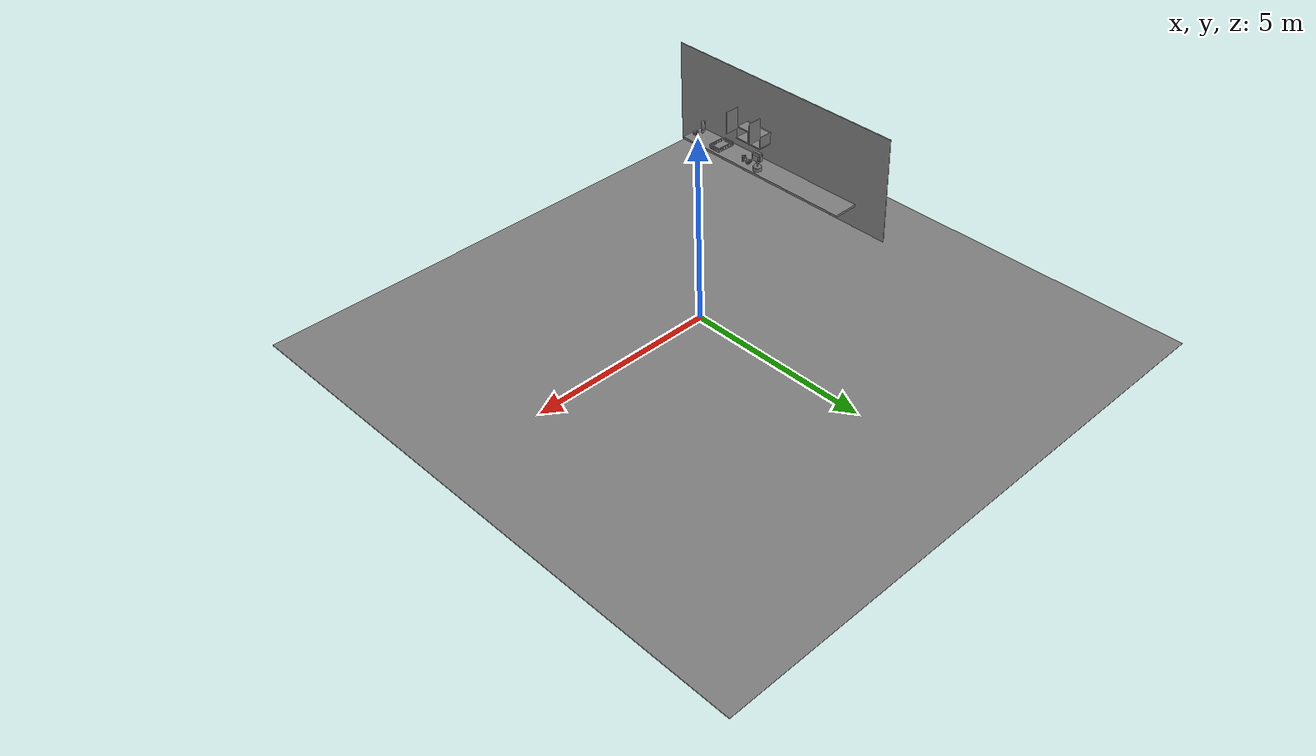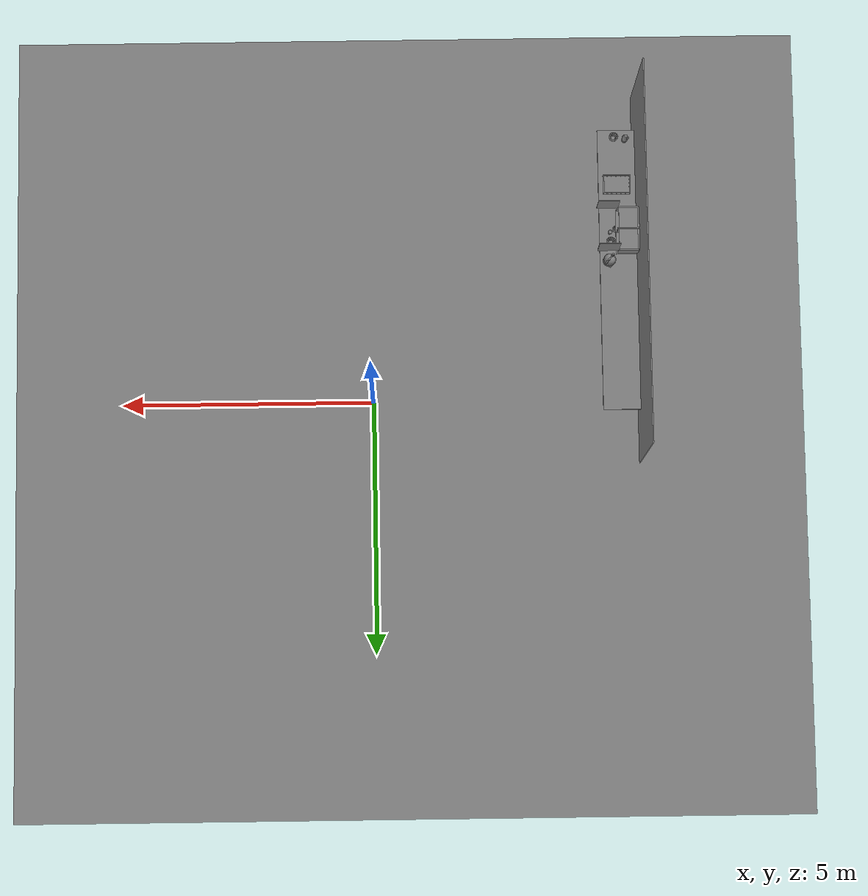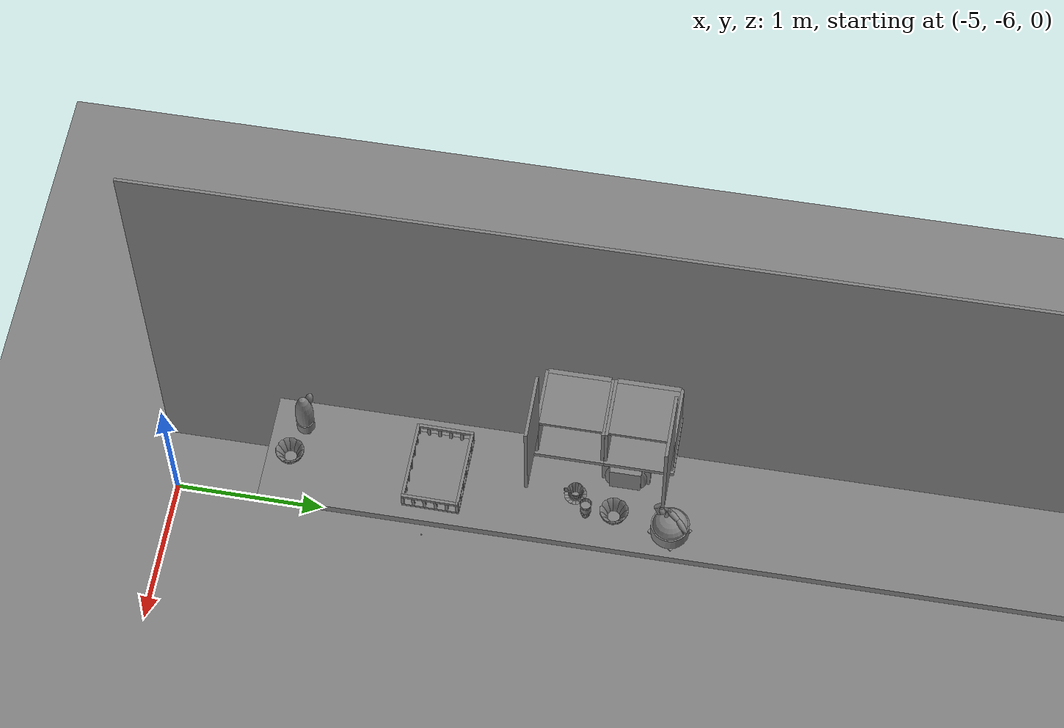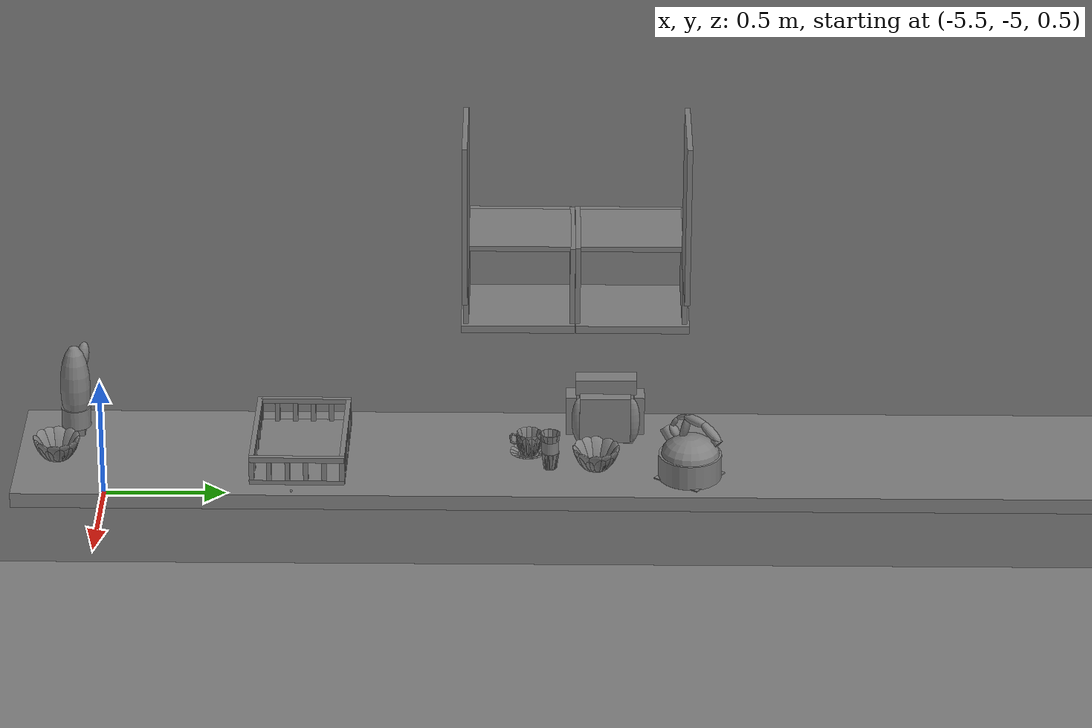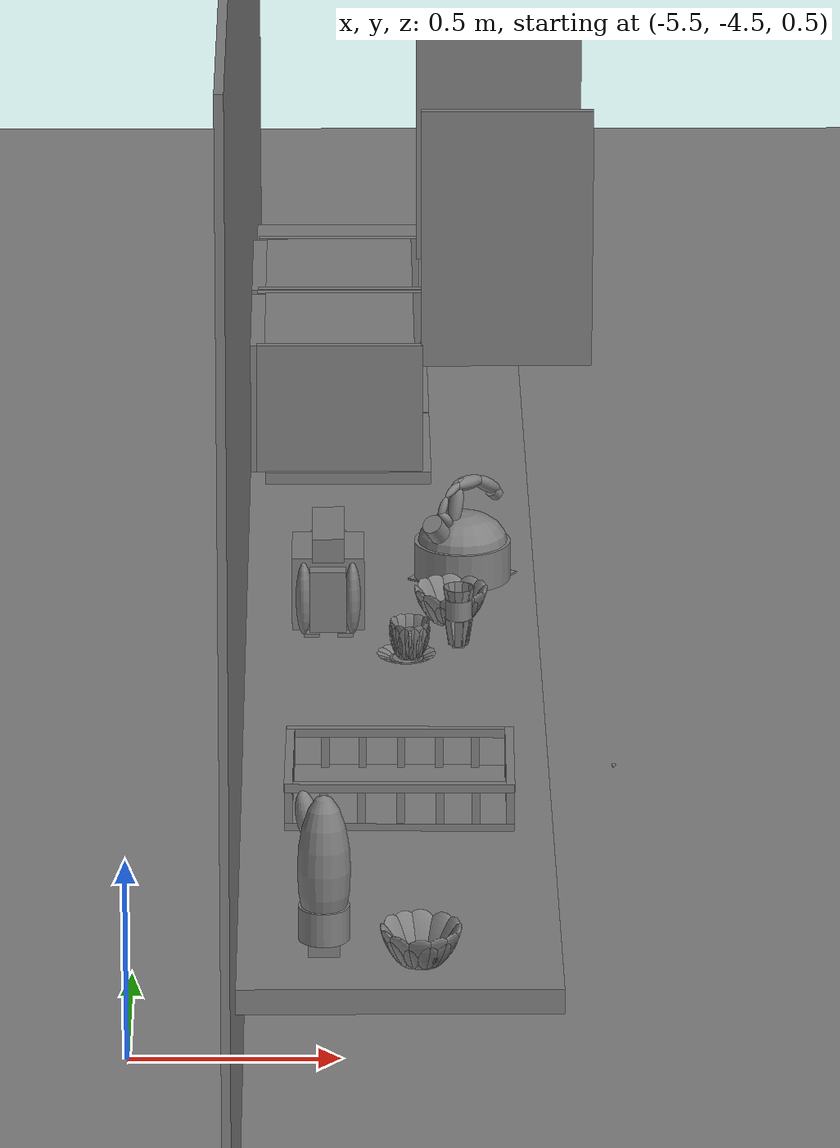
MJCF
<mujoco>
    <option gravity="0.000000000 0.000000000 -9.810000420" timestep="0.0049999999" integrator="implicitfast" density="9.8000002" viscosity="1.8000001e-05" noslip_iterations="10" iterations="100" sdf_iterations="50">
        <flag multiccd="disable"/>
    </option>
    <size memory="1000M"/>
    <compiler coordinate="local"/>
    <worldbody>
        <light cutoff="30" pos="0 1 1" dir="0 -1 -2"/>
        <light cutoff="30" pos="0 -1 1" dir="0 1 -2"/>
        <body pos="-4.860558510 -4.149443150 1.004824519" euler="0.000000000 0.000000000 -90.691108704" name="openloong_gripper_2f85_fix_base_usda_Basket_Kitchen_01">
            <geom contype="1" conaffinity="1" density="1000" type="box" material="" rgba="0.500000000 0.500000000 0.500000000 1.000000000" solimp="0.899999976 0.949999988 0.001000000" friction="1.000000000 0.005000000 0.000100000" solref="0.020000000 1.000000000" margin="0" condim="3" group="0" pos="-0.175679564 -0.000001431 0.109079957" quat="0.707107008 0.000000000 0.000000000 0.707106411" size="0.268999994 0.010000000 0.010500000" name="openloong_gripper_2f85_fix_base_usda_geom_11E1E4DE_5C65_4BB0_B451_AF2C1FFC7CC0"/>
            <geom contype="1" conaffinity="1" density="1000" type="box" material="" rgba="0.500000000 0.500000000 0.500000000 1.000000000" solimp="0.899999976 0.949999988 0.001000000" friction="1.000000000 0.005000000 0.000100000" solref="0.020000000 1.000000000" margin="0" condim="3" group="0" pos="-0.176020086 0.002992153 0.059861541" quat="0.707107008 0.000000000 0.000000000 0.707106411" size="0.009500000 0.009500000 0.039999999" name="openloong_gripper_2f85_fix_base_usda_geom_74D616A6_E5E3_4111_982B_DEE97B54683B"/>
            <geom contype="1" conaffinity="1" density="1000" type="box" material="" rgba="0.500000000 0.500000000 0.500000000 1.000000000" solimp="0.899999976 0.949999988 0.001000000" friction="1.000000000 0.005000000 0.000100000" solref="0.020000000 1.000000000" margin="0" condim="3" group="0" pos="0.176000595 0.002991199 0.059860706" quat="0.707107008 0.000000000 0.000000000 0.707106411" size="0.009500000 0.009500000 0.039999999" name="openloong_gripper_2f85_fix_base_usda_geom_C2A6F621_3F1C_4BDD_94EC_25E2CA155ADC"/>
            <geom contype="1" conaffinity="1" density="1000" type="box" material="" rgba="0.500000000 0.500000000 0.500000000 1.000000000" solimp="0.899999976 0.949999988 0.001000000" friction="1.000000000 0.005000000 0.000100000" solref="0.020000000 1.000000000" margin="0" condim="3" group="0" pos="0.176003456 0.259475708 0.059860110" quat="0.707107008 0.000000000 0.000000000 0.707106411" size="0.009500000 0.009500000 0.039999999" name="openloong_gripper_2f85_fix_base_usda_geom_443757E9_BECA_4448_A963_9E264D17B253"/>
            <geom contype="1" conaffinity="1" density="1000" type="box" material="" rgba="0.500000000 0.500000000 0.500000000 1.000000000" solimp="0.899999976 0.949999988 0.001000000" friction="1.000000000 0.005000000 0.000100000" solref="0.020000000 1.000000000" margin="0" condim="3" group="0" pos="-0.176020026 -0.088695526 0.059861422" quat="0.707107008 0.000000000 0.000000000 0.707106411" size="0.009500000 0.009500000 0.039999999" name="openloong_gripper_2f85_fix_base_usda_geom_1EB55D93_C4B9_4C28_8D0E_C2C97A57A4DE"/>
            <geom contype="1" conaffinity="1" density="1000" type="box" material="" rgba="0.500000000 0.500000000 0.500000000 1.000000000" solimp="0.899999976 0.949999988 0.001000000" friction="1.000000000 0.005000000 0.000100000" solref="0.020000000 1.000000000" margin="0" condim="3" group="0" pos="0.000000119 0.259647846 0.109080195" quat="0.707107008 0.000000000 0.000000000 0.707106411" size="0.010000000 0.185000002 0.010500000" name="openloong_gripper_2f85_fix_base_usda_geom_8CB17825_DFF2_4A71_9DAD_C5F71E9E55BF"/>
            <geom contype="1" conaffinity="1" density="1000" type="box" material="" rgba="0.500000000 0.500000000 0.500000000 1.000000000" solimp="0.899999976 0.949999988 0.001000000" friction="1.000000000 0.005000000 0.000100000" solref="0.020000000 1.000000000" margin="0" condim="3" group="0" pos="0.176002026 -0.259545326 0.059860349" quat="0.707107008 0.000000000 0.000000000 0.707106411" size="0.009500000 0.009500000 0.039999999" name="openloong_gripper_2f85_fix_base_usda_geom_95C1999D_C4F9_4079_BE68_3C33A36A8EC2"/>
            <geom contype="1" conaffinity="1" density="1000" type="box" material="" rgba="0.500000000 0.500000000 0.500000000 1.000000000" solimp="0.899999976 0.949999988 0.001000000" friction="1.000000000 0.005000000 0.000100000" solref="0.020000000 1.000000000" margin="0" condim="3" group="0" pos="0.036305428 -0.259545326 0.059860706" quat="0.707107008 0.000000000 0.000000000 0.707106411" size="0.009500000 0.009500000 0.039999999" name="openloong_gripper_2f85_fix_base_usda_geom_8A883AC5_C348_4BC1_A317_E91E31C5C953"/>
            <geom contype="1" conaffinity="1" density="1000" type="box" material="" rgba="0.500000000 0.500000000 0.500000000 1.000000000" solimp="0.899999976 0.949999988 0.001000000" friction="1.000000000 0.005000000 0.000100000" solref="0.020000000 1.000000000" margin="0" condim="3" group="0" pos="0.000000000 -0.259647369 0.109080195" quat="0.707107008 0.000000000 0.000000000 0.707106411" size="0.010000000 0.185000002 0.010500000" name="openloong_gripper_2f85_fix_base_usda_geom_3A838734_0354_4E48_ADD7_739311A96BFF"/>
            <geom contype="1" conaffinity="1" density="1000" type="box" material="" rgba="0.500000000 0.500000000 0.500000000 1.000000000" solimp="0.899999976 0.949999988 0.001000000" friction="1.000000000 0.005000000 0.000100000" solref="0.020000000 1.000000000" margin="0" condim="3" group="0" pos="-0.034950733 -0.259545803 0.059860826" quat="0.707107008 0.000000000 0.000000000 0.707106411" size="0.009500000 0.009500000 0.039999999" name="openloong_gripper_2f85_fix_base_usda_geom_CCFC4CCB_87FF_41C1_9B49_37DEF5B59F62"/>
            <geom contype="1" conaffinity="1" density="1000" type="box" material="" rgba="0.500000000 0.500000000 0.500000000 1.000000000" solimp="0.899999976 0.949999988 0.001000000" friction="1.000000000 0.005000000 0.000100000" solref="0.020000000 1.000000000" margin="0" condim="3" group="0" pos="0.108178139 0.259475946 0.059860229" quat="0.707107008 0.000000000 0.000000000 0.707106411" size="0.009500000 0.009500000 0.039999999" name="openloong_gripper_2f85_fix_base_usda_geom_ECA475C9_25FD_447F_8C71_854C1D28EA03"/>
            <geom contype="1" conaffinity="1" density="1000" type="box" material="" rgba="0.500000000 0.500000000 0.500000000 1.000000000" solimp="0.899999976 0.949999988 0.001000000" friction="1.000000000 0.005000000 0.000100000" solref="0.020000000 1.000000000" margin="0" condim="3" group="0" pos="-0.106845737 0.259475231 0.059860826" quat="0.707107008 0.000000000 0.000000000 0.707106411" size="0.009500000 0.009500000 0.039999999" name="openloong_gripper_2f85_fix_base_usda_geom_115B8E35_D555_4B3C_9B6F_8F1AD203B394"/>
            <geom contype="1" conaffinity="1" density="1000" type="box" material="" rgba="0.500000000 0.500000000 0.500000000 1.000000000" solimp="0.899999976 0.949999988 0.001000000" friction="1.000000000 0.005000000 0.000100000" solref="0.020000000 1.000000000" margin="0" condim="3" group="0" pos="-0.176020563 0.179506302 0.059861779" quat="0.707107008 0.000000000 0.000000000 0.707106411" size="0.009500000 0.009500000 0.039999999" name="openloong_gripper_2f85_fix_base_usda_geom_C99FF1FB_8E2B_46CB_BF18_EA9780DB3ACF"/>
            <geom contype="1" conaffinity="1" density="1000" type="box" material="" rgba="0.500000000 0.500000000 0.500000000 1.000000000" solimp="0.899999976 0.949999988 0.001000000" friction="1.000000000 0.005000000 0.000100000" solref="0.020000000 1.000000000" margin="0" condim="3" group="0" pos="-0.034949183 0.259475946 0.059860587" quat="0.707107008 0.000000000 0.000000000 0.707106411" size="0.009500000 0.009500000 0.039999999" name="openloong_gripper_2f85_fix_base_usda_geom_B8FA1D19_974C_47D5_90B2_4F5D16962D00"/>
            <geom contype="1" conaffinity="1" density="1000" type="box" material="" rgba="0.500000000 0.500000000 0.500000000 1.000000000" solimp="0.899999976 0.949999988 0.001000000" friction="1.000000000 0.005000000 0.000100000" solref="0.020000000 1.000000000" margin="0" condim="3" group="0" pos="0.175792217 -0.000001907 0.109079838" quat="0.707107008 0.000000000 0.000000000 0.707106411" size="0.268999994 0.010000000 0.010500000" name="openloong_gripper_2f85_fix_base_usda_geom_BFCE262E_3757_4972_BA24_E0B560B13C83"/>
            <geom contype="1" conaffinity="1" density="1000" type="box" material="" rgba="0.500000000 0.500000000 0.500000000 1.000000000" solimp="0.899999976 0.949999988 0.001000000" friction="1.000000000 0.005000000 0.000100000" solref="0.020000000 1.000000000" margin="0" condim="3" group="0" pos="-0.000015259 0.000000000 0.010668159" quat="0.707107008 0.000000000 0.000000000 0.707106411" size="0.268999994 0.186000004 0.010500000" name="openloong_gripper_2f85_fix_base_usda_geom_DACA2B1C_026D_40B3_91E6_77155FBBD288"/>
            <geom contype="1" conaffinity="1" density="1000" type="box" material="" rgba="0.500000000 0.500000000 0.500000000 1.000000000" solimp="0.899999976 0.949999988 0.001000000" friction="1.000000000 0.005000000 0.000100000" solref="0.020000000 1.000000000" margin="0" condim="3" group="0" pos="-0.176020086 0.094225407 0.059861660" quat="0.707107008 0.000000000 0.000000000 0.707106411" size="0.009500000 0.009500000 0.039999999" name="openloong_gripper_2f85_fix_base_usda_geom_972E2913_CF82_40C9_B3AE_6EA48590EEC9"/>
            <geom contype="1" conaffinity="1" density="1000" type="box" material="" rgba="0.500000000 0.500000000 0.500000000 1.000000000" solimp="0.899999976 0.949999988 0.001000000" friction="1.000000000 0.005000000 0.000100000" solref="0.020000000 1.000000000" margin="0" condim="3" group="0" pos="0.108177185 -0.259544849 0.059860468" quat="0.707107008 0.000000000 0.000000000 0.707106411" size="0.009500000 0.009500000 0.039999999" name="openloong_gripper_2f85_fix_base_usda_geom_9A19D3AD_EC63_4D1E_8AB9_2705B4FFFC47"/>
            <geom contype="1" conaffinity="1" density="1000" type="box" material="" rgba="0.500000000 0.500000000 0.500000000 1.000000000" solimp="0.899999976 0.949999988 0.001000000" friction="1.000000000 0.005000000 0.000100000" solref="0.020000000 1.000000000" margin="0" condim="3" group="0" pos="-0.176019967 -0.177031994 0.059861302" quat="0.707107008 0.000000000 0.000000000 0.707106411" size="0.009500000 0.009500000 0.039999999" name="openloong_gripper_2f85_fix_base_usda_geom_FC966469_4556_4D2B_9F82_8A58D1730C84"/>
            <geom contype="1" conaffinity="1" density="1000" type="box" material="" rgba="0.500000000 0.500000000 0.500000000 1.000000000" solimp="0.899999976 0.949999988 0.001000000" friction="1.000000000 0.005000000 0.000100000" solref="0.020000000 1.000000000" margin="0" condim="3" group="0" pos="-0.176020026 -0.259545326 0.059861183" quat="0.707107008 0.000000000 0.000000000 0.707106411" size="0.009500000 0.009500000 0.039999999" name="openloong_gripper_2f85_fix_base_usda_geom_76EFCC0E_3D10_482B_8122_3BFA4B0A9BD6"/>
            <geom contype="1" conaffinity="1" density="1000" type="box" material="" rgba="0.500000000 0.500000000 0.500000000 1.000000000" solimp="0.899999976 0.949999988 0.001000000" friction="1.000000000 0.005000000 0.000100000" solref="0.020000000 1.000000000" margin="0" condim="3" group="0" pos="-0.106846333 -0.259546280 0.059861064" quat="0.707107008 0.000000000 0.000000000 0.707106411" size="0.009500000 0.009500000 0.039999999" name="openloong_gripper_2f85_fix_base_usda_geom_CD54618A_FCAD_4C6F_8CD7_838A5D599A94"/>
            <geom contype="1" conaffinity="1" density="1000" type="box" material="" rgba="0.500000000 0.500000000 0.500000000 1.000000000" solimp="0.899999976 0.949999988 0.001000000" friction="1.000000000 0.005000000 0.000100000" solref="0.020000000 1.000000000" margin="0" condim="3" group="0" pos="0.176000595 0.094224453 0.059860826" quat="0.707107008 0.000000000 0.000000000 0.707106411" size="0.009500000 0.009500000 0.039999999" name="openloong_gripper_2f85_fix_base_usda_geom_4BC9EAB2_21FE_42BA_821B_7194362AD8B9"/>
            <geom contype="1" conaffinity="1" density="1000" type="box" material="" rgba="0.500000000 0.500000000 0.500000000 1.000000000" solimp="0.899999976 0.949999988 0.001000000" friction="1.000000000 0.005000000 0.000100000" solref="0.020000000 1.000000000" margin="0" condim="3" group="0" pos="0.176001072 -0.088696480 0.059860587" quat="0.707107008 0.000000000 0.000000000 0.707106411" size="0.009500000 0.009500000 0.039999999" name="openloong_gripper_2f85_fix_base_usda_geom_AFADDD26_7BD8_4E1A_822D_BF8178069F89"/>
            <geom contype="1" conaffinity="1" density="1000" type="box" material="" rgba="0.500000000 0.500000000 0.500000000 1.000000000" solimp="0.899999976 0.949999988 0.001000000" friction="1.000000000 0.005000000 0.000100000" solref="0.020000000 1.000000000" margin="0" condim="3" group="0" pos="0.036307096 0.259476185 0.059860468" quat="0.707107008 0.000000000 0.000000000 0.707106411" size="0.009500000 0.009500000 0.039999999" name="openloong_gripper_2f85_fix_base_usda_geom_37B45851_E6D1_48B8_8370_C1DE6B22CF19"/>
            <geom contype="1" conaffinity="1" density="1000" type="box" material="" rgba="0.500000000 0.500000000 0.500000000 1.000000000" solimp="0.899999976 0.949999988 0.001000000" friction="1.000000000 0.005000000 0.000100000" solref="0.020000000 1.000000000" margin="0" condim="3" group="0" pos="0.176001549 -0.177031994 0.059860468" quat="0.707107008 0.000000000 0.000000000 0.707106411" size="0.009500000 0.009500000 0.039999999" name="openloong_gripper_2f85_fix_base_usda_geom_B1023651_3695_42A1_8D20_62505D9B53CE"/>
            <geom contype="1" conaffinity="1" density="1000" type="box" material="" rgba="0.500000000 0.500000000 0.500000000 1.000000000" solimp="0.899999976 0.949999988 0.001000000" friction="1.000000000 0.005000000 0.000100000" solref="0.020000000 1.000000000" margin="0" condim="3" group="0" pos="0.176000118 0.179505348 0.059860945" quat="0.707107008 0.000000000 0.000000000 0.707106411" size="0.009500000 0.009500000 0.039999999" name="openloong_gripper_2f85_fix_base_usda_geom_70C4A298_C9D5_40A6_A0BD_05941A1C2CA9"/>
            <geom contype="1" conaffinity="1" density="1000" type="box" material="" rgba="0.500000000 0.500000000 0.500000000 1.000000000" solimp="0.899999976 0.949999988 0.001000000" friction="1.000000000 0.005000000 0.000100000" solref="0.020000000 1.000000000" margin="0" condim="3" group="0" pos="-0.176020086 0.259474993 0.059860945" quat="0.707107008 0.000000000 0.000000000 0.707106411" size="0.009500000 0.009500000 0.039999999" name="openloong_gripper_2f85_fix_base_usda_geom_99FC2439_8B4E_4999_B16C_0379F45A8B44"/>
            <freejoint name="openloong_gripper_2f85_fix_base_usda_Basket_Kitchen_01_joint"/>
        </body>
        <body pos="-4.802892208 -3.488179445 1.876015186" euler="89.999992371 -89.999946594 0.000000000" name="Interactive Objcets_guimen_01">
            <geom contype="1" conaffinity="1" density="1000" type="box" material="" rgba="0.500000000 0.500000000 0.500000000 1.000000000" solimp="0.899999976 0.949999988 0.001000000" friction="1.000000000 0.005000000 0.000100000" solref="0.020000000 1.000000000" margin="0" condim="3" group="0" pos="0.006727934 0.314709902 -0.203009605" quat="1.000000000 0.000000119 -0.000000119 0.000000000" size="0.010000000 0.317999989 0.204999998" name="Interactive Objcets_geom_4AB08E48_DC8E_4DF4_BE25_609A6B7392A1"/>
            <joint armature="0" stiffness="0" damping="1" axis="0.000000 1.000000 0.000000" type="hinge" name="Interactive Objcets_guimen_01"/>
        </body>
        <body pos="-4.805274963 -2.665403366 1.876015186" euler="89.999877930 89.999969482 0.000000000" name="Interactive Objcets_guimen_02">
            <geom contype="1" conaffinity="1" density="1000" type="box" material="" rgba="0.500000000 0.500000000 0.500000000 1.000000000" solimp="0.899999976 0.949999988 0.001000000" friction="1.000000000 0.005000000 0.000100000" solref="0.020000000 1.000000000" margin="0" condim="3" group="0" pos="0.006727815 0.314709663 0.203009367" quat="0.999999940 0.000000000 0.000000000 0.000000000" size="0.010000000 0.317999989 0.204999998" name="Interactive Objcets_geom_13765E21_49A5_41E0_B1A6_0EEEFC46D876"/>
            <joint armature="0" stiffness="0" damping="1" axis="0.000000 1.000000 0.000000" type="hinge" name="Interactive Objcets_guimen_02"/>
        </body>
        <body pos="-4.827295780 -3.287638187 1.074643731" euler="0.000000000 0.000000000 89.999992371" name="Interactive Objcets_coffeecup_01">
            <geom contype="1" conaffinity="1" density="1000" type="ellipsoid" material="" rgba="0.500000000 0.500000000 0.500000000 1.000000000" solimp="0.899999976 0.949999988 0.001000000" friction="1.000000000 0.005000000 0.000100000" solref="0.020000000 1.000000000" margin="0" condim="3" group="0" pos="0.035336256 0.000558376 -0.043215394" quat="0.999999881 0.000000000 0.000000000 0.000000000" size="0.029999999 0.029999999 0.001000000" name="Interactive Objcets_geom_94040FC7_2925_4C1A_881D_B3E2AB7B5CF1"/>
            <geom contype="1" conaffinity="1" density="1000" type="ellipsoid" material="" rgba="0.500000000 0.500000000 0.500000000 1.000000000" solimp="0.899999976 0.949999988 0.001000000" friction="1.000000000 0.005000000 0.000100000" solref="0.020000000 1.000000000" margin="0" condim="3" group="0" pos="0.067416430 -0.018191338 0.002976775" quat="0.961934388 0.024418317 0.091648072 -0.256293803" size="0.005000000 0.029999999 0.048999999" name="Interactive Objcets_geom_2DA4E45B_6007_4005_937A_FE9E29C99F0B"/>
            <geom contype="1" conaffinity="1" density="1000" type="ellipsoid" material="" rgba="0.500000000 0.500000000 0.500000000 1.000000000" solimp="0.899999976 0.949999988 0.001000000" friction="1.000000000 0.005000000 0.000100000" solref="0.020000000 1.000000000" margin="0" condim="3" group="0" pos="0.034471050 -0.037125111 0.002976775" quat="0.701517045 0.067293778 0.066836871 -0.706313014" size="0.005000000 0.029999999 0.048999999" name="Interactive Objcets_geom_73C7CE14_3659_474D_9FED_C4C1ACCAA38F"/>
            <geom contype="1" conaffinity="1" density="1000" type="ellipsoid" material="" rgba="0.500000000 0.500000000 0.500000000 1.000000000" solimp="0.899999976 0.949999988 0.001000000" friction="1.000000000 0.005000000 0.000100000" solref="0.020000000 1.000000000" margin="0" condim="3" group="0" pos="0.035336256 0.000558376 -0.045152068" quat="0.999999881 0.000000000 0.000000000 0.000000000" size="0.029999999 0.029999999 0.001000000" name="Interactive Objcets_geom_086BF10D_9584_4C16_866E_C05B641EF02A"/>
            <geom contype="1" conaffinity="1" density="1000" type="ellipsoid" material="" rgba="0.500000000 0.500000000 0.500000000 1.000000000" solimp="0.899999976 0.949999988 0.001000000" friction="1.000000000 0.005000000 0.000100000" solref="0.020000000 1.000000000" margin="0" condim="3" group="0" pos="0.001010895 -0.016271591 0.002976775" quat="0.228377163 0.092315644 0.021758538 -0.968941689" size="0.005000000 0.029999999 0.048999999" name="Interactive Objcets_geom_6D196601_3524_46AB_9963_68F19C68627E"/>
            <geom contype="1" conaffinity="1" density="1000" type="capsule" material="" rgba="0.500000000 0.500000000 0.500000000 1.000000000" solimp="0.899999976 0.949999988 0.001000000" friction="1.000000000 0.005000000 0.000100000" solref="0.020000000 1.000000000" margin="0" condim="3" group="0" pos="-0.021276474 0.000000000 0.038509369" quat="0.633189917 0.000000000 0.773996413 0.000000000" size="0.004000000 0.009000000 1.000000000" name="Interactive Objcets_geom_41C6CA7D_3D16_457E_AAE4_A0A5DD531624"/>
            <geom contype="1" conaffinity="1" density="1000" type="capsule" material="" rgba="0.500000000 0.500000000 0.500000000 1.000000000" solimp="0.899999976 0.949999988 0.001000000" friction="1.000000000 0.005000000 0.000100000" solref="0.020000000 1.000000000" margin="0" condim="3" group="0" pos="-0.018014431 0.000000000 0.001762271" quat="0.707106769 -0.000000004 0.707106709 -0.000000088" size="0.004000000 0.005000000 1.000000000" name="Interactive Objcets_geom_8C086900_342D_4473_8FB0_5900068A2F55"/>
            <geom contype="1" conaffinity="1" density="1000" type="ellipsoid" material="" rgba="0.500000000 0.500000000 0.500000000 1.000000000" solimp="0.899999976 0.949999988 0.001000000" friction="1.000000000 0.005000000 0.000100000" solref="0.020000000 1.000000000" margin="0" condim="3" group="0" pos="0.068445444 0.017385960 0.002976775" quat="0.228377223 -0.092319682 -0.021759447 -0.968941331" size="0.005000000 0.029999999 0.048999999" name="Interactive Objcets_geom_16B33345_3784_4C04_BA97_BD8A0AAC2661"/>
            <geom contype="1" conaffinity="1" density="1000" type="ellipsoid" material="" rgba="0.500000000 0.500000000 0.500000000 1.000000000" solimp="0.899999976 0.949999988 0.001000000" friction="1.000000000 0.005000000 0.000100000" solref="0.020000000 1.000000000" margin="0" condim="3" group="0" pos="0.002039194 0.019308567 0.002976775" quat="0.961933970 -0.024419386 -0.091652036 -0.256293654" size="0.005000000 0.029999999 0.048999999" name="Interactive Objcets_geom_230C935B_CF5F_4900_AAB8_9F22B832DA6F"/>
            <geom contype="1" conaffinity="1" density="1000" type="ellipsoid" material="" rgba="0.500000000 0.500000000 0.500000000 1.000000000" solimp="0.899999976 0.949999988 0.001000000" friction="1.000000000 0.005000000 0.000100000" solref="0.020000000 1.000000000" margin="0" condim="3" group="0" pos="0.034984604 0.038240910 0.002976775" quat="0.701516926 -0.067296736 -0.066839755 -0.706312656" size="0.005000000 0.029999999 0.048999999" name="Interactive Objcets_geom_2E8D19BF_B5E1_4D24_9BF2_3F9CC9DE2F8B"/>
            <geom contype="1" conaffinity="1" density="1000" type="ellipsoid" material="" rgba="0.500000000 0.500000000 0.500000000 1.000000000" solimp="0.899999976 0.949999988 0.001000000" friction="1.000000000 0.005000000 0.000100000" solref="0.020000000 1.000000000" margin="0" condim="3" group="0" pos="0.017669693 0.034160614 0.002976775" quat="0.848410904 -0.049618516 -0.080835648 -0.520770907" size="0.005000000 0.029999999 0.048999999" name="Interactive Objcets_geom_5D09AA33_FA46_4506_AD02_871C80015CF0"/>
            <geom contype="1" conaffinity="1" density="1000" type="ellipsoid" material="" rgba="0.500000000 0.500000000 0.500000000 1.000000000" solimp="0.899999976 0.949999988 0.001000000" friction="1.000000000 0.005000000 0.000100000" solref="0.020000000 1.000000000" margin="0" condim="3" group="0" pos="-0.002956629 0.000558376 0.002976775" quat="0.995491505 0.000000004 -0.094849378 -0.000000089" size="0.005000000 0.029999999 0.048999999" name="Interactive Objcets_geom_D21376FD_D4B1_4CBC_9F9B_8CC758C8E1FF"/>
            <geom contype="1" conaffinity="1" density="1000" type="ellipsoid" material="" rgba="0.500000000 0.500000000 0.500000000 1.000000000" solimp="0.899999976 0.949999988 0.001000000" friction="1.000000000 0.005000000 0.000100000" solref="0.020000000 1.000000000" margin="0" condim="3" group="0" pos="0.051787138 -0.033043861 0.002976775" quat="0.848411202 0.049616337 0.080832161 -0.520771146" size="0.005000000 0.029999999 0.048999999" name="Interactive Objcets_geom_8F9AB4D2_8F5D_4C58_AAA9_013BB70101BC"/>
            <geom contype="1" conaffinity="1" density="1000" type="capsule" material="" rgba="0.500000000 0.500000000 0.500000000 1.000000000" solimp="0.899999976 0.949999988 0.001000000" friction="1.000000000 0.005000000 0.000100000" solref="0.020000000 1.000000000" margin="0" condim="3" group="0" pos="-0.030251026 0.000000000 0.004966617" quat="0.480583906 -0.000000000 0.876948774 -0.000000126" size="0.004000000 0.005000000 1.000000000" name="Interactive Objcets_geom_867B97B4_8651_436E_B207_891ADA77A810"/>
            <geom contype="1" conaffinity="1" density="1000" type="capsule" material="" rgba="0.500000000 0.500000000 0.500000000 1.000000000" solimp="0.899999976 0.949999988 0.001000000" friction="1.000000000 0.005000000 0.000100000" solref="0.020000000 1.000000000" margin="0" condim="3" group="0" pos="-0.036300898 0.000000000 0.021037936" quat="0.044551343 -0.000000000 0.999007046 -0.000000126" size="0.004000000 0.012000000 1.000000000" name="Interactive Objcets_geom_78F6448B_5A8B_4EFB_990B_DDB5D6FDECB2"/>
            <geom contype="1" conaffinity="1" density="1000" type="capsule" material="" rgba="0.500000000 0.500000000 0.500000000 1.000000000" solimp="0.899999976 0.949999988 0.001000000" friction="1.000000000 0.005000000 0.000100000" solref="0.020000000 1.000000000" margin="0" condim="3" group="0" pos="-0.008219719 0.000000000 -0.000944734" quat="0.364379913 0.000000063 0.931250274 -0.000000063" size="0.004000000 0.003000000 1.000000000" name="Interactive Objcets_geom_F84C4708_272F_46D7_8014_898C82AE1F29"/>
            <geom contype="1" conaffinity="1" density="1000" type="capsule" material="" rgba="0.500000000 0.500000000 0.500000000 1.000000000" solimp="0.899999976 0.949999988 0.001000000" friction="1.000000000 0.005000000 0.000100000" solref="0.020000000 1.000000000" margin="0" condim="3" group="0" pos="-0.033022881 0.000000000 0.037873149" quat="0.874267220 0.000000042 0.485444903 -0.000000084" size="0.004000000 0.004000000 1.000000000" name="Interactive Objcets_geom_CFD0E8F0_0C2C_4414_8D85_5FFCABAAE772"/>
            <geom contype="1" conaffinity="1" density="1000" type="ellipsoid" material="" rgba="0.500000000 0.500000000 0.500000000 1.000000000" solimp="0.899999976 0.949999988 0.001000000" friction="1.000000000 0.005000000 0.000100000" solref="0.020000000 1.000000000" margin="0" condim="3" group="0" pos="0.015755907 -0.032001972 0.002976775" quat="0.496025920 0.082232773 0.047258731 -0.863112032" size="0.005000000 0.029999999 0.048999999" name="Interactive Objcets_geom_91B8315E_EEF2_4D7E_9881_19A555C3BE82"/>
            <geom contype="1" conaffinity="1" density="1000" type="ellipsoid" material="" rgba="0.500000000 0.500000000 0.500000000 1.000000000" solimp="0.899999976 0.949999988 0.001000000" friction="1.000000000 0.005000000 0.000100000" solref="0.020000000 1.000000000" margin="0" condim="3" group="0" pos="0.072411790 0.000558376 0.002976775" quat="0.995491922 -0.000000019 0.094845265 -0.000000089" size="0.005000000 0.029999999 0.048999999" name="Interactive Objcets_geom_0268B7A2_1328_4A13_90BF_B97CE51B9ADE"/>
            <geom contype="1" conaffinity="1" density="1000" type="ellipsoid" material="" rgba="0.500000000 0.500000000 0.500000000 1.000000000" solimp="0.899999976 0.949999988 0.001000000" friction="1.000000000 0.005000000 0.000100000" solref="0.020000000 1.000000000" margin="0" condim="3" group="0" pos="0.053700209 0.033117294 0.002976775" quat="0.496025741 -0.082236379 -0.047260769 -0.863111615" size="0.005000000 0.029999999 0.048999999" name="Interactive Objcets_geom_138CBF9F_17B1_4CCE_88DF_6EBABBB399C6"/>
            <freejoint name="Interactive Objcets_coffeecup_01"/>
        </body>
        <body pos="-5.020127296 -2.953741550 1.135127425" euler="89.999946594 0.000000000 0.000000000" name="Interactive Objcets_Bread">
            <geom contype="1" conaffinity="1" density="1000" type="box" material="" rgba="0.500000000 0.500000000 0.500000000 1.000000000" solimp="0.899999976 0.949999988 0.001000000" friction="1.000000000 0.005000000 0.000100000" solref="0.020000000 1.000000000" margin="0" condim="3" group="0" pos="-0.008702755 -0.017670274 -0.135069147" quat="0.707107067 -0.707106471 0.000000021 -0.000000021" size="0.045000002 0.020000000 0.079999998" name="Interactive Objcets_geom_0FBD3284_1C06_4B56_809A_8C89C061FF29"/>
            <geom contype="1" conaffinity="1" density="1000" type="box" material="" rgba="0.500000000 0.500000000 0.500000000 1.000000000" solimp="0.899999976 0.949999988 0.001000000" friction="1.000000000 0.005000000 0.000100000" solref="0.020000000 1.000000000" margin="0" condim="3" group="0" pos="0.033925056 -0.123201847 0.086778767" quat="0.707107067 -0.707106471 0.000000021 -0.000000021" size="0.020000000 0.020000000 0.005000000" name="Interactive Objcets_geom_559A6B2E_5ECA_4762_9BA7_8DCFB2410B21"/>
            <geom contype="1" conaffinity="1" density="1000" type="box" material="" rgba="0.500000000 0.500000000 0.500000000 1.000000000" solimp="0.899999976 0.949999988 0.001000000" friction="1.000000000 0.005000000 0.000100000" solref="0.020000000 1.000000000" margin="0" condim="3" group="0" pos="-0.008702755 -0.016588926 0.000174277" quat="0.707107067 -0.707106471 0.000000021 -0.000000021" size="0.090000004 0.100000001 0.094999999" name="Interactive Objcets_geom_0CA53B85_227D_42F5_8B3A_200293DFD152"/>
            <geom contype="1" conaffinity="1" density="1000" type="ellipsoid" material="" rgba="0.500000000 0.500000000 0.500000000 1.000000000" solimp="0.899999976 0.949999988 0.001000000" friction="1.000000000 0.005000000 0.000100000" solref="0.020000000 1.000000000" margin="0" condim="3" group="0" pos="-0.067312241 -0.026057482 -0.101716787" quat="0.707107067 -0.707106471 0.000000021 -0.000000021" size="0.020000000 0.029999999 0.094999999" name="Interactive Objcets_geom_A7664CA9_0F66_4893_8B02_63D2A748E1CA"/>
            <geom contype="1" conaffinity="1" density="1000" type="ellipsoid" material="" rgba="0.500000000 0.500000000 0.500000000 1.000000000" solimp="0.899999976 0.949999988 0.001000000" friction="1.000000000 0.005000000 0.000100000" solref="0.020000000 1.000000000" margin="0" condim="3" group="0" pos="0.052222252 -0.026057363 0.101459242" quat="0.707107067 -0.707106471 0.000000021 -0.000000021" size="0.020000000 0.029999999 0.094999999" name="Interactive Objcets_geom_D259D615_2DA7_4502_AB87_3306A240FECA"/>
            <geom contype="1" conaffinity="1" density="1000" type="box" material="" rgba="0.500000000 0.500000000 0.500000000 1.000000000" solimp="0.899999976 0.949999988 0.001000000" friction="1.000000000 0.005000000 0.000100000" solref="0.020000000 1.000000000" margin="0" condim="3" group="0" pos="-0.050020695 -0.123201847 0.086778767" quat="0.707107067 -0.707106471 0.000000021 -0.000000021" size="0.020000000 0.020000000 0.005000000" name="Interactive Objcets_geom_B36CE9C3_6177_4DDF_A070_59C425D596BD"/>
            <geom contype="1" conaffinity="1" density="1000" type="box" material="" rgba="0.500000000 0.500000000 0.500000000 1.000000000" solimp="0.899999976 0.949999988 0.001000000" friction="1.000000000 0.005000000 0.000100000" solref="0.020000000 1.000000000" margin="0" condim="3" group="0" pos="0.033925056 -0.123201728 -0.092369899" quat="0.707107067 -0.707106471 0.000000021 -0.000000021" size="0.020000000 0.020000000 0.005000000" name="Interactive Objcets_geom_A8F2DB6A_7E6D_481B_B618_FEB94A595CA4"/>
            <geom contype="1" conaffinity="1" density="1000" type="ellipsoid" material="" rgba="0.500000000 0.500000000 0.500000000 1.000000000" solimp="0.899999976 0.949999988 0.001000000" friction="1.000000000 0.005000000 0.000100000" solref="0.020000000 1.000000000" margin="0" condim="3" group="0" pos="-0.069190502 -0.026057363 0.101458766" quat="0.707107067 -0.707106471 0.000000021 -0.000000021" size="0.020000000 0.029999999 0.094999999" name="Interactive Objcets_geom_3F2063DF_E51C_4E08_8713_CBDCF89DCF8D"/>
            <geom contype="1" conaffinity="1" density="1000" type="box" material="" rgba="0.500000000 0.500000000 0.500000000 1.000000000" solimp="0.899999976 0.949999988 0.001000000" friction="1.000000000 0.005000000 0.000100000" solref="0.020000000 1.000000000" margin="0" condim="3" group="0" pos="-0.008702755 -0.017670155 0.134585604" quat="0.707107067 -0.707106471 0.000000021 -0.000000021" size="0.045000002 0.020000000 0.079999998" name="Interactive Objcets_geom_C375F53E_5841_40EA_9D90_2198DE157018"/>
            <geom contype="1" conaffinity="1" density="1000" type="box" material="" rgba="0.500000000 0.500000000 0.500000000 1.000000000" solimp="0.899999976 0.949999988 0.001000000" friction="1.000000000 0.005000000 0.000100000" solref="0.020000000 1.000000000" margin="0" condim="3" group="0" pos="-0.050020695 -0.123201728 -0.092370376" quat="0.707107067 -0.707106471 0.000000021 -0.000000021" size="0.020000000 0.020000000 0.005000000" name="Interactive Objcets_geom_EE82F850_79C6_4F0C_AD1B_E876794251FF"/>
            <geom contype="1" conaffinity="1" density="1000" type="box" material="" rgba="0.500000000 0.500000000 0.500000000 1.000000000" solimp="0.899999976 0.949999988 0.001000000" friction="1.000000000 0.005000000 0.000100000" solref="0.020000000 1.000000000" margin="0" condim="3" group="0" pos="-0.008702755 0.104617000 -0.003706597" quat="0.707107067 -0.707106471 0.000000021 -0.000000021" size="0.039999999 0.119999997 0.030999999" name="Interactive Objcets_geom_68AAD727_7F63_4BFD_A823_F8402ED2DB1E"/>
            <geom contype="1" conaffinity="1" density="1000" type="ellipsoid" material="" rgba="0.500000000 0.500000000 0.500000000 1.000000000" solimp="0.899999976 0.949999988 0.001000000" friction="1.000000000 0.005000000 0.000100000" solref="0.020000000 1.000000000" margin="0" condim="3" group="0" pos="0.052222252 -0.026057243 -0.106481344" quat="0.707107067 -0.707106471 0.000000021 -0.000000021" size="0.020000000 0.029999999 0.094999999" name="Interactive Objcets_geom_1CF839BF_0963_4721_ACD9_D905712B4788"/>
            <freejoint name="Interactive Objcets_Bread"/>
        </body>
        <body pos="-4.821335316 -5.105734825 1.007418752" euler="0.000000000 0.000000000 89.999946594" name="Interactive Objcets_bow_04">
            <geom contype="1" conaffinity="1" density="1000" type="ellipsoid" material="" rgba="0.500000000 0.500000000 0.500000000 1.000000000" solimp="0.899999976 0.949999988 0.001000000" friction="1.000000000 0.005000000 0.000100000" solref="0.020000000 1.000000000" margin="0" condim="3" group="0" pos="0.052321672 -0.040297985 0.044118762" quat="0.919264674 0.076882720 0.225593746 -0.313287675" size="0.010000000 0.039999999 0.052000001" name="Interactive Objcets_geom_2F5C3AAB_34EC_435B_8574_9DB28FAD5AF9"/>
            <geom contype="1" conaffinity="1" density="1000" type="ellipsoid" material="" rgba="0.500000000 0.500000000 0.500000000 1.000000000" solimp="0.899999976 0.949999988 0.001000000" friction="1.000000000 0.005000000 0.000100000" solref="0.020000000 1.000000000" margin="0" condim="3" group="0" pos="0.059080124 0.029511929 0.044118762" quat="0.223252952 -0.231952190 -0.054787360 -0.945174456" size="0.010000000 0.039999999 0.052000001" name="Interactive Objcets_geom_E180399B_9C5C_4ADB_84A9_2B73DB099F20"/>
            <geom contype="1" conaffinity="1" density="1000" type="ellipsoid" material="" rgba="0.500000000 0.500000000 0.500000000 1.000000000" solimp="0.899999976 0.949999988 0.001000000" friction="1.000000000 0.005000000 0.000100000" solref="0.020000000 1.000000000" margin="0" condim="3" group="0" pos="0.000082970 0.000000000 0.003118873" quat="1.000000000 0.000000000 0.000000000 0.000000000" size="0.039999999 0.039999999 0.002000000" name="Interactive Objcets_geom_A0AC44F6_02EA_43DF_BDE2_5AE8A875E7E0"/>
            <geom contype="1" conaffinity="1" density="1000" type="ellipsoid" material="" rgba="0.500000000 0.500000000 0.500000000 1.000000000" solimp="0.899999976 0.949999988 0.001000000" friction="1.000000000 0.005000000 0.000100000" solref="0.020000000 1.000000000" margin="0" condim="3" group="0" pos="-0.040080309 -0.052354813 0.044118762" quat="0.429593146 0.213749856 0.105425127 -0.871003032" size="0.010000000 0.039999999 0.052000001" name="Interactive Objcets_geom_0E9ECEFF_07C2_4817_B088_A1BAA736ABD4"/>
            <geom contype="1" conaffinity="1" density="1000" type="ellipsoid" material="" rgba="0.500000000 0.500000000 0.500000000 1.000000000" solimp="0.899999976 0.949999988 0.001000000" friction="1.000000000 0.005000000 0.000100000" solref="0.020000000 1.000000000" margin="0" condim="3" group="0" pos="0.000243664 -0.065983295 0.044118762" quat="0.687598884 0.168314576 0.168741226 -0.685860336" size="0.010000000 0.039999999 0.052000001" name="Interactive Objcets_geom_B7DC0E24_4B5C_431D_BE85_24DF05241045"/>
            <geom contype="1" conaffinity="1" density="1000" type="ellipsoid" material="" rgba="0.500000000 0.500000000 0.500000000 1.000000000" solimp="0.899999976 0.949999988 0.001000000" friction="1.000000000 0.005000000 0.000100000" solref="0.020000000 1.000000000" margin="0" condim="3" group="0" pos="-0.065898657 -0.000007629 0.044118762" quat="0.971183062 -0.000000142 -0.238334835 0.000000030" size="0.010000000 0.039999999 0.052000001" name="Interactive Objcets_geom_65351A06_04BD_4B78_8850_F0360C3AD0CD"/>
            <geom contype="1" conaffinity="1" density="1000" type="ellipsoid" material="" rgba="0.500000000 0.500000000 0.500000000 1.000000000" solimp="0.899999976 0.949999988 0.001000000" friction="1.000000000 0.005000000 0.000100000" solref="0.020000000 1.000000000" margin="0" condim="3" group="0" pos="-0.052167892 0.040281773 0.044118762" quat="0.919264615 -0.076883025 -0.225593626 -0.313287735" size="0.010000000 0.039999999 0.052000001" name="Interactive Objcets_geom_13BF8215_FF45_4485_8F82_F94FCFA225BF"/>
            <geom contype="1" conaffinity="1" density="1000" type="ellipsoid" material="" rgba="0.500000000 0.500000000 0.500000000 1.000000000" solimp="0.899999976 0.949999988 0.001000000" friction="1.000000000 0.005000000 0.000100000" solref="0.020000000 1.000000000" margin="0" condim="3" group="0" pos="-0.029293537 0.059069157 0.044118762" quat="0.825556040 -0.125530839 -0.202596709 -0.511521041" size="0.010000000 0.039999999 0.052000001" name="Interactive Objcets_geom_08FE51B3_57CE_4600_BD25_C1666B2ABCBF"/>
            <geom contype="1" conaffinity="1" density="1000" type="ellipsoid" material="" rgba="0.500000000 0.500000000 0.500000000 1.000000000" solimp="0.899999976 0.949999988 0.001000000" friction="1.000000000 0.005000000 0.000100000" solref="0.020000000 1.000000000" margin="0" condim="3" group="0" pos="0.000082970 0.000000000 0.000446677" quat="1.000000000 0.000000000 0.000000000 0.000000000" size="0.039999999 0.039999999 0.002000000" name="Interactive Objcets_geom_3F8C62CC_2768_4829_843F_0E5BF37A7DD4"/>
            <geom contype="1" conaffinity="1" density="1000" type="ellipsoid" material="" rgba="0.500000000 0.500000000 0.500000000 1.000000000" solimp="0.899999976 0.949999988 0.001000000" friction="1.000000000 0.005000000 0.000100000" solref="0.020000000 1.000000000" margin="0" condim="3" group="0" pos="0.029448032 -0.059085369 0.044118762" quat="0.825555801 0.125530601 0.202597082 -0.511521280" size="0.010000000 0.039999999 0.052000001" name="Interactive Objcets_geom_E04D10F7_E162_412A_B7CB_C38891FB2FC5"/>
            <geom contype="1" conaffinity="1" density="1000" type="ellipsoid" material="" rgba="0.500000000 0.500000000 0.500000000 1.000000000" solimp="0.899999976 0.949999988 0.001000000" friction="1.000000000 0.005000000 0.000100000" solref="0.020000000 1.000000000" margin="0" condim="3" group="0" pos="0.066051960 -0.000007629 0.044118762" quat="0.971183062 -0.000000156 0.238334835 0.000000030" size="0.010000000 0.039999999 0.052000001" name="Interactive Objcets_geom_1BCB4CD1_01D4_4FB0_AB04_D95858A081CB"/>
            <geom contype="1" conaffinity="1" density="1000" type="ellipsoid" material="" rgba="0.500000000 0.500000000 0.500000000 1.000000000" solimp="0.899999976 0.949999988 0.001000000" friction="1.000000000 0.005000000 0.000100000" solref="0.020000000 1.000000000" margin="0" condim="3" group="0" pos="-0.058925867 -0.029528618 0.044118762" quat="0.223252863 0.231952116 0.054787725 -0.945174456" size="0.010000000 0.039999999 0.052000001" name="Interactive Objcets_geom_8FD9F6C1_DEDA_4B17_8B5C_C3232D135E36"/>
            <geom contype="1" conaffinity="1" density="1000" type="ellipsoid" material="" rgba="0.500000000 0.500000000 0.500000000 1.000000000" solimp="0.899999976 0.949999988 0.001000000" friction="1.000000000 0.005000000 0.000100000" solref="0.020000000 1.000000000" margin="0" condim="3" group="0" pos="0.040234327 0.052339077 0.044118762" quat="0.429593533 -0.213750005 -0.105424747 -0.871002972" size="0.010000000 0.039999999 0.052000001" name="Interactive Objcets_geom_81CE55F7_D9C6_4234_B056_1F5C021E47C4"/>
            <geom contype="1" conaffinity="1" density="1000" type="ellipsoid" material="" rgba="0.500000000 0.500000000 0.500000000 1.000000000" solimp="0.899999976 0.949999988 0.001000000" friction="1.000000000 0.005000000 0.000100000" solref="0.020000000 1.000000000" margin="0" condim="3" group="0" pos="-0.000090122 0.065967083 0.044118762" quat="0.687598825 -0.168314755 -0.168741047 -0.685860395" size="0.010000000 0.039999999 0.052000001" name="Interactive Objcets_geom_8452CFC8_2AD7_4568_AF6F_2114B1A01320"/>
            <freejoint name="Interactive Objcets_bow_04"/>
        </body>
        <body pos="-4.685121059 -2.618872881 1.139834642" euler="-89.999885559 -75.046211243 -179.999633789" name="Interactive Objcets_shuihu">
            <geom contype="1" conaffinity="1" density="1000" type="ellipsoid" material="" rgba="0.500000000 0.500000000 0.500000000 1.000000000" solimp="0.899999976 0.949999988 0.001000000" friction="1.000000000 0.005000000 0.000100000" solref="0.020000000 1.000000000" margin="0" condim="3" group="0" pos="0.076839805 0.041928887 0.028444767" quat="0.777403057 0.260122687 0.543099582 -0.181723833" size="0.020000000 0.029999999 0.015000000" name="Interactive Objcets_geom_BBA3FB38_40B5_4118_AC82_FD62BBFE7412"/>
            <geom contype="1" conaffinity="1" density="1000" type="cylinder" material="" rgba="0.500000000 0.500000000 0.500000000 1.000000000" solimp="0.899999976 0.949999988 0.001000000" friction="1.000000000 0.005000000 0.000100000" solref="0.020000000 1.000000000" margin="0" condim="3" group="0" pos="0.006719470 -0.083229184 -0.000185013" quat="0.579664290 -0.579662681 0.404957741 0.404956520" size="0.123000003 0.050000001 1.000000000" name="Interactive Objcets_geom_2ED12912_CF68_4B72_8EC4_F59826FC0FBE"/>
            <geom contype="1" conaffinity="1" density="1000" type="cylinder" material="" rgba="0.500000000 0.500000000 0.500000000 1.000000000" solimp="0.899999976 0.949999988 0.001000000" friction="1.000000000 0.005000000 0.000100000" solref="0.020000000 1.000000000" margin="0" condim="3" group="0" pos="0.097564876 0.019223809 0.042538166" quat="0.757945418 -0.330064029 0.507527351 0.242883876" size="0.027000001 0.032499999 1.000000000" name="Interactive Objcets_geom_F69F2CA7_C1DB_4C97_8264_10A193696091"/>
            <geom contype="1" conaffinity="1" density="1000" type="ellipsoid" material="" rgba="0.500000000 0.500000000 0.500000000 1.000000000" solimp="0.899999976 0.949999988 0.001000000" friction="1.000000000 0.005000000 0.000100000" solref="0.020000000 1.000000000" margin="0" condim="3" group="0" pos="0.006307602 -0.038442492 -0.000561237" quat="0.579664290 -0.579662681 0.404957741 0.404956520" size="0.115000002 0.115000002 0.079999998" name="Interactive Objcets_geom_E6847029_1569_4DCF_A696_ED37FD863F48"/>
            <geom contype="1" conaffinity="1" density="1000" type="ellipsoid" material="" rgba="0.500000000 0.500000000 0.500000000 1.000000000" solimp="0.899999976 0.949999988 0.001000000" friction="1.000000000 0.005000000 0.000100000" solref="0.020000000 1.000000000" margin="0" condim="3" group="0" pos="0.079775751 0.074323297 0.032407284" quat="0.807211578 -0.212389767 0.536951303 0.122406662" size="0.011000000 0.029999999 0.010000000" name="Interactive Objcets_geom_37300C7C_4F83_4C65_BFB6_920A2F4C5FED"/>
            <geom contype="1" conaffinity="1" density="1000" type="cylinder" material="" rgba="0.500000000 0.500000000 0.500000000 1.000000000" solimp="0.899999976 0.949999988 0.001000000" friction="1.000000000 0.005000000 0.000100000" solref="0.020000000 1.000000000" margin="0" condim="3" group="0" pos="-0.109747589 0.061178923 -0.054180622" quat="0.791120291 -0.252390862 0.522301614 0.193980843" size="0.017000001 0.015000000 1.000000000" name="Interactive Objcets_geom_4226C9B3_E74E_45B5_BA24_E9BD940E31DE"/>
            <geom contype="1" conaffinity="1" density="1000" type="box" material="" rgba="0.500000000 0.500000000 0.500000000 1.000000000" solimp="0.899999976 0.949999988 0.001000000" friction="1.000000000 0.005000000 0.000100000" solref="0.020000000 1.000000000" margin="0" condim="3" group="0" pos="0.006720424 -0.132364750 -0.000183582" quat="0.579664230 -0.579662681 0.404957652 0.404956520" size="0.100000001 0.100000001 0.005000000" name="Interactive Objcets_geom_6EC94F54_E8B5_4149_8139_76A1DCDE2AB8"/>
            <geom contype="1" conaffinity="1" density="1000" type="ellipsoid" material="" rgba="0.500000000 0.500000000 0.500000000 1.000000000" solimp="0.899999976 0.949999988 0.001000000" friction="1.000000000 0.005000000 0.000100000" solref="0.020000000 1.000000000" margin="0" condim="3" group="0" pos="-0.012925148 0.115441918 -0.008463383" quat="0.573223114 -0.617213011 0.363985062 0.397464871" size="0.020000000 0.059999999 0.017999999" name="Interactive Objcets_geom_F0EB1051_96A7_4F7C_B822_DB85B32FBCFE"/>
            <geom contype="1" conaffinity="1" density="1000" type="ellipsoid" material="" rgba="0.500000000 0.500000000 0.500000000 1.000000000" solimp="0.899999976 0.949999988 0.001000000" friction="1.000000000 0.005000000 0.000100000" solref="0.020000000 1.000000000" margin="0" condim="3" group="0" pos="0.036164403 0.116219044 0.012343884" quat="0.691036344 -0.468154669 0.465933800 0.293608427" size="0.011000000 0.039999999 0.010000000" name="Interactive Objcets_geom_3EE795BE_CFEF_476E_97D6_2AAF10144A7E"/>
            <geom contype="1" conaffinity="1" density="1000" type="ellipsoid" material="" rgba="0.500000000 0.500000000 0.500000000 1.000000000" solimp="0.899999976 0.949999988 0.001000000" friction="1.000000000 0.005000000 0.000100000" solref="0.020000000 1.000000000" margin="0" condim="3" group="0" pos="-0.081469536 0.090929627 -0.040654182" quat="0.423473954 -0.728255510 0.250199795 0.477193654" size="0.020000000 0.059999999 0.017999999" name="Interactive Objcets_geom_48D50BDC_BFCE_4DC1_A03B_DCFCD9B64792"/>
            <geom contype="1" conaffinity="1" density="1000" type="ellipsoid" material="" rgba="0.500000000 0.500000000 0.500000000 1.000000000" solimp="0.899999976 0.949999988 0.001000000" friction="1.000000000 0.005000000 0.000100000" solref="0.020000000 1.000000000" margin="0" condim="3" group="0" pos="0.031587839 0.066336274 0.011863232" quat="0.813834965 -0.098448642 0.568551302 0.068776846" size="0.020000000 0.059999999 0.015000000" name="Interactive Objcets_geom_EF906F60_C25C_4305_891C_6762D00AD670"/>
            <freejoint name="Interactive Objcets_shuihu"/>
        </body>
        <body pos="-4.835184574 -3.254794121 1.033557892" euler="0.000000000 0.000000000 0.000000000" name="Interactive Objcets_cupplate_01">
            <geom contype="1" conaffinity="1" density="1000" type="ellipsoid" material="" rgba="0.500000000 0.500000000 0.500000000 1.000000000" solimp="0.899999976 0.949999988 0.001000000" friction="1.000000000 0.005000000 0.000100000" solref="0.020000000 1.000000000" margin="0" condim="3" group="0" pos="0.022432804 0.052464008 0.000154614" quat="0.455865860 -0.467545629 -0.308059722 -0.691871881" size="0.002000000 0.020000000 0.017000001" name="Interactive Objcets_geom_8DA17BD6_CA00_41EB_AAF9_DCF34EF74B8E"/>
            <geom contype="1" conaffinity="1" density="1000" type="ellipsoid" material="" rgba="0.500000000 0.500000000 0.500000000 1.000000000" solimp="0.899999976 0.949999988 0.001000000" friction="1.000000000 0.005000000 0.000100000" solref="0.020000000 1.000000000" margin="0" condim="3" group="0" pos="-0.052522659 0.022613287 0.000154614" quat="0.811438143 -0.113215551 -0.548344791 -0.167535841" size="0.002000000 0.020000000 0.017000001" name="Interactive Objcets_geom_5827D908_1302_40EA_8FD1_7903FA3F8EB8"/>
            <geom contype="1" conaffinity="1" density="1000" type="ellipsoid" material="" rgba="0.500000000 0.500000000 0.500000000 1.000000000" solimp="0.899999976 0.949999988 0.001000000" friction="1.000000000 0.005000000 0.000100000" solref="0.020000000 1.000000000" margin="0" condim="3" group="0" pos="0.052457333 0.022318602 0.000154614" quat="0.165263638 -0.548659503 -0.111679509 -0.811904132" size="0.002000000 0.020000000 0.017000001" name="Interactive Objcets_geom_25479124_3F8F_4A8A_BCE2_A719501E5649"/>
            <geom contype="1" conaffinity="1" density="1000" type="ellipsoid" material="" rgba="0.500000000 0.500000000 0.500000000 1.000000000" solimp="0.899999976 0.949999988 0.001000000" friction="1.000000000 0.005000000 0.000100000" solref="0.020000000 1.000000000" margin="0" condim="3" group="0" pos="0.057000160 0.000000477 0.000000000" quat="0.828553081 0.000000000 0.559910476 0.000000000" size="0.002000000 0.020000000 0.017000001" name="Interactive Objcets_geom_0366ED5D_B97E_412E_9F08_9B8F9A358B60"/>
            <geom contype="1" conaffinity="1" density="1000" type="ellipsoid" material="" rgba="0.500000000 0.500000000 0.500000000 1.000000000" solimp="0.899999976 0.949999988 0.001000000" friction="1.000000000 0.005000000 0.000100000" solref="0.020000000 1.000000000" margin="0" condim="3" group="0" pos="-0.000003815 -0.057095528 0.000000000" quat="0.586347640 0.395597160 0.396235406 -0.585402966" size="0.002000000 0.020000000 0.017000001" name="Interactive Objcets_geom_EA5F46D4_E976_49B1_86A6_70805E87A08B"/>
            <geom contype="1" conaffinity="1" density="1000" type="ellipsoid" material="" rgba="0.500000000 0.500000000 0.500000000 1.000000000" solimp="0.899999976 0.949999988 0.001000000" friction="1.000000000 0.005000000 0.000100000" solref="0.020000000 1.000000000" margin="0" condim="3" group="0" pos="-0.041719437 -0.039082766 0.000000000" quat="0.304989874 0.520597219 0.206102297 -0.770377457" size="0.002000000 0.020000000 0.017000001" name="Interactive Objcets_geom_C2DA01FB_E461_4A2E_8962_534477DB8C98"/>
            <geom contype="1" conaffinity="1" density="1000" type="ellipsoid" material="" rgba="0.500000000 0.500000000 0.500000000 1.000000000" solimp="0.899999976 0.949999988 0.001000000" friction="1.000000000 0.005000000 0.000100000" solref="0.020000000 1.000000000" margin="0" condim="3" group="0" pos="0.041527748 0.039082766 0.000154614" quat="0.304989874 -0.520597219 -0.206102297 -0.770377457" size="0.002000000 0.020000000 0.017000001" name="Interactive Objcets_geom_63DB04E6_E152_4F02_A0ED_2A303BDC90A7"/>
            <geom contype="1" conaffinity="1" density="1000" type="ellipsoid" material="" rgba="0.500000000 0.500000000 0.500000000 1.000000000" solimp="0.899999976 0.949999988 0.001000000" friction="1.000000000 0.005000000 0.000100000" solref="0.020000000 1.000000000" margin="0" condim="3" group="0" pos="-0.057191849 0.000000477 0.000154614" quat="0.828553081 0.000000000 -0.559910476 0.000000000" size="0.002000000 0.020000000 0.017000001" name="Interactive Objcets_geom_B61A272E_34EB_4E51_97B5_665632967F9D"/>
            <geom contype="1" conaffinity="1" density="1000" type="ellipsoid" material="" rgba="0.500000000 0.500000000 0.500000000 1.000000000" solimp="0.899999976 0.949999988 0.001000000" friction="1.000000000 0.005000000 0.000100000" solref="0.020000000 1.000000000" margin="0" condim="3" group="0" pos="0.000000000 0.000000000 -0.007192612" quat="1.000000000 0.000000000 0.000000000 0.000000000" size="0.039999999 0.039999999 0.001000000" name="Interactive Objcets_geom_4FF05838_EB3B_49AB_8949_2759C5DC460B"/>
            <geom contype="1" conaffinity="1" density="1000" type="ellipsoid" material="" rgba="0.500000000 0.500000000 0.500000000 1.000000000" solimp="0.899999976 0.949999988 0.001000000" friction="1.000000000 0.005000000 0.000100000" solref="0.020000000 1.000000000" margin="0" condim="3" group="0" pos="0.022139072 -0.052588940 0.000000119" quat="0.690592766 0.309367865 0.466681093 -0.457801163" size="0.002000000 0.020000000 0.017000001" name="Interactive Objcets_geom_37FF9DA6_EB24_489F_A1C5_307F8C4DA8DE"/>
            <geom contype="1" conaffinity="1" density="1000" type="ellipsoid" material="" rgba="0.500000000 0.500000000 0.500000000 1.000000000" solimp="0.899999976 0.949999988 0.001000000" friction="1.000000000 0.005000000 0.000100000" solref="0.020000000 1.000000000" margin="0" condim="3" group="0" pos="-0.052649021 -0.022319317 0.000000119" quat="0.165263638 0.548659503 0.111679509 -0.811904132" size="0.002000000 0.020000000 0.017000001" name="Interactive Objcets_geom_0F048361_CCD4_4671_88B6_2841F28F7107"/>
            <geom contype="1" conaffinity="1" density="1000" type="ellipsoid" material="" rgba="0.500000000 0.500000000 0.500000000 1.000000000" solimp="0.899999976 0.949999988 0.001000000" friction="1.000000000 0.005000000 0.000100000" solref="0.020000000 1.000000000" margin="0" condim="3" group="0" pos="0.052331448 -0.022612572 0.000000000" quat="0.811438143 0.113215551 0.548344791 -0.167535841" size="0.002000000 0.020000000 0.017000001" name="Interactive Objcets_geom_3D06CDED_DBB8_4884_A3D1_4A4D3BA82BC7"/>
            <geom contype="1" conaffinity="1" density="1000" type="ellipsoid" material="" rgba="0.500000000 0.500000000 0.500000000 1.000000000" solimp="0.899999976 0.949999988 0.001000000" friction="1.000000000 0.005000000 0.000100000" solref="0.020000000 1.000000000" margin="0" condim="3" group="0" pos="-0.000187874 0.057096481 0.000154614" quat="0.586347640 -0.395597160 -0.396235406 -0.585402966" size="0.002000000 0.020000000 0.017000001" name="Interactive Objcets_geom_C922A897_B5E8_4253_85AE_BFA25FF5E98E"/>
            <geom contype="1" conaffinity="1" density="1000" type="ellipsoid" material="" rgba="0.500000000 0.500000000 0.500000000 1.000000000" solimp="0.899999976 0.949999988 0.001000000" friction="1.000000000 0.005000000 0.000100000" solref="0.020000000 1.000000000" margin="0" condim="3" group="0" pos="-0.039110661 0.041686535 0.000154614" quat="0.760133922 -0.222795680 -0.513674736 -0.329691947" size="0.002000000 0.020000000 0.017000001" name="Interactive Objcets_geom_B94353AF_68BB_408B_9CFC_D87B2184682B"/>
            <geom contype="1" conaffinity="1" density="1000" type="ellipsoid" material="" rgba="0.500000000 0.500000000 0.500000000 1.000000000" solimp="0.899999976 0.949999988 0.001000000" friction="1.000000000 0.005000000 0.000100000" solref="0.020000000 1.000000000" margin="0" condim="3" group="0" pos="-0.022624493 -0.052463770 0.000000000" quat="0.455865860 0.467545629 0.308059722 -0.691871881" size="0.002000000 0.020000000 0.017000001" name="Interactive Objcets_geom_716FD5D1_0168_45FB_86FD_5088BF493270"/>
            <geom contype="1" conaffinity="1" density="1000" type="ellipsoid" material="" rgba="0.500000000 0.500000000 0.500000000 1.000000000" solimp="0.899999976 0.949999988 0.001000000" friction="1.000000000 0.005000000 0.000100000" solref="0.020000000 1.000000000" margin="0" condim="3" group="0" pos="0.000000000 0.000000000 -0.006308794" quat="1.000000000 0.000000000 0.000000000 0.000000000" size="0.035000000 0.035000000 0.001000000" name="Interactive Objcets_geom_8EF57E12_B344_4B69_A60E_560C4A9F5703"/>
            <geom contype="1" conaffinity="1" density="1000" type="ellipsoid" material="" rgba="0.500000000 0.500000000 0.500000000 1.000000000" solimp="0.899999976 0.949999988 0.001000000" friction="1.000000000 0.005000000 0.000100000" solref="0.020000000 1.000000000" margin="0" condim="3" group="0" pos="-0.022329807 0.052588463 0.000154614" quat="0.690592766 -0.309367865 -0.466681093 -0.457801163" size="0.002000000 0.020000000 0.017000001" name="Interactive Objcets_geom_B47F7F69_335A_48A8_B573_A636C0028A15"/>
            <geom contype="1" conaffinity="1" density="1000" type="ellipsoid" material="" rgba="0.500000000 0.500000000 0.500000000 1.000000000" solimp="0.899999976 0.949999988 0.001000000" friction="1.000000000 0.005000000 0.000100000" solref="0.020000000 1.000000000" margin="0" condim="3" group="0" pos="0.038919926 -0.041685820 0.000000000" quat="0.760133922 0.222795680 0.513674736 -0.329691947" size="0.002000000 0.020000000 0.017000001" name="Interactive Objcets_geom_2DF2B923_CF84_4140_AD81_20F41B69C0A9"/>
            <freejoint name="Interactive Objcets_cupplate_01"/>
        </body>
        <body pos="-4.721817970 -2.990536690 1.027358174" euler="0.000000000 0.000000000 89.999946594" name="Interactive Objcets_bow_02">
            <geom contype="1" conaffinity="1" density="1000" type="ellipsoid" material="" rgba="0.500000000 0.500000000 0.500000000 1.000000000" solimp="0.899999976 0.949999988 0.001000000" friction="1.000000000 0.005000000 0.000100000" solref="0.020000000 1.000000000" margin="0" condim="3" group="0" pos="0.052321676 -0.040297508 0.044118762" quat="0.919264674 0.076882742 0.225593731 -0.313287675" size="0.010000000 0.039999999 0.052000001" name="Interactive Objcets_geom_4AF5D12B_0194_497E_AD37_C05CE010DB89"/>
            <geom contype="1" conaffinity="1" density="1000" type="ellipsoid" material="" rgba="0.500000000 0.500000000 0.500000000 1.000000000" solimp="0.899999976 0.949999988 0.001000000" friction="1.000000000 0.005000000 0.000100000" solref="0.020000000 1.000000000" margin="0" condim="3" group="0" pos="0.040234569 0.052338600 0.044118762" quat="0.429593176 -0.213750035 -0.105424814 -0.871002913" size="0.010000000 0.039999999 0.052000001" name="Interactive Objcets_geom_520E932B_20FD_4D4A_A286_8410279F560E"/>
            <geom contype="1" conaffinity="1" density="1000" type="ellipsoid" material="" rgba="0.500000000 0.500000000 0.500000000 1.000000000" solimp="0.899999976 0.949999988 0.001000000" friction="1.000000000 0.005000000 0.000100000" solref="0.020000000 1.000000000" margin="0" condim="3" group="0" pos="0.029448029 -0.059084892 0.044118762" quat="0.825555801 0.125530601 0.202597082 -0.511521280" size="0.010000000 0.039999999 0.052000001" name="Interactive Objcets_geom_C129FB68_82C4_4239_88F0_B2F73CC18906"/>
            <geom contype="1" conaffinity="1" density="1000" type="ellipsoid" material="" rgba="0.500000000 0.500000000 0.500000000 1.000000000" solimp="0.899999976 0.949999988 0.001000000" friction="1.000000000 0.005000000 0.000100000" solref="0.020000000 1.000000000" margin="0" condim="3" group="0" pos="-0.058925860 -0.029528141 0.044118762" quat="0.223252773 0.231952101 0.054787740 -0.945174515" size="0.010000000 0.039999999 0.052000001" name="Interactive Objcets_geom_EC68FA0A_F4D1_422C_A25A_14C0650643A5"/>
            <geom contype="1" conaffinity="1" density="1000" type="ellipsoid" material="" rgba="0.500000000 0.500000000 0.500000000 1.000000000" solimp="0.899999976 0.949999988 0.001000000" friction="1.000000000 0.005000000 0.000100000" solref="0.020000000 1.000000000" margin="0" condim="3" group="0" pos="-0.040080305 -0.052354336 0.044118762" quat="0.429593205 0.213749886 0.105425082 -0.871003032" size="0.010000000 0.039999999 0.052000001" name="Interactive Objcets_geom_6FFBF304_A328_435C_9A42_3E87478CE7A3"/>
            <geom contype="1" conaffinity="1" density="1000" type="ellipsoid" material="" rgba="0.500000000 0.500000000 0.500000000 1.000000000" solimp="0.899999976 0.949999988 0.001000000" friction="1.000000000 0.005000000 0.000100000" solref="0.020000000 1.000000000" margin="0" condim="3" group="0" pos="0.000082973 0.000000000 0.005656481" quat="1.000000000 0.000000000 0.000000000 0.000000000" size="0.039999999 0.039999999 0.002000000" name="Interactive Objcets_geom_97FE1A45_4D8B_4511_992C_607A0D7A47EA"/>
            <geom contype="1" conaffinity="1" density="1000" type="ellipsoid" material="" rgba="0.500000000 0.500000000 0.500000000 1.000000000" solimp="0.899999976 0.949999988 0.001000000" friction="1.000000000 0.005000000 0.000100000" solref="0.020000000 1.000000000" margin="0" condim="3" group="0" pos="-0.065898418 -0.000007629 0.044118762" quat="0.971183062 -0.000000142 -0.238334835 0.000000030" size="0.010000000 0.039999999 0.052000001" name="Interactive Objcets_geom_8CB009FF_3157_4185_9799_18C9E7AD8972"/>
            <geom contype="1" conaffinity="1" density="1000" type="ellipsoid" material="" rgba="0.500000000 0.500000000 0.500000000 1.000000000" solimp="0.899999976 0.949999988 0.001000000" friction="1.000000000 0.005000000 0.000100000" solref="0.020000000 1.000000000" margin="0" condim="3" group="0" pos="-0.000090118 0.065967560 0.044118762" quat="0.687598705 -0.168314859 -0.168741152 -0.685860336" size="0.010000000 0.039999999 0.052000001" name="Interactive Objcets_geom_D0E58EFB_4FB5_48C7_A5B3_7FF1B491AE44"/>
            <geom contype="1" conaffinity="1" density="1000" type="ellipsoid" material="" rgba="0.500000000 0.500000000 0.500000000 1.000000000" solimp="0.899999976 0.949999988 0.001000000" friction="1.000000000 0.005000000 0.000100000" solref="0.020000000 1.000000000" margin="0" condim="3" group="0" pos="-0.052167647 0.040282249 0.044118762" quat="0.919264615 -0.076883025 -0.225593641 -0.313287735" size="0.010000000 0.039999999 0.052000001" name="Interactive Objcets_geom_DF94FF76_C9FC_45C5_98B9_B20478F63B94"/>
            <geom contype="1" conaffinity="1" density="1000" type="ellipsoid" material="" rgba="0.500000000 0.500000000 0.500000000 1.000000000" solimp="0.899999976 0.949999988 0.001000000" friction="1.000000000 0.005000000 0.000100000" solref="0.020000000 1.000000000" margin="0" condim="3" group="0" pos="0.059080135 0.029512405 0.044118762" quat="0.223252743 -0.231952220 -0.054787420 -0.945174456" size="0.010000000 0.039999999 0.052000001" name="Interactive Objcets_geom_B61424EE_3571_4C5E_BCD4_013F812BA206"/>
            <geom contype="1" conaffinity="1" density="1000" type="ellipsoid" material="" rgba="0.500000000 0.500000000 0.500000000 1.000000000" solimp="0.899999976 0.949999988 0.001000000" friction="1.000000000 0.005000000 0.000100000" solref="0.020000000 1.000000000" margin="0" condim="3" group="0" pos="0.000243668 -0.065982819 0.044118762" quat="0.687598705 0.168314636 0.168741375 -0.685860336" size="0.010000000 0.039999999 0.052000001" name="Interactive Objcets_geom_0BDCEEA4_0CC9_402E_8682_25EB1BFF1AAF"/>
            <geom contype="1" conaffinity="1" density="1000" type="ellipsoid" material="" rgba="0.500000000 0.500000000 0.500000000 1.000000000" solimp="0.899999976 0.949999988 0.001000000" friction="1.000000000 0.005000000 0.000100000" solref="0.020000000 1.000000000" margin="0" condim="3" group="0" pos="0.066052437 -0.000007629 0.044118762" quat="0.971183062 -0.000000156 0.238334835 0.000000030" size="0.010000000 0.039999999 0.052000001" name="Interactive Objcets_geom_21EE216D_4EBE_41B3_B54A_F69535EF03ED"/>
            <geom contype="1" conaffinity="1" density="1000" type="ellipsoid" material="" rgba="0.500000000 0.500000000 0.500000000 1.000000000" solimp="0.899999976 0.949999988 0.001000000" friction="1.000000000 0.005000000 0.000100000" solref="0.020000000 1.000000000" margin="0" condim="3" group="0" pos="0.000082973 0.000000000 0.000446677" quat="1.000000000 0.000000000 0.000000000 0.000000000" size="0.039999999 0.039999999 0.002000000" name="Interactive Objcets_geom_A4D85B6F_8E4C_4812_BB00_49C5694136D1"/>
            <geom contype="1" conaffinity="1" density="1000" type="ellipsoid" material="" rgba="0.500000000 0.500000000 0.500000000 1.000000000" solimp="0.899999976 0.949999988 0.001000000" friction="1.000000000 0.005000000 0.000100000" solref="0.020000000 1.000000000" margin="0" condim="3" group="0" pos="-0.029293532 0.059069633 0.044118762" quat="0.825555801 -0.125530809 -0.202596903 -0.511521280" size="0.010000000 0.039999999 0.052000001" name="Interactive Objcets_geom_0487EB94_47DA_4AFA_A32C_B635C095BDD5"/>
            <freejoint name="Interactive Objcets_bow_02"/>
        </body>
        <body pos="-5.046103477 -5.051773071 1.001502514" euler="0.000000000 0.000000000 0.000000000" name="Interactive Objcets_huapen">
            <geom contype="1" conaffinity="1" density="1000" type="ellipsoid" material="" rgba="0.500000000 0.500000000 0.500000000 1.000000000" solimp="0.899999976 0.949999988 0.001000000" friction="1.000000000 0.005000000 0.000100000" solref="0.020000000 1.000000000" margin="0" condim="3" group="0" pos="0.008062840 0.004346371 0.205056787" quat="1.000000000 0.000000000 0.000000000 0.000000000" size="0.059999999 0.059999999 0.180000007" name="Interactive Objcets_huapen_hua_139A9F5B_4F9A_4888_A4C4_F99F969781B7"/>
            <geom contype="1" conaffinity="1" density="1000" type="ellipsoid" material="" rgba="0.500000000 0.500000000 0.500000000 1.000000000" solimp="0.899999976 0.949999988 0.001000000" friction="1.000000000 0.005000000 0.000100000" solref="0.020000000 1.000000000" margin="0" condim="3" group="0" pos="-0.029900074 0.033599377 0.321917295" quat="0.992658079 -0.083605267 -0.087364964 0.002748166" size="0.025000000 0.025000000 0.059999999" name="Interactive Objcets_huapen_hua_71648802_163E_463B_8828_A2F0A8D254FB"/>
            <geom contype="1" conaffinity="1" density="1000" type="box" material="" rgba="0.500000000 0.500000000 0.500000000 1.000000000" solimp="0.899999976 0.949999988 0.001000000" friction="1.000000000 0.005000000 0.000100000" solref="0.020000000 1.000000000" margin="0" condim="3" group="0" pos="0.008062840 0.003952503 0.020566106" quat="1.000000000 0.000000000 0.000000000 0.000000000" size="0.035000000 0.035000000 0.020000000" name="Interactive Objcets_huapen_hua_F1425748_DA0D_4AE8_A326_39F53AA720EE"/>
            <geom contype="1" conaffinity="1" density="1000" type="cylinder" material="" rgba="0.500000000 0.500000000 0.500000000 1.000000000" solimp="0.899999976 0.949999988 0.001000000" friction="1.000000000 0.005000000 0.000100000" solref="0.020000000 1.000000000" margin="0" condim="3" group="0" pos="0.008062840 0.003952026 0.080107450" quat="1.000000000 0.000000000 0.000000000 0.000000000" size="0.057999998 0.039999999 1.000000000" name="Interactive Objcets_huapen_hua_A35A903B_C2D0_451A_AE51_399F459B6584"/>
            <freejoint name="Interactive Objcets_huapen"/>
        </body>
        <body pos="-4.705342293 -3.169416904 1.103703976" euler="0.000000000 0.000000000 0.000000000" name="Interactive Objcets_cup_02">
            <geom contype="1" conaffinity="1" density="1000" type="box" material="" rgba="0.500000000 0.500000000 0.500000000 1.000000000" solimp="0.899999976 0.949999988 0.001000000" friction="1.000000000 0.005000000 0.000100000" solref="0.020000000 1.000000000" margin="0" condim="3" group="0" pos="0.022285938 0.016949892 -0.037281752" quat="0.893179297 -0.070051625 0.034732576 -0.442851186" size="0.010000000 0.001000000 0.035000000" name="Interactive Objcets_geom_2739340F_3C98_48A1_AAC0_F4E5C9ACD5F5"/>
            <geom contype="1" conaffinity="1" density="1000" type="box" material="" rgba="0.500000000 0.500000000 0.500000000 1.000000000" solimp="0.899999976 0.949999988 0.001000000" friction="1.000000000 0.005000000 0.000100000" solref="0.020000000 1.000000000" margin="0" condim="3" group="0" pos="0.034549713 0.000000000 0.062637210" quat="0.704941988 -0.055288255 0.055288251 -0.704942048" size="0.010000000 0.001000000 0.015000000" name="Interactive Objcets_geom_65D1C9E9_76F5_4037_96C6_E9F139AF499A"/>
            <geom contype="1" conaffinity="1" density="1000" type="box" material="" rgba="0.500000000 0.500000000 0.500000000 1.000000000" solimp="0.899999976 0.949999988 0.001000000" friction="1.000000000 0.005000000 0.000100000" solref="0.020000000 1.000000000" margin="0" condim="3" group="0" pos="0.029378891 -0.018181801 0.062637210" quat="0.870895982 0.068302706 0.038053915 0.485208035" size="0.010000000 0.001000000 0.015000000" name="Interactive Objcets_geom_77EC3D93_98A0_4C7B_9CC9_E3BF45265C6A"/>
            <geom contype="1" conaffinity="1" density="1000" type="box" material="" rgba="0.500000000 0.500000000 0.500000000 1.000000000" solimp="0.899999976 0.949999988 0.001000000" friction="1.000000000 0.005000000 0.000100000" solref="0.020000000 1.000000000" margin="0" condim="3" group="0" pos="0.000000000 -0.034549713 0.062637210" quat="0.996938646 0.078187965 0.000000000 0.000000000" size="0.010000000 0.001000000 0.015000000" name="Interactive Objcets_geom_29A6D01D_BAAD_489B_971F_A8521096818D"/>
            <geom contype="1" conaffinity="1" density="1000" type="cylinder" material="" rgba="0.500000000 0.500000000 0.500000000 1.000000000" solimp="0.899999976 0.949999988 0.001000000" friction="1.000000000 0.005000000 0.000100000" solref="0.020000000 1.000000000" margin="0" condim="3" group="0" pos="0.000000000 0.000000000 0.022491097" quat="1.000000000 0.000000030 0.000000000 0.000000000" size="0.033000000 0.025000000 1.000000000" name="Interactive Objcets_geom_590CEE06_272D_41ED_A392_ECF839642AA8"/>
            <geom contype="1" conaffinity="1" density="1000" type="box" material="" rgba="0.500000000 0.500000000 0.500000000 1.000000000" solimp="0.899999976 0.949999988 0.001000000" friction="1.000000000 0.005000000 0.000100000" solref="0.020000000 1.000000000" margin="0" condim="3" group="0" pos="0.000000000 0.034549713 0.062637210" quat="0.996938646 -0.078187965 0.000000000 0.000000000" size="0.010000000 0.001000000 0.015000000" name="Interactive Objcets_geom_F77906A2_60EE_40C7_A40C_9BDB740A1445"/>
            <geom contype="1" conaffinity="1" density="1000" type="box" material="" rgba="0.500000000 0.500000000 0.500000000 1.000000000" solimp="0.899999976 0.949999988 0.001000000" friction="1.000000000 0.005000000 0.000100000" solref="0.020000000 1.000000000" margin="0" condim="3" group="0" pos="0.011943817 0.025323629 -0.037281752" quat="0.972834349 -0.076298930 0.017089661 -0.217898533" size="0.010000000 0.001000000 0.035000000" name="Interactive Objcets_geom_631DB7E3_EEBC_41E1_B6B3_DC2C10F0C77D"/>
            <geom contype="1" conaffinity="1" density="1000" type="box" material="" rgba="0.500000000 0.500000000 0.500000000 1.000000000" solimp="0.899999976 0.949999988 0.001000000" friction="1.000000000 0.005000000 0.000100000" solref="0.020000000 1.000000000" margin="0" condim="3" group="0" pos="0.025214195 -0.011892319 -0.037281752" quat="0.841975451 0.066034243 0.041866414 0.533820212" size="0.010000000 0.001000000 0.035000000" name="Interactive Objcets_geom_0ACB0459_FC63_43C1_ABCC_98171A656055"/>
            <geom contype="1" conaffinity="1" density="1000" type="box" material="" rgba="0.500000000 0.500000000 0.500000000 1.000000000" solimp="0.899999976 0.949999988 0.001000000" friction="1.000000000 0.005000000 0.000100000" solref="0.020000000 1.000000000" margin="0" condim="3" group="0" pos="-0.027999878 0.000000000 -0.037281752" quat="0.704941988 0.055288255 -0.055288251 -0.704942048" size="0.010000000 0.001000000 0.035000000" name="Interactive Objcets_geom_37CB049D_9325_41AB_B9C0_CBE9F978E5A0"/>
            <geom contype="1" conaffinity="1" density="1000" type="box" material="" rgba="0.500000000 0.500000000 0.500000000 1.000000000" solimp="0.899999976 0.949999988 0.001000000" friction="1.000000000 0.005000000 0.000100000" solref="0.020000000 1.000000000" margin="0" condim="3" group="0" pos="0.017436981 -0.029826880 0.062637210" quat="0.962265730 0.075468659 0.020441191 0.260636479" size="0.010000000 0.001000000 0.015000000" name="Interactive Objcets_geom_9DA391DA_BA41_489F_9B8F_E868E26205CB"/>
            <geom contype="1" conaffinity="1" density="1000" type="box" material="" rgba="0.500000000 0.500000000 0.500000000 1.000000000" solimp="0.899999976 0.949999988 0.001000000" friction="1.000000000 0.005000000 0.000100000" solref="0.020000000 1.000000000" margin="0" condim="3" group="0" pos="0.029827118 0.017437220 0.062637210" quat="0.864722252 -0.067819774 0.038910985 -0.496126890" size="0.010000000 0.001000000 0.015000000" name="Interactive Objcets_geom_D5E9CDF5_73F8_441C_A432_4B635F808114"/>
            <geom contype="1" conaffinity="1" density="1000" type="box" material="" rgba="0.500000000 0.500000000 0.500000000 1.000000000" solimp="0.899999976 0.949999988 0.001000000" friction="1.000000000 0.005000000 0.000100000" solref="0.020000000 1.000000000" margin="0" condim="3" group="0" pos="0.000000000 0.027877331 -0.037281752" quat="0.996938646 -0.078187965 0.000000000 0.000000000" size="0.010000000 0.001000000 0.035000000" name="Interactive Objcets_geom_E829225A_DDCE_4EA0_BE32_7197A05357D4"/>
            <geom contype="1" conaffinity="1" density="1000" type="box" material="" rgba="0.500000000 0.500000000 0.500000000 1.000000000" solimp="0.899999976 0.949999988 0.001000000" friction="1.000000000 0.005000000 0.000100000" solref="0.020000000 1.000000000" margin="0" condim="3" group="0" pos="-0.025214195 0.011891127 -0.037281752" quat="0.841975451 -0.066034243 -0.041866414 0.533820212" size="0.010000000 0.001000000 0.035000000" name="Interactive Objcets_geom_4EA05F47_02FE_4DB7_9E71_8BF6B4AB30E4"/>
            <geom contype="1" conaffinity="1" density="1000" type="box" material="" rgba="0.500000000 0.500000000 0.500000000 1.000000000" solimp="0.899999976 0.949999988 0.001000000" friction="1.000000000 0.005000000 0.000100000" solref="0.020000000 1.000000000" margin="0" condim="3" group="0" pos="-0.022286415 -0.016949654 -0.037281752" quat="0.893179297 0.070051625 -0.034732576 -0.442851186" size="0.010000000 0.001000000 0.035000000" name="Interactive Objcets_geom_80576F8D_F049_4D9D_89AD_594D0887C78F"/>
            <geom contype="1" conaffinity="1" density="1000" type="box" material="" rgba="0.500000000 0.500000000 0.500000000 1.000000000" solimp="0.899999976 0.949999988 0.001000000" friction="1.000000000 0.005000000 0.000100000" solref="0.020000000 1.000000000" margin="0" condim="3" group="0" pos="-0.016875744 0.022189617 -0.037281752" quat="0.944716334 -0.074092269 -0.024973858 0.318430305" size="0.010000000 0.001000000 0.035000000" name="Interactive Objcets_geom_A7A73350_8C36_489D_B013_FBDB0962E877"/>
            <geom contype="1" conaffinity="1" density="1000" type="box" material="" rgba="0.500000000 0.500000000 0.500000000 1.000000000" solimp="0.899999976 0.949999988 0.001000000" friction="1.000000000 0.005000000 0.000100000" solref="0.020000000 1.000000000" margin="0" condim="3" group="0" pos="0.018182278 0.029379368 0.062637210" quat="0.958910167 -0.075206861 0.021389510 -0.272722572" size="0.010000000 0.001000000 0.015000000" name="Interactive Objcets_geom_E25EC7A5_0BF3_42D1_9ED5_D83A377E10BC"/>
            <geom contype="1" conaffinity="1" density="1000" type="box" material="" rgba="0.500000000 0.500000000 0.500000000 1.000000000" solimp="0.899999976 0.949999988 0.001000000" friction="1.000000000 0.005000000 0.000100000" solref="0.020000000 1.000000000" margin="0" condim="3" group="0" pos="0.000000000 0.000000000 -0.075536966" quat="1.000000000 0.000000000 0.000000000 0.000000000" size="0.015000000 0.015000000 0.002000000" name="Interactive Objcets_geom_DB9AAB55_08BA_4B2C_B9A7_CD7B8A4B4874"/>
            <geom contype="1" conaffinity="1" density="1000" type="box" material="" rgba="0.500000000 0.500000000 0.500000000 1.000000000" solimp="0.899999976 0.949999988 0.001000000" friction="1.000000000 0.005000000 0.000100000" solref="0.020000000 1.000000000" margin="0" condim="3" group="0" pos="-0.018181324 -0.029377937 0.062637210" quat="0.958910167 0.075206861 -0.021389510 -0.272722572" size="0.010000000 0.001000000 0.015000000" name="Interactive Objcets_geom_F051994B_68AB_491F_AB6C_952DF29222A1"/>
            <geom contype="1" conaffinity="1" density="1000" type="box" material="" rgba="0.500000000 0.500000000 0.500000000 1.000000000" solimp="0.899999976 0.949999988 0.001000000" friction="1.000000000 0.005000000 0.000100000" solref="0.020000000 1.000000000" margin="0" condim="3" group="0" pos="0.027999878 0.000000000 -0.037281752" quat="0.704941988 -0.055288255 0.055288251 -0.704942048" size="0.010000000 0.001000000 0.035000000" name="Interactive Objcets_geom_AB72E694_0E13_4DD9_B0A1_7931A8EB29FA"/>
            <geom contype="1" conaffinity="1" density="1000" type="box" material="" rgba="0.500000000 0.500000000 0.500000000 1.000000000" solimp="0.899999976 0.949999988 0.001000000" friction="1.000000000 0.005000000 0.000100000" solref="0.020000000 1.000000000" margin="0" condim="3" group="0" pos="0.016875744 -0.022189379 -0.037281752" quat="0.944716334 0.074092269 0.024973858 0.318430305" size="0.010000000 0.001000000 0.035000000" name="Interactive Objcets_geom_AB868660_06D3_4E3C_B965_B3E25CA6F679"/>
            <geom contype="1" conaffinity="1" density="1000" type="box" material="" rgba="0.500000000 0.500000000 0.500000000 1.000000000" solimp="0.899999976 0.949999988 0.001000000" friction="1.000000000 0.005000000 0.000100000" solref="0.020000000 1.000000000" margin="0" condim="3" group="0" pos="-0.029377937 0.018182278 0.062637210" quat="0.870895982 -0.068302706 -0.038053915 0.485208035" size="0.010000000 0.001000000 0.015000000" name="Interactive Objcets_geom_3DFBCEE0_38F6_4D62_A5B8_3C67E13C9723"/>
            <geom contype="1" conaffinity="1" density="1000" type="box" material="" rgba="0.500000000 0.500000000 0.500000000 1.000000000" solimp="0.899999976 0.949999988 0.001000000" friction="1.000000000 0.005000000 0.000100000" solref="0.020000000 1.000000000" margin="0" condim="3" group="0" pos="-0.017436504 0.029826880 0.062637210" quat="0.962265730 -0.075468659 -0.020441191 0.260636479" size="0.010000000 0.001000000 0.015000000" name="Interactive Objcets_geom_D8867244_A99C_440E_AD95_48448565C80D"/>
            <geom contype="1" conaffinity="1" density="1000" type="box" material="" rgba="0.500000000 0.500000000 0.500000000 1.000000000" solimp="0.899999976 0.949999988 0.001000000" friction="1.000000000 0.005000000 0.000100000" solref="0.020000000 1.000000000" margin="0" condim="3" group="0" pos="-0.034549713 0.000000000 0.062637210" quat="0.704941988 0.055288255 -0.055288251 -0.704942048" size="0.010000000 0.001000000 0.015000000" name="Interactive Objcets_geom_FB956DDB_51D4_468F_B938_9A927A859F6D"/>
            <geom contype="1" conaffinity="1" density="1000" type="box" material="" rgba="0.500000000 0.500000000 0.500000000 1.000000000" solimp="0.899999976 0.949999988 0.001000000" friction="1.000000000 0.005000000 0.000100000" solref="0.020000000 1.000000000" margin="0" condim="3" group="0" pos="-0.029826641 -0.017436504 0.062637210" quat="0.864722252 0.067819774 -0.038910985 -0.496126890" size="0.010000000 0.001000000 0.015000000" name="Interactive Objcets_geom_B0F60584_D0B9_45E0_B63F_78C9237460FE"/>
            <geom contype="1" conaffinity="1" density="1000" type="box" material="" rgba="0.500000000 0.500000000 0.500000000 1.000000000" solimp="0.899999976 0.949999988 0.001000000" friction="1.000000000 0.005000000 0.000100000" solref="0.020000000 1.000000000" margin="0" condim="3" group="0" pos="0.000000000 -0.027877331 -0.037281752" quat="0.996938646 0.078187965 0.000000000 0.000000000" size="0.010000000 0.001000000 0.035000000" name="Interactive Objcets_geom_2FE369A8_32FD_4578_BA4D_0D1547A3D52D"/>
            <freejoint name="Interactive Objcets_cup_02"/>
        </body>
        <body pos="0.000000000 0.000000000 0.000000000" euler="0.000000000 0.000000000 0.000000000" name="Static Objcets_Static Objcets">
            <geom contype="1" conaffinity="1" density="1000" type="box" material="" rgba="0.500000000 0.500000000 0.500000000 1.000000000" solimp="0.899999976 0.949999988 0.001000000" friction="1.000000000 0.005000000 0.000100000" solref="0.020000000 1.000000000" margin="0" condim="3" group="0" pos="-5.189302921 -3.293644905 1.760152459" quat="0.707107067 0.707106471 0.000000000 0.000000000" size="0.025000000 0.159999996 0.200000003" name="Static Objcets_geom_754404DC_83A9_4451_A90C_16EBBB6F98CE"/>
            <geom contype="1" conaffinity="1" density="1000" type="box" material="" rgba="0.500000000 0.500000000 0.500000000 1.000000000" solimp="0.899999976 0.949999988 0.001000000" friction="1.000000000 0.005000000 0.000100000" solref="0.020000000 1.000000000" margin="0" condim="3" group="0" pos="-4.999745846 -3.497932911 1.764780521" quat="0.707107067 0.707106471 0.000000000 0.000000000" size="0.200000003 0.159999996 0.010000000" name="Static Objcets_geom_13D355FD_BAC6_42F8_88CD_3A845469FACD"/>
            <geom contype="1" conaffinity="1" density="1000" type="box" material="" rgba="0.500000000 0.500000000 0.500000000 1.000000000" solimp="0.899999976 0.949999988 0.001000000" friction="1.000000000 0.005000000 0.000100000" solref="0.020000000 1.000000000" margin="0" condim="3" group="0" pos="-4.979488373 -3.297635794 1.591412544" quat="0.707106829 0.707106709 0.000000000 0.000000000" size="0.200000003 0.015000000 0.219999999" name="Static Objcets_geom_7C2E6A07_59A6_4355_8F1E_E1FF53C3AFDD"/>
            <geom contype="1" conaffinity="1" density="1000" type="box" material="" rgba="0.500000000 0.500000000 0.500000000 1.000000000" solimp="0.899999976 0.949999988 0.001000000" friction="1.000000000 0.005000000 0.000100000" solref="0.020000000 1.000000000" margin="0" condim="3" group="0" pos="-4.999745846 -3.087441683 1.763863802" quat="0.707107067 0.707106471 0.000000000 0.000000000" size="0.200000003 0.159999996 0.010000000" name="Static Objcets_geom_B97CA5A5_745C_4F26_A0EC_41010B314DD7"/>
            <geom contype="1" conaffinity="1" density="1000" type="box" material="" rgba="0.500000000 0.500000000 0.500000000 1.000000000" solimp="0.899999976 0.949999988 0.001000000" friction="1.000000000 0.005000000 0.000100000" solref="0.020000000 1.000000000" margin="0" condim="3" group="0" pos="-5.000125408 -3.294431210 1.913951039" quat="0.707107067 0.707106471 0.000000000 0.000000000" size="0.180000007 0.010000000 0.200000003" name="Static Objcets_geom_368E2DAB_56DE_44D3_87E7_7A6C72F134DD"/>
            <geom contype="1" conaffinity="1" density="1000" type="box" material="" rgba="0.500000000 0.500000000 0.500000000 1.000000000" solimp="0.899999976 0.949999988 0.001000000" friction="1.000000000 0.005000000 0.000100000" solref="0.020000000 1.000000000" margin="0" condim="3" group="0" pos="-4.873187065 -2.461376429 0.977675021" quat="0.707107067 0.707106471 0.000000000 0.000000000" size="0.370000005 0.029999999 2.799999952" name="Static Objcets_geom_9FF792C5_A99E_4A27_A383_6375794EA0B0"/>
            <geom contype="1" conaffinity="1" density="1000" type="box" material="" rgba="0.500000000 0.500000000 0.500000000 1.000000000" solimp="0.899999976 0.949999988 0.001000000" friction="1.000000000 0.005000000 0.000100000" solref="0.020000000 1.000000000" margin="0" condim="3" group="0" pos="-5.244853973 -2.375543594 1.820221663" quat="0.707107008 0.707106531 0.000000000 0.000000000" size="0.010000000 1.500000000 3.700000048" name="Static Objcets_geom_09814D9B_71DF_4AC8_94E8_F3DF80F59698"/>
            <geom contype="1" conaffinity="1" density="1000" type="box" material="" rgba="0.500000000 0.500000000 0.500000000 1.000000000" solimp="0.899999976 0.949999988 0.001000000" friction="1.000000000 0.005000000 0.000100000" solref="0.020000000 1.000000000" margin="0" condim="3" group="0" pos="-0.720102787 0.222944975 -1.102830648" quat="0.000000954 1.000000000 0.000000000 0.000000000" size="8.000000000 8.000000000 0.010000000" name="Static Objcets_geom_EEBDFE11_82C8_462C_9B47_52CAD2A3C3BB"/>
            <geom contype="1" conaffinity="1" density="1000" type="box" material="" rgba="0.500000000 0.500000000 0.500000000 1.000000000" solimp="0.899999976 0.949999988 0.001000000" friction="1.000000000 0.005000000 0.000100000" solref="0.020000000 1.000000000" margin="0" condim="3" group="0" pos="-4.999745846 -2.653569937 1.764779806" quat="0.707107067 0.707106471 0.000000000 0.000000000" size="0.200000003 0.159999996 0.010000000" name="Static Objcets_geom_939545A2_E65F_4BC6_A171_488EF81463F2"/>
            <geom contype="1" conaffinity="1" density="1000" type="box" material="" rgba="0.500000000 0.500000000 0.500000000 1.000000000" solimp="0.899999976 0.949999988 0.001000000" friction="1.000000000 0.005000000 0.000100000" solref="0.020000000 1.000000000" margin="0" condim="3" group="0" pos="-5.000125408 -2.861802340 1.913950682" quat="0.707107067 0.707106471 0.000000000 0.000000000" size="0.180000007 0.010000000 0.200000003" name="Static Objcets_geom_2AE859EE_59C2_4AEF_9B7D_AC95359AC5EF"/>
            <geom contype="1" conaffinity="1" density="1000" type="box" material="" rgba="0.500000000 0.500000000 0.500000000 1.000000000" solimp="0.899999976 0.949999988 0.001000000" friction="1.000000000 0.005000000 0.000100000" solref="0.020000000 1.000000000" margin="0" condim="3" group="0" pos="-5.189302921 -2.861564636 1.760152102" quat="0.707107067 0.707106471 0.000000000 0.000000000" size="0.025000000 0.159999996 0.200000003" name="Static Objcets_geom_D3DED7F6_0213_4298_80B2_093BA305093B"/>
            <geom contype="1" conaffinity="1" density="1000" type="box" material="" rgba="0.500000000 0.500000000 0.500000000 1.000000000" solimp="0.899999976 0.949999988 0.001000000" friction="1.000000000 0.005000000 0.000100000" solref="0.020000000 1.000000000" margin="0" condim="3" group="0" pos="-4.979488373 -2.855390549 1.591412187" quat="0.707106709 0.707106769 0.000000000 0.000000000" size="0.200000003 0.015000000 0.219999999" name="Static Objcets_geom_9E5AE0F5_4878_4AF1_8D1C_4A3836512190"/>
            <geom contype="1" conaffinity="1" density="1000" type="box" material="" rgba="0.500000000 0.500000000 0.500000000 1.000000000" solimp="0.899999976 0.949999988 0.001000000" friction="1.000000000 0.005000000 0.000100000" solref="0.020000000 1.000000000" margin="0" condim="3" group="0" pos="-4.999745846 -3.066934109 1.765979409" quat="0.707107067 0.707106471 0.000000000 0.000000000" size="0.200000003 0.159999996 0.010000000" name="Static Objcets_geom_8E1EEDD6_51FD_449D_9042_F86A4CE357A5"/>
        </body>
        <body pos="-4.356668472 -4.161190033 -0.097664952" euler="0.000000000 0.000000000 180.000000000" mocap="true" name="openloong_gripper_2f85_fix_base_usda_leftHandMocap"/>
        <body pos="-4.356668472 -4.161190033 -0.097664952" euler="0.000000000 0.000000000 180.000000000" mocap="true" name="openloong_gripper_2f85_fix_base_usda_rightHandMocap"/>
        <body pos="-4.356668472 -4.161190033 1.102335095" euler="0.000000000 0.000000000 180.000000000" name="openloong_gripper_2f85_fix_base_usda_base_link">
            <geom contype="1" conaffinity="1" density="1000" type="mesh" material="" rgba="0.783999979 0.783999979 0.783999979 1.000000000" solimp="0.899999976 0.949999988 0.001000000" friction="1.000000000 0.005000000 0.000100000" solref="0.020000000 1.000000000" margin="0" condim="3" group="3" mesh="base_link" pos="0.000000000 0.000000000 0.000000000" quat="1.000000000 0.000000000 0.000000000 0.000000000" size="1.000000000 1.000000000 1.000000000" name="openloong_gripper_2f85_fix_base_usda__geom_7_5CEB42D9_744E_43DE_9D45_1898144793E0"/>
            <site size="0.005000000 0.005000000 0.005000000" rgba="0.500000000 0.500000000 0.500000000 1.000000000" pos="0.000000000 0.000000000 0.000000000" quat="1.000000000 0.000000000 0.000000000 0.000000000" group="0" type="sphere" name="openloong_gripper_2f85_fix_base_usda_imu"/>
            <inertial mass="22.447001" pos="-0.005664100 -0.001336700 0.238289997" diaginertia="0.374352545 0.277180195 0.220617250" quat="0.999247074 0.035235517 -0.015086859 0.006023135"/>
            <body pos="0.000000000 0.000000000 0.300000072" euler="0.000000000 0.000000000 0.000000000" name="openloong_gripper_2f85_fix_base_usda_dummy_body">
                <geom contype="1" conaffinity="1" density="1000" type="sphere" material="" rgba="0.783999979 0.783999979 0.783999979 1.000000000" solimp="0.899999976 0.949999988 0.001000000" friction="1.000000000 0.005000000 0.000100000" solref="0.020000000 1.000000000" margin="0" condim="3" group="3" pos="0.000000000 0.000000000 0.000000000" quat="1.000000000 0.000000000 0.000000000 0.000000000" size="0.010000000 0.000000000 0.000000000" name="openloong_gripper_2f85_fix_base_usda__geom_8_BC1CD3EC_7A65_4B29_9924_3A8EA3949CE9"/>
                <joint armature="0.0099999998" stiffness="0" damping="0.1" axis="0.000000 0.000000 1.000000" type="hinge" name="openloong_gripper_2f85_fix_base_usda_dummy_joint"/>
                <site size="0.010000000 0.005000000 0.005000000" rgba="0.500000000 0.500000000 0.500000000 1.000000000" pos="0.000000000 0.000000000 0.000000000" quat="1.000000000 0.000000000 0.000000000 0.000000000" group="3" type="sphere" name="openloong_gripper_2f85_fix_base_usda_dummy_site"/>
            </body>
            <body pos="0.009000063 0.000000000 0.406399965" euler="0.000000000 0.000000000 0.000000000" name="openloong_gripper_2f85_fix_base_usda_Link_head_yaw">
                <geom contype="1" conaffinity="1" density="1000" type="mesh" material="" rgba="0.783999979 0.783999979 0.783999979 1.000000000" solimp="0.899999976 0.949999988 0.001000000" friction="1.000000000 0.005000000 0.000100000" solref="0.020000000 1.000000000" margin="0" condim="3" group="3" mesh="Link_head_yaw" pos="0.000000000 0.000000000 0.000000000" quat="1.000000000 0.000000000 0.000000000 0.000000000" size="1.000000000 1.000000000 1.000000000" name="openloong_gripper_2f85_fix_base_usda__geom_10_B1ADDF02_6915_4F9A_B531_0997ECEBC67F"/>
                <inertial mass="0.84249002" pos="0.000000000 -0.002081400 0.044801001" diaginertia="0.000700588 0.000629000 0.000553812" quat="0.706933022 -0.015675601 0.015677100 0.706933022"/>
                <body pos="0.000000000 -0.034600019 0.048499942" euler="0.000000000 0.000000000 0.000000000" name="openloong_gripper_2f85_fix_base_usda_Link_head_pitch">
                    <geom contype="1" conaffinity="1" density="1000" type="mesh" material="" rgba="0.783999979 0.783999979 0.783999979 1.000000000" solimp="0.899999976 0.949999988 0.001000000" friction="1.000000000 0.005000000 0.000100000" solref="0.020000000 1.000000000" margin="0" condim="3" group="3" mesh="Link_head_pitch" pos="0.000000000 0.000000000 0.000000000" quat="1.000000000 0.000000000 0.000000000 0.000000000" size="1.000000000 1.000000000 1.000000000" name="openloong_gripper_2f85_fix_base_usda__geom_12_9577ABCD_5574_4567_8975_3831AEA0359B"/>
                    <inertial mass="1.3943" pos="0.020569000 0.033004001 0.125000000" diaginertia="0.006381400 0.006289940 0.004481460" quat="0.973390222 0.008406822 0.228157058 0.019624906"/>
                    <body pos="0.000000000 0.029999971 0.000000000" euler="0.000000000 0.000000000 0.000000000" name="openloong_gripper_2f85_fix_base_usda_neck_center_body">
                        <site size="0.010000000 0.005000000 0.005000000" rgba="0.500000000 0.500000000 0.500000000 1.000000000" pos="0.000000000 0.000000000 0.000000000" quat="1.000000000 0.000000000 0.000000000 0.000000000" group="3" type="sphere" name="openloong_gripper_2f85_fix_base_usda_neck_center_site"/>
                        <body pos="0.019999981 0.000000000 0.149999976" euler="-0.000002229 39.998176575 -90.000205994" name="openloong_gripper_2f85_fix_base_usda_camera_head">
                            <site size="0.010000000 0.005000000 0.005000000" rgba="0.500000000 0.500000000 0.500000000 1.000000000" pos="0.000000000 0.000000000 0.000000000" quat="1.000000000 0.000000000 0.000000000 0.000000000" group="3" type="sphere" name="openloong_gripper_2f85_fix_base_usda_camera_head_site"/>
                        </body>
                    </body>
                </body>
            </body>
            <body pos="0.003999949 -0.161599994 0.392199993" euler="0.000000000 0.000000000 0.000000000" name="openloong_gripper_2f85_fix_base_usda_Link_arm_r_01">
                <geom contype="1" conaffinity="1" density="1000" type="mesh" material="" rgba="0.783999979 0.783999979 0.783999979 1.000000000" solimp="0.899999976 0.949999988 0.001000000" friction="1.000000000 0.005000000 0.000100000" solref="0.020000000 1.000000000" margin="0" condim="3" group="3" mesh="Link_arm_r_01" pos="0.000000000 0.000000000 0.000000000" quat="1.000000000 0.000000000 0.000000000 0.000000000" size="1.000000000 1.000000000 1.000000000" name="openloong_gripper_2f85_fix_base_usda__geom_14_CF5B0A32_008B_4745_8C89_2FCE535AECA1"/>
                <joint armature="0.0099999998" stiffness="0" damping="1" axis="0.000000 -1.000000 0.000000" limited="true" range="-170.000015259 170.000015259" type="hinge" name="openloong_gripper_2f85_fix_base_usda_J_arm_r_01"/>
                <inertial mass="0.75641" pos="0.004494600 -0.038293999 -0.000001874" diaginertia="0.000842990 0.000803050 0.000587120" quat="-0.000163502 0.707098067 0.000812463 0.707115054"/>
                <body pos="-0.042000055 -0.041000009 0.000000000" euler="0.000000000 0.000000000 0.000000000" name="openloong_gripper_2f85_fix_base_usda_Link_arm_r_02">
                    <geom contype="1" conaffinity="1" density="1000" type="mesh" material="" rgba="0.783999979 0.783999979 0.783999979 1.000000000" solimp="0.899999976 0.949999988 0.001000000" friction="1.000000000 0.005000000 0.000100000" solref="0.020000000 1.000000000" margin="0" condim="3" group="3" mesh="Link_arm_r_02" pos="0.000000000 0.000000000 0.000000000" quat="1.000000000 0.000000000 0.000000000 0.000000000" size="1.000000000 1.000000000 1.000000000" name="openloong_gripper_2f85_fix_base_usda__geom_16_FD83ED6D_6223_4B52_8F0E_8BA22F93B7B2"/>
                    <joint armature="0.0099999998" stiffness="0" damping="1" axis="-1.000000 0.000000 0.000000" limited="true" range="-105.000244141 105.000244141" type="hinge" name="openloong_gripper_2f85_fix_base_usda_J_arm_r_02"/>
                    <inertial mass="0.98500001" pos="0.041999999 -0.067430697 0.000000000" diaginertia="0.002262690 0.001730990 0.001154020" quat="0.500000000 0.500000000 -0.500000000 0.500000000"/>
                    <body pos="0.042000055 -0.122600019 0.000000000" euler="0.000000000 0.000000000 0.000000000" name="openloong_gripper_2f85_fix_base_usda_Link_arm_r_03">
                        <geom contype="1" conaffinity="1" density="1000" type="mesh" material="" rgba="0.783999979 0.783999979 0.783999979 1.000000000" solimp="0.899999976 0.949999988 0.001000000" friction="1.000000000 0.005000000 0.000100000" solref="0.020000000 1.000000000" margin="0" condim="3" group="3" mesh="Link_arm_r_03" pos="0.000000000 0.000000000 0.000000000" quat="1.000000000 0.000000000 0.000000000 0.000000000" size="1.000000000 1.000000000 1.000000000" name="openloong_gripper_2f85_fix_base_usda__geom_18_98E18633_2332_4263_A41B_201A3D127D9D"/>
                        <joint armature="0.0099999998" stiffness="0" damping="1" axis="0.000000 -1.000000 0.000000" limited="true" range="-170.000015259 170.000015259" type="hinge" name="openloong_gripper_2f85_fix_base_usda_J_arm_r_03"/>
                        <inertial mass="0.95899999" pos="-0.001413580 -0.164663002 0.020757901" diaginertia="0.002101340 0.002064590 0.000754802" quat="0.560480952 0.454391927 -0.443732947 0.531497955"/>
                        <body pos="0.035300016 -0.177399993 0.024000049" euler="0.000000000 0.000000000 0.000000000" name="openloong_gripper_2f85_fix_base_usda_Link_arm_r_04">
                            <geom contype="1" conaffinity="1" density="1000" type="mesh" material="" rgba="0.783999979 0.783999979 0.783999979 1.000000000" solimp="0.899999976 0.949999988 0.001000000" friction="1.000000000 0.005000000 0.000100000" solref="0.020000000 1.000000000" margin="0" condim="3" group="3" mesh="Link_arm_r_04" pos="0.000000000 0.000000000 0.000000000" quat="1.000000000 0.000000000 0.000000000 0.000000000" size="1.000000000 1.000000000 1.000000000" name="openloong_gripper_2f85_fix_base_usda__geom_20_9A30C7D4_A361_41C4_A0ED_83B7FE5E377F"/>
                            <joint armature="0.0099999998" stiffness="0" damping="1" axis="-1.000000 0.000000 0.000000" limited="true" range="0.000000000 170.000015259" type="hinge" name="openloong_gripper_2f85_fix_base_usda_J_arm_r_04"/>
                            <inertial mass="0.60000002" pos="-0.038727000 -0.060766999 -0.021003000" diaginertia="0.001092610 0.000712422 0.000645102" quat="0.327701002 0.632602990 -0.467366993 0.523443997"/>
                            <body pos="-0.035300016 -0.103500009 -0.024000049" euler="0.000000000 0.000000000 0.000000000" name="openloong_gripper_2f85_fix_base_usda_Link_arm_r_05">
                                <geom contype="1" conaffinity="1" density="1000" type="mesh" material="" rgba="0.783999979 0.783999979 0.783999979 1.000000000" solimp="0.899999976 0.949999988 0.001000000" friction="1.000000000 0.005000000 0.000100000" solref="0.020000000 1.000000000" margin="0" condim="3" group="3" mesh="Link_arm_r_05" pos="0.000000000 0.000000000 0.000000000" quat="1.000000000 0.000000000 0.000000000 0.000000000" size="1.000000000 1.000000000 1.000000000" name="openloong_gripper_2f85_fix_base_usda__geom_22_1B08C7A3_8B54_45BB_9C1D_B4879E265B46"/>
                                <joint armature="0.0099999998" stiffness="0" damping="1" axis="0.000000 -1.000000 0.000000" limited="true" range="-170.000015259 170.000015259" type="hinge" name="openloong_gripper_2f85_fix_base_usda_J_arm_r_05"/>
                                <inertial mass="0.68976003" pos="0.000032712 -0.068658002 -0.000111780" diaginertia="0.002522510 0.002411100 0.000448695" quat="0.707660973 0.706543028 -0.002603360 0.002470550"/>
                                <body pos="-0.026499987 -0.196500003 0.000000000" euler="0.000000000 0.000000000 0.000000000" name="openloong_gripper_2f85_fix_base_usda_Link_arm_r_06">
                                    <geom contype="1" conaffinity="1" density="1000" type="mesh" material="" rgba="0.783999979 0.783999979 0.783999979 1.000000000" solimp="0.899999976 0.949999988 0.001000000" friction="1.000000000 0.005000000 0.000100000" solref="0.020000000 1.000000000" margin="0" condim="3" group="3" mesh="Link_arm_r_06" pos="0.000000000 0.000000000 0.000000000" quat="1.000000000 0.000000000 0.000000000 0.000000000" size="1.000000000 1.000000000 1.000000000" name="openloong_gripper_2f85_fix_base_usda__geom_24_BD16BBAA_D7D4_4731_B1AB_8B7892082E7A"/>
                                    <joint armature="0.0099999998" stiffness="0" damping="1" axis="1.000000 0.000000 0.000000" limited="true" range="-105.000244141 105.000244141" type="hinge" name="openloong_gripper_2f85_fix_base_usda_J_arm_r_06"/>
                                    <inertial mass="0.28" pos="0.026078001 -0.000000896 0.001663700" diaginertia="0.000156930 0.000145601 0.000104979" quat="0.707080841 0.001851080 0.001883810 0.707127810"/>
                                    <body pos="0.026499987 0.000000000 0.031800032" euler="0.000000000 0.000000000 0.000000000" name="openloong_gripper_2f85_fix_base_usda_Link_arm_r_07">
                                        <geom contype="1" conaffinity="1" density="1000" type="mesh" material="" rgba="0.783999979 0.783999979 0.783999979 1.000000000" solimp="0.899999976 0.949999988 0.001000000" friction="1.000000000 0.005000000 0.000100000" solref="0.020000000 1.000000000" margin="0" condim="3" group="3" mesh="Link_arm_r_07" pos="0.000000000 0.000000000 0.000000000" quat="1.000000000 0.000000000 0.000000000 0.000000000" size="1.000000000 1.000000000 1.000000000" name="openloong_gripper_2f85_fix_base_usda__geom_26_736DE7B4_6204_4B4C_8FBA_92C7320ADD8F"/>
                                        <joint armature="0.0099999998" stiffness="0" damping="1" axis="0.000000 0.000000 1.000000" limited="true" range="-60.000133514 60.000133514" type="hinge" name="openloong_gripper_2f85_fix_base_usda_J_arm_r_07"/>
                                        <inertial mass="0.61353999" pos="-0.007859000 -0.158170000 -0.027736001" diaginertia="0.003037610 0.002570910 0.000729379" quat="0.427542925 0.443532884 -0.553093910 0.560867906"/>
                                        <body pos="0.000000000 0.000000000 -0.149999976" euler="150.000350952 0.000000000 0.000000000" name="openloong_gripper_2f85_fix_base_usda_camera_wrist_r">
                                            <site size="0.010000000 0.005000000 0.005000000" rgba="0.500000000 0.500000000 0.500000000 1.000000000" pos="0.000000000 0.000000000 0.000000000" quat="1.000000000 0.000000000 0.000000000 0.000000000" group="3" type="sphere" name="openloong_gripper_2f85_fix_base_usda_camera_wrist_r_site"/>
                                        </body>
                                        <body pos="0.000000000 -0.219999999 -0.032999992" euler="0.000000000 0.000000000 179.999969482" name="openloong_gripper_2f85_fix_base_usda_ee_center_body_r">
                                            <site size="0.010000000 0.005000000 0.005000000" rgba="0.500000000 0.500000000 0.500000000 1.000000000" pos="0.000000000 0.000000000 0.000000000" quat="1.000000000 0.000000000 0.000000000 0.000000000" group="3" type="sphere" name="openloong_gripper_2f85_fix_base_usda_ee_center_site_r"/>
                                        </body>
                                        <body pos="0.000000000 -0.065999985 -0.031000018" euler="89.999984741 0.000000000 180.000000000" name="openloong_gripper_2f85_fix_base_usda_zbr_base_link">
                                            <geom contype="1" conaffinity="1" density="1000" type="mesh" material="" rgba="0.783999979 0.783999979 0.783999979 1.000000000" solimp="0.899999976 0.949999988 0.001000000" friction="1.000000000 0.005000000 0.000100000" solref="0.020000000 1.000000000" margin="0" condim="3" group="3" mesh="base" pos="0.000000238 0.000000000 0.000000000" quat="1.000000000 0.000000000 0.000000000 0.000000000" size="1.000000238 1.000000238 1.000000238" name="openloong_gripper_2f85_fix_base_usda__geom_30_17B12FA0_AD75_41F9_B737_8A492B97BC64"/>
                                            <inertial mass="0.77744102" pos="0.000000000 -0.000027039 0.035467502" diaginertia="0.000260285 0.000225381 0.000152708" quat="0.999998808 -0.001528488 0.000000000 0.000000000"/>
                                            <body pos="-0.030600794 0.004750014 0.065704525" euler="-89.999977112 0.000000000 0.000000000" name="openloong_gripper_2f85_fix_base_usda_r_left_driver">
                                                <geom contype="1" conaffinity="1" density="1000" type="mesh" material="" rgba="0.783999979 0.783999979 0.783999979 1.000000000" solimp="0.899999976 0.949999988 0.001000000" friction="1.000000000 0.005000000 0.000100000" solref="0.020000000 1.000000000" margin="0" condim="3" group="3" mesh="driver" pos="0.030601032 0.054904506 -0.004699946" quat="0.707106709 0.707106590 0.000000000 0.000000000" size="1.000000238 1.000000238 1.000000238" name="openloong_gripper_2f85_fix_base_usda__geom_32_A5365E0A_4863_431D_8A6E_81D33D1E30A9"/>
                                                <joint armature="0.0049999999" stiffness="0" damping="0.1" axis="0.000000 0.000000 1.000000" limited="true" range="0.000000000 51.566200256" type="hinge" name="openloong_gripper_2f85_fix_base_usda_r_left_driver_joint"/>
                                                <inertial mass="0.0089956298" pos="0.000000000 0.017754700 0.001073140" diaginertia="0.000001724 0.000001609 0.000000322" quat="0.681301236 0.732003212 0.000000000 0.000000000"/>
                                                <body pos="-0.031425007 0.004532234 -0.010199907" euler="0.000000000 0.000000000 180.000000000" name="openloong_gripper_2f85_fix_base_usda_r_left_coupler">
                                                    <geom contype="1" conaffinity="1" density="1000" type="mesh" material="" rgba="0.783999979 0.783999979 0.783999979 1.000000000" solimp="0.899999976 0.949999988 0.001000000" friction="1.000000000 0.005000000 0.000100000" solref="0.020000000 1.000000000" margin="0" condim="3" group="3" mesh="coupler" pos="-0.062026039 -0.050372269 0.005499841" quat="0.707106709 -0.707106590 0.000000000 0.000000000" size="1.000000238 1.000000238 1.000000238" name="openloong_gripper_2f85_fix_base_usda__geom_34_AA7955E7_632C_474C_9169_5C3B8ACF7267"/>
                                                    <inertial mass="0.0140974" pos="0.000000000 0.003012090 0.023217499" diaginertia="0.000004162 0.000003522 0.000000888" quat="0.705635548 -0.045590367 0.045590367 0.705635548"/>
                                                </body>
                                            </body>
                                            <body pos="-0.012699845 -0.011999848 0.072220027" euler="-89.999977112 0.000000000 0.000000000" name="openloong_gripper_2f85_fix_base_usda_r_left_spring_link">
                                                <geom contype="1" conaffinity="1" density="1000" type="mesh" material="" rgba="0.783999979 0.783999979 0.783999979 1.000000000" solimp="0.899999976 0.949999988 0.001000000" friction="1.000000000 0.005000000 0.000100000" solref="0.020000000 1.000000000" margin="0" condim="3" group="3" mesh="spring_link" pos="0.012700084 0.061420009 0.012049797" quat="0.707106709 0.707106590 0.000000000 0.000000000" size="1.000000238 1.000000238 1.000000238" name="openloong_gripper_2f85_fix_base_usda__geom_36_AB693F3D_AC52_418C_A453_50F256A4D5CC"/>
                                                <joint armature="0.001" stiffness="0.050000001" damping="0.00125" axis="0.000000 0.000000 1.000000" limited="true" range="-17.000000000 51.566200256" type="hinge" name="openloong_gripper_2f85_fix_base_usda_r_left_spring_link_joint"/>
                                                <inertial mass="0.0221642" pos="-0.000000009 0.018162400 0.021265799" diaginertia="0.000008969 0.000006717 0.000002639" quat="0.663403213 -0.244737089 0.244737089 0.663403213"/>
                                                <body pos="-0.038208015 -0.042500284 0.002949954" euler="180.000000000 0.000000000 -0.002179886" name="openloong_gripper_2f85_fix_base_usda_r_left_follower">
                                                    <geom contype="1" conaffinity="1" density="1000" type="mesh" material="" rgba="0.783999979 0.783999979 0.783999979 1.000000000" solimp="0.899999976 0.949999988 0.001000000" friction="1.000000000 0.005000000 0.000100000" solref="0.020000000 1.000000000" margin="0" condim="3" group="3" mesh="tongue" pos="0.050908100 -0.103919990 -0.009099843" quat="0.707106709 -0.707106590 0.000000000 -0.000000000" size="1.000000238 1.000000238 1.000000238" name="openloong_gripper_2f85_fix_base_usda__geom_40_0197C1CA_0953_44D2_B344_EBAE104AB035"/>
                                                    <geom contype="1" conaffinity="1" density="1000" type="mesh" material="" rgba="0.783999979 0.783999979 0.783999979 1.000000000" solimp="0.899999976 0.949999988 0.001000000" friction="1.000000000 0.005000000 0.000100000" solref="0.020000000 1.000000000" margin="0" condim="3" group="3" mesh="follower" pos="0.050908100 -0.103919990 -0.009099843" quat="0.707106709 -0.707106590 0.000000000 -0.000000000" size="1.000000238 1.000000238 1.000000238" name="openloong_gripper_2f85_fix_base_usda__geom_39_44ACFF74_73A1_4207_B0CA_4AF2F2E79A1E"/>
                                                    <joint armature="0.001" stiffness="0" damping="0.1" axis="0.000000 0.000000 1.000000" limited="true" range="-49.999961853 51.566200256" type="hinge" name="openloong_gripper_2f85_fix_base_usda_r_left_follower"/>
                                                    <inertial mass="0.0125222" pos="0.000000000 -0.011046000 0.012478600" diaginertia="0.000002674 0.000002456 0.000000602" quat="0.986436546 0.164143041 0.000000000 0.000000000"/>
                                                    <body pos="-0.037789591 -0.103915967 -0.009099843" euler="-89.999961853 0.000000000 -0.000000000" name="openloong_gripper_2f85_fix_base_usda_r_left_pad">
                                                        <geom contype="1" conaffinity="1" density="1000" type="box" material="" rgba="0.550000012 0.550000012 0.550000012 1.000000000" solimp="0.949999988 0.990000010 0.001000000" friction="0.699999988 0.005000000 0.000100000" solref="0.020000000 1.000000000" margin="0" condim="3" group="3" mass="1e-06" pos="0.043258440 0.000000000 0.120000005" quat="0.999999821 0.000000000 0.000000000 0.000000000" size="0.002000001 0.011000003 0.009375002" name="openloong_gripper_2f85_fix_base_usda_r_left_pad1_0CF6F9A0_C6F8_4C86_9560_A69875A3AC0A"/>
                                                        <geom contype="1" conaffinity="1" density="1000" type="box" material="" rgba="0.449999988 0.449999988 0.449999988 1.000000000" solimp="0.949999988 0.990000010 0.001000000" friction="0.600000024 0.005000000 0.000100000" solref="0.020000000 1.000000000" margin="0" condim="3" group="3" mass="1e-06" pos="0.043258201 0.000000000 0.138750002" quat="0.999999821 0.000000000 0.000000000 0.000000000" size="0.002000001 0.011000003 0.009375002" name="openloong_gripper_2f85_fix_base_usda_r_left_pad2_5F4CD0C4_7D69_4090_A890_2ECF953FAAB1"/>
                                                    </body>
                                                </body>
                                            </body>
                                            <body pos="0.030601032 -0.004749895 0.065704525" euler="89.999984741 0.000000000 180.000000000" name="openloong_gripper_2f85_fix_base_usda_r_right_driver">
                                                <geom contype="1" conaffinity="1" density="1000" type="mesh" material="" rgba="0.783999979 0.783999979 0.783999979 1.000000000" solimp="0.899999976 0.949999988 0.001000000" friction="1.000000000 0.005000000 0.000100000" solref="0.020000000 1.000000000" margin="0" condim="3" group="3" mesh="driver" pos="0.030601032 0.054904506 -0.004699946" quat="0.707106829 0.707106709 0.000000000 0.000000000" size="1.000000238 1.000000238 1.000000238" name="openloong_gripper_2f85_fix_base_usda__geom_42_0BD6EF7D_CD50_4100_8339_6C6178B945F4"/>
                                                <joint armature="0.0049999999" stiffness="0" damping="0.1" axis="0.000000 0.000000 1.000000" limited="true" range="0.000000000 51.566200256" type="hinge" name="openloong_gripper_2f85_fix_base_usda_r_right_driver_joint"/>
                                                <inertial mass="0.0089956298" pos="0.000000000 0.017754700 0.001073140" diaginertia="0.000001724 0.000001609 0.000000322" quat="0.681301236 0.732003212 0.000000000 0.000000000"/>
                                                <body pos="-0.031425007 0.004532234 -0.010200026" euler="0.000000000 0.000000000 180.000000000" name="openloong_gripper_2f85_fix_base_usda_r_right_coupler">
                                                    <geom contype="1" conaffinity="1" density="1000" type="mesh" material="" rgba="0.783999979 0.783999979 0.783999979 1.000000000" solimp="0.899999976 0.949999988 0.001000000" friction="1.000000000 0.005000000 0.000100000" solref="0.020000000 1.000000000" margin="0" condim="3" group="3" mesh="coupler" pos="-0.062026039 -0.050372299 0.005499960" quat="0.707106829 -0.707106709 0.000000000 0.000000000" size="1.000000238 1.000000238 1.000000238" name="openloong_gripper_2f85_fix_base_usda__geom_44_33F31B9A_1DB9_45EE_92DB_01EFCC0DB677"/>
                                                    <inertial mass="0.0140974" pos="0.000000000 0.003012090 0.023217499" diaginertia="0.000004162 0.000003522 0.000000888" quat="0.705635548 -0.045590367 0.045590367 0.705635548"/>
                                                </body>
                                            </body>
                                            <body pos="0.012700084 0.012000087 0.072220027" euler="89.999984741 0.000000000 180.000000000" name="openloong_gripper_2f85_fix_base_usda_r_right_spring_link">
                                                <geom contype="1" conaffinity="1" density="1000" type="mesh" material="" rgba="0.783999979 0.783999979 0.783999979 1.000000000" solimp="0.899999976 0.949999988 0.001000000" friction="1.000000000 0.005000000 0.000100000" solref="0.020000000 1.000000000" margin="0" condim="3" group="3" mesh="spring_link" pos="0.012700084 0.061420009 0.012050035" quat="0.707106829 0.707106709 0.000000000 0.000000000" size="1.000000238 1.000000238 1.000000238" name="openloong_gripper_2f85_fix_base_usda__geom_46_4AB01176_8005_4873_BADD_5E080DA619B4"/>
                                                <joint armature="0.001" stiffness="0.050000001" damping="0.00125" axis="0.000000 0.000000 1.000000" limited="true" range="-17.000000000 51.566200256" type="hinge" name="openloong_gripper_2f85_fix_base_usda_r_right_spring_link_joint"/>
                                                <inertial mass="0.0221642" pos="-0.000000009 0.018162400 0.021265799" diaginertia="0.000008969 0.000006717 0.000002639" quat="0.663403213 -0.244737089 0.244737089 0.663403213"/>
                                                <body pos="-0.038208015 -0.042500298 0.002949954" euler="180.000000000 0.000000000 0.000000000" name="openloong_gripper_2f85_fix_base_usda_r_right_follower">
                                                    <geom contype="1" conaffinity="1" density="1000" type="mesh" material="" rgba="0.783999979 0.783999979 0.783999979 1.000000000" solimp="0.899999976 0.949999988 0.001000000" friction="1.000000000 0.005000000 0.000100000" solref="0.020000000 1.000000000" margin="0" condim="3" group="3" mesh="follower" pos="0.050907861 -0.103920005 -0.009099962" quat="0.707106829 -0.707106709 0.000000000 0.000000000" size="1.000000238 1.000000238 1.000000238" name="openloong_gripper_2f85_fix_base_usda__geom_50_D227B48B_59A7_4FBE_95F3_C03CE0AD6095"/>
                                                    <geom contype="1" conaffinity="1" density="1000" type="mesh" material="" rgba="0.783999979 0.783999979 0.783999979 1.000000000" solimp="0.899999976 0.949999988 0.001000000" friction="1.000000000 0.005000000 0.000100000" solref="0.020000000 1.000000000" margin="0" condim="3" group="3" mesh="tongue" pos="0.050907861 -0.103920005 -0.009099962" quat="0.707106829 -0.707106709 0.000000000 0.000000000" size="1.000000238 1.000000238 1.000000238" name="openloong_gripper_2f85_fix_base_usda__geom_49_D1FCE450_6E43_4BB5_80FB_6F0DC655789C"/>
                                                    <joint armature="0.001" stiffness="0" damping="0.1" axis="0.000000 0.000000 1.000000" limited="true" range="-49.999961853 51.566200256" type="hinge" name="openloong_gripper_2f85_fix_base_usda_r_right_follower_joint"/>
                                                    <inertial mass="0.0125222" pos="0.000000000 -0.011046000 0.012478600" diaginertia="0.000002674 0.000002456 0.000000602" quat="0.986436546 0.164143041 0.000000000 0.000000000"/>
                                                    <body pos="-0.037789829 -0.103916012 -0.009099962" euler="-89.999984741 0.000000000 0.000000000" name="openloong_gripper_2f85_fix_base_usda_r_right_pad">
                                                        <geom contype="1" conaffinity="1" density="1000" type="box" material="" rgba="0.550000012 0.550000012 0.550000012 1.000000000" solimp="0.949999988 0.990000010 0.001000000" friction="0.699999988 0.005000000 0.000100000" solref="0.020000000 1.000000000" margin="0" condim="3" group="3" mass="1e-06" pos="0.043257963 0.000000000 0.119999975" quat="1.000000000 0.000000000 0.000000000 0.000000000" size="0.002000001 0.011000003 0.009375002" name="openloong_gripper_2f85_fix_base_usda_r_right_pad1_2DE09596_FDAF_422C_BA16_CF88756E370C"/>
                                                        <geom contype="1" conaffinity="1" density="1000" type="box" material="" rgba="0.449999988 0.449999988 0.449999988 1.000000000" solimp="0.949999988 0.990000010 0.001000000" friction="0.600000024 0.005000000 0.000100000" solref="0.020000000 1.000000000" margin="0" condim="3" group="3" mass="1e-06" pos="0.043257963 0.000000000 0.138750046" quat="1.000000000 0.000000000 0.000000000 0.000000000" size="0.002000001 0.011000003 0.009375002" name="openloong_gripper_2f85_fix_base_usda_r_right_pad2_22877FDE_4FCC_48E4_AF9D_66FE3DE8F917"/>
                                                    </body>
                                                </body>
                                            </body>
                                        </body>
                                    </body>
                                </body>
                            </body>
                        </body>
                    </body>
                </body>
            </body>
            <body pos="0.003999949 0.161599994 0.392199993" euler="0.000000000 0.000000000 0.000000000" name="openloong_gripper_2f85_fix_base_usda_Link_arm_l_01">
                <geom contype="1" conaffinity="1" density="1000" type="mesh" material="" rgba="0.783999979 0.783999979 0.783999979 1.000000000" solimp="0.899999976 0.949999988 0.001000000" friction="1.000000000 0.005000000 0.000100000" solref="0.020000000 1.000000000" margin="0" condim="3" group="3" mesh="Link_arm_l_01" pos="0.000000000 0.000000000 0.000000000" quat="1.000000000 0.000000000 0.000000000 0.000000000" size="1.000000000 1.000000000 1.000000000" name="openloong_gripper_2f85_fix_base_usda__geom_52_7BE36BB7_D00E_4E2E_9351_82FAF86863CF"/>
                <joint armature="0.0099999998" stiffness="0" damping="1" axis="0.000000 1.000000 0.000000" limited="true" range="-170.000015259 170.000015259" type="hinge" name="openloong_gripper_2f85_fix_base_usda_J_arm_l_01"/>
                <inertial mass="0.75640601" pos="-0.004494650 0.038294200 -0.000001874" diaginertia="0.000842986 0.000803053 0.000587115" quat="-0.000812496 0.707115054 0.000163424 0.707098067"/>
                <body pos="0.042000055 0.041000009 0.000000000" euler="0.000000000 0.000000000 0.000000000" name="openloong_gripper_2f85_fix_base_usda_Link_arm_l_02">
                    <geom contype="1" conaffinity="1" density="1000" type="mesh" material="" rgba="0.783999979 0.783999979 0.783999979 1.000000000" solimp="0.899999976 0.949999988 0.001000000" friction="1.000000000 0.005000000 0.000100000" solref="0.020000000 1.000000000" margin="0" condim="3" group="3" mesh="Link_arm_l_02" pos="0.000000000 0.000000000 0.000000000" quat="1.000000000 0.000000000 0.000000000 0.000000000" size="1.000000000 1.000000000 1.000000000" name="openloong_gripper_2f85_fix_base_usda__geom_54_605DD39A_F3E4_4A48_BB2E_769A01F49A31"/>
                    <joint armature="0.0099999998" stiffness="0" damping="1" axis="-1.000000 0.000000 0.000000" limited="true" range="-105.000244141 105.000244141" type="hinge" name="openloong_gripper_2f85_fix_base_usda_J_arm_l_02"/>
                    <inertial mass="0.98500001" pos="-0.041999999 0.067430697 0.000000000" diaginertia="0.002262690 0.001730990 0.001154020" quat="0.500000000 0.500000000 -0.500000000 0.500000000"/>
                    <body pos="-0.042000055 0.122599959 0.000000000" euler="0.000000000 0.000000000 0.000000000" name="openloong_gripper_2f85_fix_base_usda_Link_arm_l_03">
                        <geom contype="1" conaffinity="1" density="1000" type="mesh" material="" rgba="0.783999979 0.783999979 0.783999979 1.000000000" solimp="0.899999976 0.949999988 0.001000000" friction="1.000000000 0.005000000 0.000100000" solref="0.020000000 1.000000000" margin="0" condim="3" group="3" mesh="Link_arm_l_03" pos="0.000000000 0.000000000 0.000000000" quat="1.000000000 0.000000000 0.000000000 0.000000000" size="1.000000000 1.000000000 1.000000000" name="openloong_gripper_2f85_fix_base_usda__geom_56_FE0AAD5B_82B7_458F_BBDD_21BA024187D7"/>
                        <joint armature="0.0099999998" stiffness="0" damping="1" axis="0.000000 1.000000 0.000000" limited="true" range="-170.000015259 170.000015259" type="hinge" name="openloong_gripper_2f85_fix_base_usda_J_arm_l_03"/>
                        <inertial mass="0.95899999" pos="0.001413580 0.164663002 0.020757901" diaginertia="0.002101340 0.002064590 0.000754802" quat="0.443732947 0.531497955 -0.560480952 0.454391927"/>
                        <body pos="-0.035300016 0.177399993 0.024000049" euler="0.000000000 0.000000000 0.000000000" name="openloong_gripper_2f85_fix_base_usda_Link_arm_l_04">
                            <geom contype="1" conaffinity="1" density="1000" type="mesh" material="" rgba="0.783999979 0.783999979 0.783999979 1.000000000" solimp="0.899999976 0.949999988 0.001000000" friction="1.000000000 0.005000000 0.000100000" solref="0.020000000 1.000000000" margin="0" condim="3" group="3" mesh="Link_arm_l_04" pos="0.000000000 0.000000000 0.000000000" quat="1.000000000 0.000000000 0.000000000 0.000000000" size="1.000000000 1.000000000 1.000000000" name="openloong_gripper_2f85_fix_base_usda__geom_58_FBE5923A_90C7_44A6_B392_59E73E636303"/>
                            <joint armature="0.0099999998" stiffness="0" damping="1" axis="1.000000 0.000000 0.000000" limited="true" range="0.000000000 170.000015259" type="hinge" name="openloong_gripper_2f85_fix_base_usda_J_arm_l_04"/>
                            <inertial mass="0.60000002" pos="0.038727000 0.060767200 -0.021003200" diaginertia="0.001092570 0.000712419 0.000645098" quat="0.467370987 0.523440003 -0.327692002 0.632607996"/>
                            <body pos="0.035300016 0.103500009 -0.024000049" euler="0.000000000 0.000000000 0.000000000" name="openloong_gripper_2f85_fix_base_usda_Link_arm_l_05">
                                <geom contype="1" conaffinity="1" density="1000" type="mesh" material="" rgba="0.783999979 0.783999979 0.783999979 1.000000000" solimp="0.899999976 0.949999988 0.001000000" friction="1.000000000 0.005000000 0.000100000" solref="0.020000000 1.000000000" margin="0" condim="3" group="3" mesh="Link_arm_l_05" pos="0.000000000 0.000000000 0.000000000" quat="1.000000000 0.000000000 0.000000000 0.000000000" size="1.000000000 1.000000000 1.000000000" name="openloong_gripper_2f85_fix_base_usda__geom_60_B24B819F_1113_4FB2_A65D_04B021C49BFC"/>
                                <joint armature="0.0099999998" stiffness="0" damping="1" axis="0.000000 1.000000 0.000000" limited="true" range="-170.000015259 170.000015259" type="hinge" name="openloong_gripper_2f85_fix_base_usda_J_arm_l_05"/>
                                <inertial mass="0.68976003" pos="-0.000032712 0.068658002 -0.000111780" diaginertia="0.002522510 0.002411100 0.000448695" quat="0.706543028 0.707660973 0.002470550 -0.002603360"/>
                                <body pos="0.026499987 0.196499944 0.000000000" euler="0.000000000 0.000000000 0.000000000" name="openloong_gripper_2f85_fix_base_usda_Link_arm_l_06">
                                    <geom contype="1" conaffinity="1" density="1000" type="mesh" material="" rgba="0.783999979 0.783999979 0.783999979 1.000000000" solimp="0.899999976 0.949999988 0.001000000" friction="1.000000000 0.005000000 0.000100000" solref="0.020000000 1.000000000" margin="0" condim="3" group="3" mesh="Link_arm_l_06" pos="0.000000000 0.000000000 0.000000000" quat="1.000000000 0.000000000 0.000000000 0.000000000" size="1.000000000 1.000000000 1.000000000" name="openloong_gripper_2f85_fix_base_usda__geom_62_EADB1470_E9F2_4DC5_B864_FB29AAC37ECB"/>
                                    <joint armature="0.0099999998" stiffness="0" damping="1" axis="-1.000000 0.000000 0.000000" limited="true" range="-105.000244141 105.000244141" type="hinge" name="openloong_gripper_2f85_fix_base_usda_J_arm_l_06"/>
                                    <inertial mass="0.28" pos="-0.026077701 0.000000896 0.001663730" diaginertia="0.000156927 0.000145598 0.000104981" quat="0.707080841 -0.001851280 -0.001884020 0.707127810"/>
                                    <body pos="-0.026499987 0.000000000 0.031800032" euler="0.000000000 0.000000000 0.000000000" name="openloong_gripper_2f85_fix_base_usda_Link_arm_l_07">
                                        <geom contype="1" conaffinity="1" density="1000" type="mesh" material="" rgba="0.783999979 0.783999979 0.783999979 1.000000000" solimp="0.899999976 0.949999988 0.001000000" friction="1.000000000 0.005000000 0.000100000" solref="0.020000000 1.000000000" margin="0" condim="3" group="3" mesh="Link_arm_l_07" pos="0.000000000 0.000000000 0.000000000" quat="1.000000000 0.000000000 0.000000000 0.000000000" size="1.000000000 1.000000000 1.000000000" name="openloong_gripper_2f85_fix_base_usda__geom_64_1FC3B337_F5EB_44DA_9B3E_7C7806FAFB44"/>
                                        <joint armature="0.0099999998" stiffness="0" damping="1" axis="0.000000 0.000000 1.000000" limited="true" range="-60.000133514 60.000133514" type="hinge" name="openloong_gripper_2f85_fix_base_usda_J_arm_l_07"/>
                                        <inertial mass="0.61353999" pos="-0.007787200 0.157049999 -0.027733000" diaginertia="0.003037200 0.002570420 0.000729374" quat="0.443562120 0.427539080 -0.560871124 0.553070128"/>
                                        <body pos="0.000000000 0.000000000 -0.149999976" euler="-150.000350952 -0.000000000 -179.999572754" name="openloong_gripper_2f85_fix_base_usda_camera_wrist_l">
                                            <site size="0.010000000 0.005000000 0.005000000" rgba="0.500000000 0.500000000 0.500000000 1.000000000" pos="0.000000000 0.000000000 0.000000000" quat="1.000000000 0.000000000 0.000000000 0.000000000" group="3" type="sphere" name="openloong_gripper_2f85_fix_base_usda_camera_wrist_l_site"/>
                                        </body>
                                        <body pos="0.000000000 0.220000029 -0.032999992" euler="0.000000000 0.000000000 0.000000000" name="openloong_gripper_2f85_fix_base_usda_ee_center_body">
                                            <site size="0.010000000 0.005000000 0.005000000" rgba="0.500000000 0.500000000 0.500000000 1.000000000" pos="0.000000000 0.000000000 0.000000000" quat="1.000000000 0.000000000 0.000000000 0.000000000" group="3" type="sphere" name="openloong_gripper_2f85_fix_base_usda_ee_center_site"/>
                                        </body>
                                        <body pos="0.000000000 0.065999985 -0.031000018" euler="-90.000007629 0.000000000 0.000000000" name="openloong_gripper_2f85_fix_base_usda_zbll_base_link">
                                            <geom contype="1" conaffinity="1" density="1000" type="mesh" material="" rgba="0.783999979 0.783999979 0.783999979 1.000000000" solimp="0.899999976 0.949999988 0.001000000" friction="1.000000000 0.005000000 0.000100000" solref="0.020000000 1.000000000" margin="0" condim="3" group="3" mesh="base" pos="0.000000000 0.000000000 0.000000000" quat="1.000000000 0.000000000 0.000000000 0.000000000" size="1.000000000 1.000000000 1.000000000" name="openloong_gripper_2f85_fix_base_usda__geom_68_F032CFBB_C9EB_4AF3_B766_88B9EC4493B9"/>
                                            <inertial mass="0.77744102" pos="0.000000000 -0.000027039 0.035467502" diaginertia="0.000260285 0.000225381 0.000152708" quat="0.999998808 -0.001528488 0.000000000 0.000000000"/>
                                            <body pos="-0.030601025 0.004750252 0.065704346" euler="-89.999992371 0.000000000 0.000000000" name="openloong_gripper_2f85_fix_base_usda_l_left_driver">
                                                <geom contype="1" conaffinity="1" density="1000" type="mesh" material="" rgba="0.783999979 0.783999979 0.783999979 1.000000000" solimp="0.899999976 0.949999988 0.001000000" friction="1.000000000 0.005000000 0.000100000" solref="0.020000000 1.000000000" margin="0" condim="3" group="3" mesh="driver" pos="0.030601025 0.054904461 -0.004699945" quat="0.707106829 0.707106709 0.000000000 0.000000000" size="1.000000000 1.000000000 1.000000000" name="openloong_gripper_2f85_fix_base_usda__geom_70_2032ED2E_838E_47FB_9671_50D7C23BE76C"/>
                                                <joint armature="0.0049999999" stiffness="0" damping="0.1" axis="0.000000 0.000000 1.000000" limited="true" range="0.000000000 51.566200256" type="hinge" name="openloong_gripper_2f85_fix_base_usda_l_left_driver_joint"/>
                                                <inertial mass="0.0089956298" pos="0.000000000 0.017754700 0.001073140" diaginertia="0.000001724 0.000001609 0.000000322" quat="0.681301236 0.732003212 0.000000000 0.000000000"/>
                                                <body pos="-0.031424999 0.004532337 -0.010200024" euler="0.000000000 0.000000000 180.000000000" name="openloong_gripper_2f85_fix_base_usda_l_left_coupler">
                                                    <geom contype="1" conaffinity="1" density="1000" type="mesh" material="" rgba="0.783999979 0.783999979 0.783999979 1.000000000" solimp="0.899999976 0.949999988 0.001000000" friction="1.000000000 0.005000000 0.000100000" solref="0.020000000 1.000000000" margin="0" condim="3" group="3" mesh="coupler" pos="-0.062026024 -0.050372362 0.005499959" quat="0.707106829 -0.707106709 0.000000000 0.000000000" size="1.000000000 1.000000000 1.000000000" name="openloong_gripper_2f85_fix_base_usda__geom_72_AE42D628_7F32_4470_AEB1_63A6E789F85D"/>
                                                    <inertial mass="0.0140974" pos="0.000000000 0.003012090 0.023217499" diaginertia="0.000004162 0.000003522 0.000000888" quat="0.705635548 -0.045590367 0.045590367 0.705635548"/>
                                                </body>
                                            </body>
                                            <body pos="-0.012700081 -0.011999846 0.072219849" euler="-89.999992371 0.000000000 0.000000000" name="openloong_gripper_2f85_fix_base_usda_l_left_spring_link">
                                                <geom contype="1" conaffinity="1" density="1000" type="mesh" material="" rgba="0.783999979 0.783999979 0.783999979 1.000000000" solimp="0.899999976 0.949999988 0.001000000" friction="1.000000000 0.005000000 0.000100000" solref="0.020000000 1.000000000" margin="0" condim="3" group="3" mesh="spring_link" pos="0.012700081 0.061419964 0.012050033" quat="0.707106829 0.707106709 0.000000000 0.000000000" size="1.000000000 1.000000000 1.000000000" name="openloong_gripper_2f85_fix_base_usda__geom_74_11C77753_D131_4730_8CA9_0563D9CD81C1"/>
                                                <joint armature="0.001" stiffness="0.050000001" damping="0.00125" axis="0.000000 0.000000 1.000000" limited="true" range="-17.000000000 51.566200256" type="hinge" name="openloong_gripper_2f85_fix_base_usda_l_left_spring_link_joint"/>
                                                <inertial mass="0.0221642" pos="-0.000000009 0.018162400 0.021265799" diaginertia="0.000008969 0.000006717 0.000002639" quat="0.663403213 -0.244737089 0.244737089 0.663403213"/>
                                                <body pos="-0.038208008 -0.042500257 0.002949953" euler="180.000000000 0.000000000 -0.002179887" name="openloong_gripper_2f85_fix_base_usda_l_left_follower">
                                                    <geom contype="1" conaffinity="1" density="1000" type="mesh" material="" rgba="0.783999979 0.783999979 0.783999979 1.000000000" solimp="0.899999976 0.949999988 0.001000000" friction="1.000000000 0.005000000 0.000100000" solref="0.020000000 1.000000000" margin="0" condim="3" group="3" mesh="follower" pos="0.050907850 -0.103919983 -0.009099960" quat="0.707106829 -0.707106709 0.000000000 -0.000000000" size="1.000000000 1.000000000 1.000000000" name="openloong_gripper_2f85_fix_base_usda__geom_77_0F0017FF_E477_43F6_85CF_C0D3FD948F03"/>
                                                    <geom contype="1" conaffinity="1" density="1000" type="mesh" material="" rgba="0.783999979 0.783999979 0.783999979 1.000000000" solimp="0.899999976 0.949999988 0.001000000" friction="1.000000000 0.005000000 0.000100000" solref="0.020000000 1.000000000" margin="0" condim="3" group="3" mesh="tongue" pos="0.050907850 -0.103919983 -0.009099960" quat="0.707106829 -0.707106709 0.000000000 -0.000000000" size="1.000000000 1.000000000 1.000000000" name="openloong_gripper_2f85_fix_base_usda__geom_78_F9A9A206_E516_4B0F_B35E_8CC52918CA86"/>
                                                    <joint armature="0.001" stiffness="0" damping="0.1" axis="0.000000 0.000000 1.000000" limited="true" range="-49.999961853 51.566200256" type="hinge" name="openloong_gripper_2f85_fix_base_usda_l_left_follower"/>
                                                    <inertial mass="0.0125222" pos="0.000000000 -0.011046000 0.012478600" diaginertia="0.000002674 0.000002456 0.000000602" quat="0.986436546 0.164143041 0.000000000 0.000000000"/>
                                                    <body pos="-0.037789822 -0.103915930 -0.009099960" euler="-89.999984741 0.000000000 -0.000000000" name="openloong_gripper_2f85_fix_base_usda_l_left_pad">
                                                        <geom contype="1" conaffinity="1" density="1000" type="box" material="" rgba="0.449999988 0.449999988 0.449999988 1.000000000" solimp="0.949999988 0.990000010 0.001000000" friction="0.600000024 0.005000000 0.000100000" solref="0.020000000 1.000000000" margin="0" condim="3" group="3" mass="1e-06" pos="0.043257713 0.000000000 0.138749838" quat="1.000000000 0.000000000 0.000000000 0.000000000" size="0.002000000 0.011000000 0.009375000" name="openloong_gripper_2f85_fix_base_usda_l_left_pad2_76E3ABFA_7F13_44FE_A572_31232A04C503"/>
                                                        <geom contype="1" conaffinity="1" density="1000" type="box" material="" rgba="0.550000012 0.550000012 0.550000012 1.000000000" solimp="0.949999988 0.990000010 0.001000000" friction="0.699999988 0.005000000 0.000100000" solref="0.020000000 1.000000000" margin="0" condim="3" group="3" mass="1e-06" pos="0.043257713 0.000000000 0.119999647" quat="1.000000000 0.000000000 0.000000000 0.000000000" size="0.002000000 0.011000000 0.009375000" name="openloong_gripper_2f85_fix_base_usda_l_left_pad1_0CC1E723_E085_411A_9F17_AD1F4EE56E0F"/>
                                                    </body>
                                                </body>
                                            </body>
                                            <body pos="0.030601025 -0.004749775 0.065704346" euler="89.999992371 0.000000000 180.000000000" name="openloong_gripper_2f85_fix_base_usda_l_right_driver">
                                                <geom contype="1" conaffinity="1" density="1000" type="mesh" material="" rgba="0.783999979 0.783999979 0.783999979 1.000000000" solimp="0.899999976 0.949999988 0.001000000" friction="1.000000000 0.005000000 0.000100000" solref="0.020000000 1.000000000" margin="0" condim="3" group="3" mesh="driver" pos="0.030601025 0.054904222 -0.004699945" quat="0.707106829 0.707106709 0.000000000 0.000000000" size="1.000000000 1.000000000 1.000000000" name="openloong_gripper_2f85_fix_base_usda__geom_80_4F3CE7B9_91D2_45FD_868C_BD0A9091C64E"/>
                                                <joint armature="0.0049999999" stiffness="0" damping="0.1" axis="0.000000 0.000000 1.000000" limited="true" range="0.000000000 51.566200256" type="hinge" name="openloong_gripper_2f85_fix_base_usda_l_right_driver_joint"/>
                                                <inertial mass="0.0089956298" pos="0.000000000 0.017754700 0.001073140" diaginertia="0.000001724 0.000001609 0.000000322" quat="0.681301236 0.732003212 0.000000000 0.000000000"/>
                                                <body pos="-0.031424999 0.004532099 -0.010200024" euler="0.000000000 0.000000000 180.000000000" name="openloong_gripper_2f85_fix_base_usda_l_right_coupler">
                                                    <geom contype="1" conaffinity="1" density="1000" type="mesh" material="" rgba="0.783999979 0.783999979 0.783999979 1.000000000" solimp="0.899999976 0.949999988 0.001000000" friction="1.000000000 0.005000000 0.000100000" solref="0.020000000 1.000000000" margin="0" condim="3" group="3" mesh="coupler" pos="-0.062026024 -0.050372362 0.005499959" quat="0.707106829 -0.707106709 0.000000000 0.000000000" size="1.000000000 1.000000000 1.000000000" name="openloong_gripper_2f85_fix_base_usda__geom_82_C4883E87_F428_42F0_A8E6_5A5D47BA6852"/>
                                                    <inertial mass="0.0140974" pos="0.000000000 0.003012090 0.023217499" diaginertia="0.000004162 0.000003522 0.000000888" quat="0.705635548 -0.045590367 0.045590367 0.705635548"/>
                                                </body>
                                            </body>
                                            <body pos="0.012700081 0.012000322 0.072219849" euler="89.999992371 0.000000000 180.000000000" name="openloong_gripper_2f85_fix_base_usda_l_right_spring_link">
                                                <geom contype="1" conaffinity="1" density="1000" type="mesh" material="" rgba="0.783999979 0.783999979 0.783999979 1.000000000" solimp="0.899999976 0.949999988 0.001000000" friction="1.000000000 0.005000000 0.000100000" solref="0.020000000 1.000000000" margin="0" condim="3" group="3" mesh="spring_link" pos="0.012700081 0.061419964 0.012050033" quat="0.707106829 0.707106709 0.000000000 0.000000000" size="1.000000000 1.000000000 1.000000000" name="openloong_gripper_2f85_fix_base_usda__geom_84_7CBD04BF_3AB5_4550_8833_6C951E716B98"/>
                                                <joint armature="0.001" stiffness="0.050000001" damping="0.00125" axis="0.000000 0.000000 1.000000" limited="true" range="-17.000000000 51.566200256" type="hinge" name="openloong_gripper_2f85_fix_base_usda_l_right_spring_link_joint"/>
                                                <inertial mass="0.0221642" pos="-0.000000009 0.018162400 0.021265799" diaginertia="0.000008969 0.000006717 0.000002639" quat="0.663403213 -0.244737089 0.244737089 0.663403213"/>
                                                <body pos="-0.038208008 -0.042500257 0.002949953" euler="180.000000000 0.000000000 0.000000000" name="openloong_gripper_2f85_fix_base_usda_l_right_follower">
                                                    <geom contype="1" conaffinity="1" density="1000" type="mesh" material="" rgba="0.783999979 0.783999979 0.783999979 1.000000000" solimp="0.899999976 0.949999988 0.001000000" friction="1.000000000 0.005000000 0.000100000" solref="0.020000000 1.000000000" margin="0" condim="3" group="3" mesh="follower" pos="0.050907850 -0.103919983 -0.009100080" quat="0.707106829 -0.707106709 0.000000000 0.000000000" size="1.000000000 1.000000000 1.000000000" name="openloong_gripper_2f85_fix_base_usda__geom_88_DCBF6BFF_BA81_4AD9_9C08_2C9E6EA6C1D2"/>
                                                    <geom contype="1" conaffinity="1" density="1000" type="mesh" material="" rgba="0.783999979 0.783999979 0.783999979 1.000000000" solimp="0.899999976 0.949999988 0.001000000" friction="1.000000000 0.005000000 0.000100000" solref="0.020000000 1.000000000" margin="0" condim="3" group="3" mesh="tongue" pos="0.050907850 -0.103919983 -0.009100080" quat="0.707106829 -0.707106709 0.000000000 0.000000000" size="1.000000000 1.000000000 1.000000000" name="openloong_gripper_2f85_fix_base_usda__geom_87_524FBD8A_1811_4971_8F37_F864146BC9EF"/>
                                                    <joint armature="0.001" stiffness="0" damping="0.1" axis="0.000000 0.000000 1.000000" limited="true" range="-49.999961853 51.566200256" type="hinge" name="openloong_gripper_2f85_fix_base_usda_l_right_follower_joint"/>
                                                    <inertial mass="0.0125222" pos="0.000000000 -0.011046000 0.012478600" diaginertia="0.000002674 0.000002456 0.000000602" quat="0.986436546 0.164143041 0.000000000 0.000000000"/>
                                                    <body pos="-0.037789583 -0.103915930 -0.009100080" euler="-89.999984741 0.000000000 0.000000000" name="openloong_gripper_2f85_fix_base_usda_l_right_pad">
                                                        <geom contype="1" conaffinity="1" density="1000" type="box" material="" rgba="0.449999988 0.449999988 0.449999988 1.000000000" solimp="0.949999988 0.990000010 0.001000000" friction="0.600000024 0.005000000 0.000100000" solref="0.020000000 1.000000000" margin="0" condim="3" group="3" mass="1e-06" pos="0.043258190 0.000000000 0.138750076" quat="1.000000000 0.000000000 0.000000000 0.000000000" size="0.002000000 0.011000000 0.009375000" name="openloong_gripper_2f85_fix_base_usda_l_right_pad2_C8DF7833_50D4_4F1E_BBC4_A9FA94D27C14"/>
                                                        <geom contype="1" conaffinity="1" density="1000" type="box" material="" rgba="0.550000012 0.550000012 0.550000012 1.000000000" solimp="0.949999988 0.990000010 0.001000000" friction="0.699999988 0.005000000 0.000100000" solref="0.020000000 1.000000000" margin="0" condim="3" group="3" mass="1e-06" pos="0.043258190 0.000000000 0.119999886" quat="1.000000000 0.000000000 0.000000000 0.000000000" size="0.002000000 0.011000000 0.009375000" name="openloong_gripper_2f85_fix_base_usda_l_right_pad1_E64C200F_D9B0_4D56_9490_363FE1C6D608"/>
                                                    </body>
                                                </body>
                                            </body>
                                        </body>
                                    </body>
                                </body>
                            </body>
                        </body>
                    </body>
                </body>
            </body>
            <body pos="0.000000000 -0.065250039 0.000000000" euler="0.000000000 0.000000000 0.000000000" name="openloong_gripper_2f85_fix_base_usda_Link_waist_pitch">
                <geom contype="1" conaffinity="1" density="1000" type="mesh" material="" rgba="0.783999979 0.783999979 0.783999979 1.000000000" solimp="0.899999976 0.949999988 0.001000000" friction="1.000000000 0.005000000 0.000100000" solref="0.020000000 1.000000000" margin="0" condim="3" group="3" mesh="Link_waist_pitch" pos="0.000000000 0.000000000 0.000000000" quat="1.000000000 0.000000000 0.000000000 0.000000000" size="1.000000000 1.000000000 1.000000000" name="openloong_gripper_2f85_fix_base_usda__geom_90_48ECD302_18ED_4892_8C3B_E076D6657274"/>
                <inertial mass="2.6963999" pos="-0.000734960 0.049924999 -0.000029695" diaginertia="0.006190620 0.005201250 0.004737120" quat="0.524125040 0.474713057 -0.522095084 0.476820052"/>
                <body pos="-0.063999891 0.065500021 0.000000000" euler="0.000000000 0.000000000 0.000000000" name="openloong_gripper_2f85_fix_base_usda_Link_waist_roll">
                    <geom contype="1" conaffinity="1" density="1000" type="mesh" material="" rgba="0.783999979 0.783999979 0.783999979 1.000000000" solimp="0.899999976 0.949999988 0.001000000" friction="1.000000000 0.005000000 0.000100000" solref="0.020000000 1.000000000" margin="0" condim="3" group="3" mesh="Link_waist_roll" pos="0.000000000 0.000000000 0.000000000" quat="1.000000000 0.000000000 0.000000000 0.000000000" size="1.000000000 1.000000000 1.000000000" name="openloong_gripper_2f85_fix_base_usda__geom_92_3E6C75BC_F11F_4575_8B42_16C53C41B3FE"/>
                    <inertial mass="2.9806001" pos="-0.003742400 -0.001000000 -0.016856000" diaginertia="0.018825000 0.017314700 0.005873970" quat="0.576995134 0.408750087 0.408750087 0.576995134"/>
                    <body pos="0.067500114 0.000000000 -0.098000050" euler="0.000000000 0.000000000 0.000000000" name="openloong_gripper_2f85_fix_base_usda_Link_waist_yaw">
                        <geom contype="1" conaffinity="1" density="1000" type="mesh" material="" rgba="0.783999979 0.783999979 0.783999979 1.000000000" solimp="0.899999976 0.949999988 0.001000000" friction="1.000000000 0.005000000 0.000100000" solref="0.020000000 1.000000000" margin="0" condim="3" group="3" mesh="Link_waist_yaw" pos="0.000000000 0.000000000 0.000000000" quat="1.000000000 0.000000000 0.000000000 0.000000000" size="1.000000000 1.000000000 1.000000000" name="openloong_gripper_2f85_fix_base_usda__geom_94_4EDFF7F1_893C_4BFD_AD79_D96C19947BEC"/>
                        <inertial mass="7.3587999" pos="-0.096171997 -0.001000000 -0.057836000" diaginertia="0.109522998 0.089752100 0.032765999" quat="0.571972013 0.571972013 -0.415749997 0.415749997"/>
                        <body pos="-0.087500095 -0.120000005 -0.069000006" euler="0.000000000 0.000000000 0.000000000" name="openloong_gripper_2f85_fix_base_usda_Link_hip_r_roll">
                            <geom contype="1" conaffinity="1" density="1000" type="mesh" material="" rgba="0.783999979 0.783999979 0.783999979 1.000000000" solimp="0.899999976 0.949999988 0.001000000" friction="1.000000000 0.005000000 0.000100000" solref="0.020000000 1.000000000" margin="0" condim="3" group="3" mesh="Link_hip_r_roll" pos="0.000000000 0.000000000 0.000000000" quat="1.000000000 0.000000000 0.000000000 0.000000000" size="1.000000000 1.000000000 1.000000000" name="openloong_gripper_2f85_fix_base_usda__geom_96_C7FD1184_0BC9_4673_95EA_08A4D73B2203"/>
                            <inertial mass="2.4333999" pos="0.075724997 -0.001061600 0.016590999" diaginertia="0.004506770 0.003996270 0.003606060" quat="0.357336968 0.610613942 0.606069922 0.363510966"/>
                            <body pos="0.082249880 -0.001000047 -0.009999990" euler="0.000000000 0.000000000 0.000000000" name="openloong_gripper_2f85_fix_base_usda_Link_hip_r_yaw">
                                <geom contype="1" conaffinity="1" density="1000" type="mesh" material="" rgba="0.783999979 0.783999979 0.783999979 1.000000000" solimp="0.899999976 0.949999988 0.001000000" friction="1.000000000 0.005000000 0.000100000" solref="0.020000000 1.000000000" margin="0" condim="3" group="3" mesh="Link_hip_r_yaw" pos="0.000000000 0.000000000 0.000000000" quat="1.000000000 0.000000000 0.000000000 0.000000000" size="1.000000000 1.000000000 1.000000000" name="openloong_gripper_2f85_fix_base_usda__geom_98_AE6B26E0_AEE1_47A2_89BF_D8050454D6B9"/>
                                <inertial mass="3.4303" pos="-0.000000031 -0.007135600 -0.100630000" diaginertia="0.008090100 0.007736500 0.006631600" quat="0.706536055 0.028403703 -0.028403703 0.706536055"/>
                                <body pos="0.000000000 0.036749959 -0.105499983" euler="0.000000000 0.000000000 0.000000000" name="openloong_gripper_2f85_fix_base_usda_Link_hip_r_pitch">
                                    <geom contype="1" conaffinity="1" density="1000" type="mesh" material="" rgba="0.783999979 0.783999979 0.783999979 1.000000000" solimp="0.899999976 0.949999988 0.001000000" friction="1.000000000 0.005000000 0.000100000" solref="0.020000000 1.000000000" margin="0" condim="3" group="3" mesh="Link_hip_r_pitch" pos="0.000000000 0.000000000 0.000000000" quat="1.000000000 0.000000000 0.000000000 0.000000000" size="1.000000000 1.000000000 1.000000000" name="openloong_gripper_2f85_fix_base_usda__geom_100_EFD8989D_AFFB_43D2_92C5_79A0F9A496D7"/>
                                    <inertial mass="5.2378001" pos="0.001085600 -0.054970000 -0.145349994" diaginertia="0.043490201 0.037812300 0.015138500" quat="0.999495864 -0.015916798 0.013696698 0.023812896"/>
                                    <body pos="0.000000000 -0.011250019 -0.400000006" euler="0.000000000 0.000000000 0.000000000" name="openloong_gripper_2f85_fix_base_usda_Link_knee_r_pitch">
                                        <geom contype="1" conaffinity="1" density="1000" type="mesh" material="" rgba="0.783999979 0.783999979 0.783999979 1.000000000" solimp="0.899999976 0.949999988 0.001000000" friction="1.000000000 0.005000000 0.000100000" solref="0.020000000 1.000000000" margin="0" condim="3" group="3" mesh="Link_knee_r_pitch" pos="0.000000000 0.000000000 0.000000000" quat="1.000000000 0.000000000 0.000000000 0.000000000" size="1.000000000 1.000000000 1.000000000" name="openloong_gripper_2f85_fix_base_usda__geom_102_8DDF6D6B_4BB5_4BB1_938B_09BD4370ACB9"/>
                                        <inertial mass="2.9775" pos="-0.009642500 0.000002934 -0.136010006" diaginertia="0.024215899 0.023851801 0.002284610" quat="0.782037616 -0.003061678 0.016178992 0.623013675"/>
                                        <body pos="0.000000000 0.000000000 -0.386999995" euler="0.000000000 0.000000000 0.000000000" name="openloong_gripper_2f85_fix_base_usda_Link_ankle_r_pitch">
                                            <geom contype="1" conaffinity="1" density="1000" type="mesh" material="" rgba="0.783999979 0.783999979 0.783999979 1.000000000" solimp="0.899999976 0.949999988 0.001000000" friction="1.000000000 0.005000000 0.000100000" solref="0.020000000 1.000000000" margin="0" condim="3" group="3" mesh="Link_ankle_r_pitch" pos="0.000000000 0.000000000 0.000000000" quat="1.000000000 0.000000000 0.000000000 0.000000000" size="1.000000000 1.000000000 1.000000000" name="openloong_gripper_2f85_fix_base_usda__geom_104_47E90994_5BCC_4366_AC72_9D5467A23A2F"/>
                                            <inertial mass="0.10145" pos="-0.000000000 -0.000000127 -0.000000025" diaginertia="0.000027175 0.000026565 0.000006112" quat="0.707106829 0.707106829 0.000000000 0.000000000"/>
                                            <body pos="0.000000000 0.000000000 0.000000000" euler="0.000000000 0.000000000 0.000000000" name="openloong_gripper_2f85_fix_base_usda_Link_ankle_r_roll">
                                                <geom contype="1" conaffinity="1" density="1000" type="box" material="" rgba="1.000000000 0.000000000 0.000000000 0.000000000" solimp="0.899999976 0.949999988 0.001000000" friction="1.000000000 0.005000000 0.000100000" solref="0.020000000 1.000000000" margin="0" condim="3" group="3" pos="0.047504663 0.000082612 -0.026545310" quat="1.000000000 0.000000000 0.000000000 0.000000000" size="0.122500002 0.039999999 0.043499999" name="openloong_gripper_2f85_fix_base_usda__geom_106_38A3EBD6_D9EB_4E2E_9529_EBFBFE92BC4C"/>
                                                <site size="0.123000003 0.041000001 0.044000000" rgba="0.000000000 1.000000000 0.000000000 0.000000000" pos="0.047504615 0.000082667 -0.026545310" quat="1.000000000 0.000000000 0.000000000 0.000000000" group="3" type="box" name="openloong_gripper_2f85_fix_base_usda_rf-tc"/>
                                                <inertial mass="0.75229001" pos="0.041078001 -0.000000089 -0.043908998" diaginertia="0.003659370 0.003646500 0.000416828" quat="0.000000000 0.677034914 0.000000000 0.735950947"/>
                                            </body>
                                        </body>
                                    </body>
                                </body>
                            </body>
                        </body>
                        <body pos="-0.087500095 0.120000005 -0.069000006" euler="0.000000000 0.000000000 0.000000000" name="openloong_gripper_2f85_fix_base_usda_Link_hip_l_roll">
                            <geom contype="1" conaffinity="1" density="1000" type="mesh" material="" rgba="0.783999979 0.783999979 0.783999979 1.000000000" solimp="0.899999976 0.949999988 0.001000000" friction="1.000000000 0.005000000 0.000100000" solref="0.020000000 1.000000000" margin="0" condim="3" group="3" mesh="Link_hip_l_roll" pos="0.000000000 0.000000000 0.000000000" quat="1.000000000 0.000000000 0.000000000 0.000000000" size="1.000000000 1.000000000 1.000000000" name="openloong_gripper_2f85_fix_base_usda__geom_108_4D43DF77_C4A6_4C70_B2A0_E242EC64DDE4"/>
                            <inertial mass="2.4333999" pos="0.075724997 -0.000938430 0.016590999" diaginertia="0.004257030 0.003974770 0.003377790" quat="0.411751240 0.573205352 0.583885372 0.401216239"/>
                            <body pos="0.082249880 -0.001000047 -0.009999990" euler="0.000000000 0.000000000 0.000000000" name="openloong_gripper_2f85_fix_base_usda_Link_hip_l_yaw">
                                <geom contype="1" conaffinity="1" density="1000" type="mesh" material="" rgba="0.783999979 0.783999979 0.783999979 1.000000000" solimp="0.899999976 0.949999988 0.001000000" friction="1.000000000 0.005000000 0.000100000" solref="0.020000000 1.000000000" margin="0" condim="3" group="3" mesh="Link_hip_l_yaw" pos="0.000000000 0.000000000 0.000000000" quat="1.000000000 0.000000000 0.000000000 0.000000000" size="1.000000000 1.000000000 1.000000000" name="openloong_gripper_2f85_fix_base_usda__geom_110_F889929E_8853_4ADA_8709_6CB265E05DCC"/>
                                <inertial mass="3.4303999" pos="-0.000000032 0.007135800 -0.100630000" diaginertia="0.008090100 0.007736500 0.006631500" quat="0.706536174 -0.028401807 0.028401807 0.706536174"/>
                                <body pos="0.000000000 -0.036749959 -0.105499983" euler="0.000000000 0.000000000 0.000000000" name="openloong_gripper_2f85_fix_base_usda_Link_hip_l_pitch">
                                    <geom contype="1" conaffinity="1" density="1000" type="mesh" material="" rgba="0.783999979 0.783999979 0.783999979 1.000000000" solimp="0.899999976 0.949999988 0.001000000" friction="1.000000000 0.005000000 0.000100000" solref="0.020000000 1.000000000" margin="0" condim="3" group="3" mesh="Link_hip_l_pitch" pos="0.000000000 0.000000000 0.000000000" quat="1.000000000 0.000000000 0.000000000 0.000000000" size="1.000000000 1.000000000 1.000000000" name="openloong_gripper_2f85_fix_base_usda__geom_112_40EE30DA_3627_4DF3_B316_CC23B02E8B52"/>
                                    <inertial mass="5.2378001" pos="0.001085600 0.054970000 -0.145349994" diaginertia="0.043490201 0.037812300 0.015138500" quat="0.999495745 0.015916597 0.013696796 -0.023821594"/>
                                    <body pos="0.000000000 0.011250019 -0.400000006" euler="0.000000000 0.000000000 0.000000000" name="openloong_gripper_2f85_fix_base_usda_Link_knee_l_pitch">
                                        <geom contype="1" conaffinity="1" density="1000" type="mesh" material="" rgba="0.783999979 0.783999979 0.783999979 1.000000000" solimp="0.899999976 0.949999988 0.001000000" friction="1.000000000 0.005000000 0.000100000" solref="0.020000000 1.000000000" margin="0" condim="3" group="3" mesh="Link_knee_l_pitch" pos="0.000000000 0.000000000 0.000000000" quat="1.000000000 0.000000000 0.000000000 0.000000000" size="1.000000000 1.000000000 1.000000000" name="openloong_gripper_2f85_fix_base_usda__geom_114_DE002B6A_95A1_46C8_8B2F_07F2ACE17583"/>
                                        <inertial mass="2.9775" pos="-0.009642500 -0.000002868 -0.136010006" diaginertia="0.024214899 0.023850800 0.002284610" quat="0.623014212 0.016178306 -0.003060011 0.782037318"/>
                                        <body pos="0.000000000 0.000000000 -0.386999995" euler="0.000000000 0.000000000 0.000000000" name="openloong_gripper_2f85_fix_base_usda_Link_ankle_l_pitch">
                                            <geom contype="1" conaffinity="1" density="1000" type="mesh" material="" rgba="0.783999979 0.783999979 0.783999979 1.000000000" solimp="0.899999976 0.949999988 0.001000000" friction="1.000000000 0.005000000 0.000100000" solref="0.020000000 1.000000000" margin="0" condim="3" group="3" mesh="Link_ankle_l_pitch" pos="0.000000000 0.000000000 0.000000000" quat="1.000000000 0.000000000 0.000000000 0.000000000" size="1.000000000 1.000000000 1.000000000" name="openloong_gripper_2f85_fix_base_usda__geom_116_39B23F62_C610_4397_AAC3_0896815C2AD7"/>
                                            <inertial mass="0.10145" pos="-0.000000000 0.000000127 0.000000067" diaginertia="0.000027175 0.000026565 0.000006112" quat="0.707106829 0.707106829 0.000000000 0.000000000"/>
                                            <body pos="0.000000000 0.000000000 0.000000000" euler="0.000000000 0.000000000 0.000000000" name="openloong_gripper_2f85_fix_base_usda_Link_ankle_l_roll">
                                                <geom contype="1" conaffinity="1" density="1000" type="box" material="" rgba="1.000000000 0.000000000 0.000000000 0.000000000" solimp="0.899999976 0.949999988 0.001000000" friction="1.000000000 0.005000000 0.000100000" solref="0.020000000 1.000000000" margin="0" condim="3" group="3" pos="0.047499895 0.001220822 -0.027223988" quat="1.000000000 0.000000000 0.000000000 0.000000000" size="0.122500002 0.040199999 0.044199999" name="openloong_gripper_2f85_fix_base_usda__geom_118_E184EF27_B8A2_428B_9E87_F6E98CD99C70"/>
                                                <site size="0.123000003 0.041000001 0.045000002" rgba="0.000000000 1.000000000 0.000000000 0.000000000" pos="0.047499999 0.001220864 -0.027223988" quat="1.000000000 0.000000000 0.000000000 0.000000000" group="3" type="box" name="openloong_gripper_2f85_fix_base_usda_lf-tc"/>
                                                <inertial mass="0.75228798" pos="0.041076999 -0.000000029 -0.043908998" diaginertia="0.003659370 0.003646500 0.000416828" quat="0.000000000 0.677034914 0.000000000 0.735950947"/>
                                            </body>
                                        </body>
                                    </body>
                                </body>
                            </body>
                        </body>
                    </body>
                </body>
            </body>
        </body>
    </worldbody>
    <tendon>
        <fixed name="openloong_gripper_2f85_fix_base_usda_l_split">
            <joint joint="openloong_gripper_2f85_fix_base_usda_l_right_driver_joint" coef="0.48500001"/>
            <joint joint="openloong_gripper_2f85_fix_base_usda_l_left_driver_joint" coef="0.48500001"/>
        </fixed>
        <fixed name="openloong_gripper_2f85_fix_base_usda_r_split">
            <joint joint="openloong_gripper_2f85_fix_base_usda_r_right_driver_joint" coef="0.48500001"/>
            <joint joint="openloong_gripper_2f85_fix_base_usda_r_left_driver_joint" coef="0.48500001"/>
        </fixed>
    </tendon>
    <actuator>
        <position ctrllimited="true" ctrlrange="-2.96706 2.96706" forcelimited="true" forcerange="-80 80" joint="openloong_gripper_2f85_fix_base_usda_J_arm_l_01" kp="200" kv="20" name="openloong_gripper_2f85_fix_base_usda_P_arm_l_01"/>
        <position ctrllimited="true" ctrlrange="-1.8326 1.8326" forcelimited="true" forcerange="-80 80" joint="openloong_gripper_2f85_fix_base_usda_J_arm_l_02" kp="200" kv="20" name="openloong_gripper_2f85_fix_base_usda_P_arm_l_02"/>
        <position ctrllimited="true" ctrlrange="-2.96706 2.96706" forcelimited="true" forcerange="-48 48" joint="openloong_gripper_2f85_fix_base_usda_J_arm_l_03" kp="200" kv="20" name="openloong_gripper_2f85_fix_base_usda_P_arm_l_03"/>
        <position ctrllimited="true" ctrlrange="0 2.96706" forcelimited="true" forcerange="-48 48" joint="openloong_gripper_2f85_fix_base_usda_J_arm_l_04" kp="200" kv="20" name="openloong_gripper_2f85_fix_base_usda_P_arm_l_04"/>
        <position ctrllimited="true" ctrlrange="-2.96706 2.96706" forcelimited="true" forcerange="-12.4 12.4" joint="openloong_gripper_2f85_fix_base_usda_J_arm_l_05" kp="200" kv="20" name="openloong_gripper_2f85_fix_base_usda_P_arm_l_05"/>
        <position ctrllimited="true" ctrlrange="-1.8326 1.8326" forcelimited="true" forcerange="-12.4 12.4" joint="openloong_gripper_2f85_fix_base_usda_J_arm_l_06" kp="200" kv="20" name="openloong_gripper_2f85_fix_base_usda_P_arm_l_06"/>
        <position ctrllimited="true" ctrlrange="-1.0472 1.0472" forcelimited="true" forcerange="-12.4 12.4" joint="openloong_gripper_2f85_fix_base_usda_J_arm_l_07" kp="200" kv="20" name="openloong_gripper_2f85_fix_base_usda_P_arm_l_07"/>
        <motor ctrllimited="true" ctrlrange="-80 80" gear="1" joint="openloong_gripper_2f85_fix_base_usda_J_arm_l_01" name="openloong_gripper_2f85_fix_base_usda_M_arm_l_01"/>
        <motor ctrllimited="true" ctrlrange="-80 80" gear="1" joint="openloong_gripper_2f85_fix_base_usda_J_arm_l_02" name="openloong_gripper_2f85_fix_base_usda_M_arm_l_02"/>
        <motor ctrllimited="true" ctrlrange="-48 48" gear="1" joint="openloong_gripper_2f85_fix_base_usda_J_arm_l_03" name="openloong_gripper_2f85_fix_base_usda_M_arm_l_03"/>
        <motor ctrllimited="true" ctrlrange="-48 48" gear="1" joint="openloong_gripper_2f85_fix_base_usda_J_arm_l_04" name="openloong_gripper_2f85_fix_base_usda_M_arm_l_04"/>
        <motor ctrllimited="true" ctrlrange="-12.4 12.4" gear="1" joint="openloong_gripper_2f85_fix_base_usda_J_arm_l_05" name="openloong_gripper_2f85_fix_base_usda_M_arm_l_05"/>
        <motor ctrllimited="true" ctrlrange="-12.4 12.4" gear="1" joint="openloong_gripper_2f85_fix_base_usda_J_arm_l_06" name="openloong_gripper_2f85_fix_base_usda_M_arm_l_06"/>
        <motor ctrllimited="true" ctrlrange="-12.4 12.4" gear="1" joint="openloong_gripper_2f85_fix_base_usda_J_arm_l_07" name="openloong_gripper_2f85_fix_base_usda_M_arm_l_07"/>
        <position ctrllimited="true" ctrlrange="-2.96706 2.96706" forcelimited="true" forcerange="-80 80" joint="openloong_gripper_2f85_fix_base_usda_J_arm_r_01" kp="200" kv="20" name="openloong_gripper_2f85_fix_base_usda_P_arm_r_01"/>
        <position ctrllimited="true" ctrlrange="-1.8326 1.8326" forcelimited="true" forcerange="-80 80" joint="openloong_gripper_2f85_fix_base_usda_J_arm_r_02" kp="200" kv="20" name="openloong_gripper_2f85_fix_base_usda_P_arm_r_02"/>
        <position ctrllimited="true" ctrlrange="-2.96706 2.96706" forcelimited="true" forcerange="-48 48" joint="openloong_gripper_2f85_fix_base_usda_J_arm_r_03" kp="200" kv="20" name="openloong_gripper_2f85_fix_base_usda_P_arm_r_03"/>
        <position ctrllimited="true" ctrlrange="0 2.96706" forcelimited="true" forcerange="-48 48" joint="openloong_gripper_2f85_fix_base_usda_J_arm_r_04" kp="200" kv="20" name="openloong_gripper_2f85_fix_base_usda_P_arm_r_04"/>
        <position ctrllimited="true" ctrlrange="-2.96706 2.96706" forcelimited="true" forcerange="-12.4 12.4" joint="openloong_gripper_2f85_fix_base_usda_J_arm_r_05" kp="200" kv="20" name="openloong_gripper_2f85_fix_base_usda_P_arm_r_05"/>
        <position ctrllimited="true" ctrlrange="-1.8326 1.8326" forcelimited="true" forcerange="-12.4 12.4" joint="openloong_gripper_2f85_fix_base_usda_J_arm_r_06" kp="200" kv="20" name="openloong_gripper_2f85_fix_base_usda_P_arm_r_06"/>
        <position ctrllimited="true" ctrlrange="-1.0472 1.0472" forcelimited="true" forcerange="-12.4 12.4" joint="openloong_gripper_2f85_fix_base_usda_J_arm_r_07" kp="200" kv="20" name="openloong_gripper_2f85_fix_base_usda_P_arm_r_07"/>
        <motor ctrllimited="true" ctrlrange="-80 80" gear="1" joint="openloong_gripper_2f85_fix_base_usda_J_arm_r_01" name="openloong_gripper_2f85_fix_base_usda_M_arm_r_01"/>
        <motor ctrllimited="true" ctrlrange="-80 80" gear="1" joint="openloong_gripper_2f85_fix_base_usda_J_arm_r_02" name="openloong_gripper_2f85_fix_base_usda_M_arm_r_02"/>
        <motor ctrllimited="true" ctrlrange="-48 48" gear="1" joint="openloong_gripper_2f85_fix_base_usda_J_arm_r_03" name="openloong_gripper_2f85_fix_base_usda_M_arm_r_03"/>
        <motor ctrllimited="true" ctrlrange="-48 48" gear="1" joint="openloong_gripper_2f85_fix_base_usda_J_arm_r_04" name="openloong_gripper_2f85_fix_base_usda_M_arm_r_04"/>
        <motor ctrllimited="true" ctrlrange="-12.4 12.4" gear="1" joint="openloong_gripper_2f85_fix_base_usda_J_arm_r_05" name="openloong_gripper_2f85_fix_base_usda_M_arm_r_05"/>
        <motor ctrllimited="true" ctrlrange="-12.4 12.4" gear="1" joint="openloong_gripper_2f85_fix_base_usda_J_arm_r_06" name="openloong_gripper_2f85_fix_base_usda_M_arm_r_06"/>
        <motor ctrllimited="true" ctrlrange="-12.4 12.4" gear="1" joint="openloong_gripper_2f85_fix_base_usda_J_arm_r_07" name="openloong_gripper_2f85_fix_base_usda_M_arm_r_07"/>
        <general biasprm="0 -100 -10" biastype="affine" ctrlrange="0 255" forcerange="-5 5" gainprm="0.3137255 0 0" name="openloong_gripper_2f85_fix_base_usda_l_fingers_actuator" tendon="openloong_gripper_2f85_fix_base_usda_l_split"/>
        <general biasprm="0 -100 -10" biastype="affine" ctrlrange="0 255" forcerange="-5 5" gainprm="0.3137255 0 0" name="openloong_gripper_2f85_fix_base_usda_r_fingers_actuator" tendon="openloong_gripper_2f85_fix_base_usda_r_split"/>
    </actuator>
    <contact>
        <exclude body1="openloong_gripper_2f85_fix_base_usda_base_link" body2="openloong_gripper_2f85_fix_base_usda_Link_waist_pitch"/>
        <exclude body1="openloong_gripper_2f85_fix_base_usda_base_link" body2="openloong_gripper_2f85_fix_base_usda_dummy_body"/>
        <exclude body1="openloong_gripper_2f85_fix_base_usda_base_link" body2="openloong_gripper_2f85_fix_base_usda_Link_waist_roll"/>
        <exclude body1="openloong_gripper_2f85_fix_base_usda_base_link" body2="openloong_gripper_2f85_fix_base_usda_Link_arm_r_01"/>
        <exclude body1="openloong_gripper_2f85_fix_base_usda_base_link" body2="openloong_gripper_2f85_fix_base_usda_Link_head_yaw"/>
        <exclude body1="openloong_gripper_2f85_fix_base_usda_base_link" body2="openloong_gripper_2f85_fix_base_usda_Link_arm_l_01"/>
        <exclude body1="openloong_gripper_2f85_fix_base_usda_base_link" body2="openloong_gripper_2f85_fix_base_usda_Link_head_pitch"/>
        <exclude body1="openloong_gripper_2f85_fix_base_usda_Link_waist_pitch" body2="openloong_gripper_2f85_fix_base_usda_Link_waist_roll"/>
        <exclude body1="openloong_gripper_2f85_fix_base_usda_Link_waist_roll" body2="openloong_gripper_2f85_fix_base_usda_Link_waist_yaw"/>
        <exclude body1="openloong_gripper_2f85_fix_base_usda_Link_waist_yaw" body2="openloong_gripper_2f85_fix_base_usda_Link_hip_r_roll"/>
        <exclude body1="openloong_gripper_2f85_fix_base_usda_Link_waist_yaw" body2="openloong_gripper_2f85_fix_base_usda_Link_hip_l_yaw"/>
        <exclude body1="openloong_gripper_2f85_fix_base_usda_Link_waist_yaw" body2="openloong_gripper_2f85_fix_base_usda_Link_hip_l_pitch"/>
        <exclude body1="openloong_gripper_2f85_fix_base_usda_Link_waist_yaw" body2="openloong_gripper_2f85_fix_base_usda_Link_hip_l_roll"/>
        <exclude body1="openloong_gripper_2f85_fix_base_usda_Link_waist_yaw" body2="openloong_gripper_2f85_fix_base_usda_Link_hip_r_pitch"/>
        <exclude body1="openloong_gripper_2f85_fix_base_usda_Link_waist_yaw" body2="openloong_gripper_2f85_fix_base_usda_Link_hip_r_yaw"/>
        <exclude body1="openloong_gripper_2f85_fix_base_usda_Link_hip_l_roll" body2="openloong_gripper_2f85_fix_base_usda_Link_hip_l_yaw"/>
        <exclude body1="openloong_gripper_2f85_fix_base_usda_Link_hip_l_yaw" body2="openloong_gripper_2f85_fix_base_usda_Link_hip_l_pitch"/>
        <exclude body1="openloong_gripper_2f85_fix_base_usda_Link_hip_l_pitch" body2="openloong_gripper_2f85_fix_base_usda_Link_knee_l_pitch"/>
        <exclude body1="openloong_gripper_2f85_fix_base_usda_Link_knee_l_pitch" body2="openloong_gripper_2f85_fix_base_usda_Link_ankle_l_roll"/>
        <exclude body1="openloong_gripper_2f85_fix_base_usda_Link_knee_l_pitch" body2="openloong_gripper_2f85_fix_base_usda_Link_ankle_l_pitch"/>
        <exclude body1="openloong_gripper_2f85_fix_base_usda_Link_ankle_l_pitch" body2="openloong_gripper_2f85_fix_base_usda_Link_ankle_l_roll"/>
        <exclude body1="openloong_gripper_2f85_fix_base_usda_Link_hip_r_roll" body2="openloong_gripper_2f85_fix_base_usda_Link_hip_r_yaw"/>
        <exclude body1="openloong_gripper_2f85_fix_base_usda_Link_hip_r_yaw" body2="openloong_gripper_2f85_fix_base_usda_Link_hip_r_pitch"/>
        <exclude body1="openloong_gripper_2f85_fix_base_usda_Link_hip_r_pitch" body2="openloong_gripper_2f85_fix_base_usda_Link_knee_r_pitch"/>
        <exclude body1="openloong_gripper_2f85_fix_base_usda_Link_knee_r_pitch" body2="openloong_gripper_2f85_fix_base_usda_Link_ankle_r_roll"/>
        <exclude body1="openloong_gripper_2f85_fix_base_usda_Link_knee_r_pitch" body2="openloong_gripper_2f85_fix_base_usda_Link_ankle_r_pitch"/>
        <exclude body1="openloong_gripper_2f85_fix_base_usda_Link_ankle_r_pitch" body2="openloong_gripper_2f85_fix_base_usda_Link_ankle_r_roll"/>
        <exclude body1="openloong_gripper_2f85_fix_base_usda_Link_arm_r_01" body2="openloong_gripper_2f85_fix_base_usda_Link_arm_r_02"/>
        <exclude body1="openloong_gripper_2f85_fix_base_usda_Link_arm_r_02" body2="openloong_gripper_2f85_fix_base_usda_Link_arm_r_03"/>
        <exclude body1="openloong_gripper_2f85_fix_base_usda_Link_arm_r_03" body2="openloong_gripper_2f85_fix_base_usda_Link_arm_r_04"/>
        <exclude body1="openloong_gripper_2f85_fix_base_usda_Link_arm_r_04" body2="openloong_gripper_2f85_fix_base_usda_Link_arm_r_05"/>
        <exclude body1="openloong_gripper_2f85_fix_base_usda_Link_arm_r_05" body2="openloong_gripper_2f85_fix_base_usda_Link_arm_r_07"/>
        <exclude body1="openloong_gripper_2f85_fix_base_usda_Link_arm_r_05" body2="openloong_gripper_2f85_fix_base_usda_Link_arm_r_06"/>
        <exclude body1="openloong_gripper_2f85_fix_base_usda_Link_arm_r_06" body2="openloong_gripper_2f85_fix_base_usda_Link_arm_r_07"/>
        <exclude body1="openloong_gripper_2f85_fix_base_usda_zbr_base_link" body2="openloong_gripper_2f85_fix_base_usda_r_left_driver"/>
        <exclude body1="openloong_gripper_2f85_fix_base_usda_zbr_base_link" body2="openloong_gripper_2f85_fix_base_usda_r_right_spring_link"/>
        <exclude body1="openloong_gripper_2f85_fix_base_usda_zbr_base_link" body2="openloong_gripper_2f85_fix_base_usda_r_right_driver"/>
        <exclude body1="openloong_gripper_2f85_fix_base_usda_zbr_base_link" body2="openloong_gripper_2f85_fix_base_usda_r_left_spring_link"/>
        <exclude body1="openloong_gripper_2f85_fix_base_usda_r_left_coupler" body2="openloong_gripper_2f85_fix_base_usda_r_left_follower"/>
        <exclude body1="openloong_gripper_2f85_fix_base_usda_r_right_coupler" body2="openloong_gripper_2f85_fix_base_usda_r_right_follower"/>
        <exclude body1="openloong_gripper_2f85_fix_base_usda_Link_head_yaw" body2="openloong_gripper_2f85_fix_base_usda_Link_head_pitch"/>
        <exclude body1="openloong_gripper_2f85_fix_base_usda_Link_arm_l_01" body2="openloong_gripper_2f85_fix_base_usda_Link_arm_l_02"/>
        <exclude body1="openloong_gripper_2f85_fix_base_usda_Link_arm_l_02" body2="openloong_gripper_2f85_fix_base_usda_Link_arm_l_03"/>
        <exclude body1="openloong_gripper_2f85_fix_base_usda_Link_arm_l_03" body2="openloong_gripper_2f85_fix_base_usda_Link_arm_l_04"/>
        <exclude body1="openloong_gripper_2f85_fix_base_usda_Link_arm_l_04" body2="openloong_gripper_2f85_fix_base_usda_Link_arm_l_05"/>
        <exclude body1="openloong_gripper_2f85_fix_base_usda_Link_arm_l_05" body2="openloong_gripper_2f85_fix_base_usda_Link_arm_l_07"/>
        <exclude body1="openloong_gripper_2f85_fix_base_usda_Link_arm_l_05" body2="openloong_gripper_2f85_fix_base_usda_Link_arm_l_06"/>
        <exclude body1="openloong_gripper_2f85_fix_base_usda_Link_arm_l_06" body2="openloong_gripper_2f85_fix_base_usda_Link_arm_l_07"/>
        <exclude body1="openloong_gripper_2f85_fix_base_usda_zbll_base_link" body2="openloong_gripper_2f85_fix_base_usda_l_left_spring_link"/>
        <exclude body1="openloong_gripper_2f85_fix_base_usda_zbll_base_link" body2="openloong_gripper_2f85_fix_base_usda_l_left_driver"/>
        <exclude body1="openloong_gripper_2f85_fix_base_usda_zbll_base_link" body2="openloong_gripper_2f85_fix_base_usda_l_right_driver"/>
        <exclude body1="openloong_gripper_2f85_fix_base_usda_zbll_base_link" body2="openloong_gripper_2f85_fix_base_usda_l_right_spring_link"/>
        <exclude body1="openloong_gripper_2f85_fix_base_usda_l_left_coupler" body2="openloong_gripper_2f85_fix_base_usda_l_left_follower"/>
        <exclude body1="openloong_gripper_2f85_fix_base_usda_l_right_coupler" body2="openloong_gripper_2f85_fix_base_usda_l_right_follower"/>
    </contact>
    <sensor>
        <framequat name="openloong_gripper_2f85_fix_base_usda_baselink-quat" objname="openloong_gripper_2f85_fix_base_usda_imu" objtype="site"/>
        <velocimeter name="openloong_gripper_2f85_fix_base_usda_baselink-velocity" site="openloong_gripper_2f85_fix_base_usda_imu"/>
        <gyro name="openloong_gripper_2f85_fix_base_usda_baselink-gyro" site="openloong_gripper_2f85_fix_base_usda_imu"/>
        <accelerometer name="openloong_gripper_2f85_fix_base_usda_baselink-baseAcc" site="openloong_gripper_2f85_fix_base_usda_imu"/>
        <touch name="openloong_gripper_2f85_fix_base_usda_lf-touch" site="openloong_gripper_2f85_fix_base_usda_lf-tc"/>
        <touch name="openloong_gripper_2f85_fix_base_usda_rf-touch" site="openloong_gripper_2f85_fix_base_usda_rf-tc"/>
    </sensor>
    <equality>
        <connect anchor="-0.0179014 -0.00651468 0.0044" body1="openloong_gripper_2f85_fix_base_usda_l_right_follower" body2="openloong_gripper_2f85_fix_base_usda_l_right_coupler" solimp="0.95 0.99 0.001" solref="0.005 1"/>
        <connect anchor="-0.0179014 -0.00651468 0.0044" body1="openloong_gripper_2f85_fix_base_usda_l_left_follower" body2="openloong_gripper_2f85_fix_base_usda_l_left_coupler" solimp="0.95 0.99 0.001" solref="0.005 1"/>
        <joint joint1="openloong_gripper_2f85_fix_base_usda_l_right_driver_joint" joint2="openloong_gripper_2f85_fix_base_usda_l_left_driver_joint" polycoef="0 1 0 0 0" solimp="0.95 0.99 0.001" solref="0.005 1"/>
        <connect anchor="-0.0179014 -0.00651468 0.0044" body1="openloong_gripper_2f85_fix_base_usda_r_right_follower" body2="openloong_gripper_2f85_fix_base_usda_r_right_coupler" solimp="0.95 0.99 0.001" solref="0.005 1"/>
        <connect anchor="-0.0179014 -0.00651468 0.0044" body1="openloong_gripper_2f85_fix_base_usda_r_left_follower" body2="openloong_gripper_2f85_fix_base_usda_r_left_coupler" solimp="0.95 0.99 0.001" solref="0.005 1"/>
        <joint joint1="openloong_gripper_2f85_fix_base_usda_r_right_driver_joint" joint2="openloong_gripper_2f85_fix_base_usda_r_left_driver_joint" polycoef="0 1 0 0 0" solimp="0.95 0.99 0.001" solref="0.005 1"/>
    </equality>
    <asset>
        <mesh name="Link_ankle_l_pitch" file="Link_ankle_l_pitch_67093450e7f254e1934ac7da4f43f17c.STL" scale="1.000000000 1.000000000 1.000000000"/>
        <mesh name="Link_ankle_r_pitch" file="Link_ankle_r_pitch_760d7edad15a80352870402d691885e5.STL" scale="1.000000000 1.000000000 1.000000000"/>
        <mesh name="Link_arm_l_01" file="Link_arm_l_01_4f62997b6241bc5ecbb615e6162a54a5.STL" scale="1.000000000 1.000000000 1.000000000"/>
        <mesh name="Link_arm_l_02" file="Link_arm_l_02_4f5a4d8b8283c7e788d5b3b6b5bcd2a0.STL" scale="1.000000000 1.000000000 1.000000000"/>
        <mesh name="Link_arm_l_03" file="Link_arm_l_03_e929cde29f58f906b30207b512276e44.STL" scale="1.000000000 1.000000000 1.000000000"/>
        <mesh name="Link_arm_l_04" file="Link_arm_l_04_0e030793c863ef100f8b16ff753ddea7.STL" scale="1.000000000 1.000000000 1.000000000"/>
        <mesh name="Link_arm_l_05" file="Link_arm_l_05_7a68518c392d6f9f309dc95a095f9f83.STL" scale="1.000000000 1.000000000 1.000000000"/>
        <mesh name="Link_arm_l_06" file="Link_arm_l_06_22f42bc1c06bf500250579846851a422.STL" scale="1.000000000 1.000000000 1.000000000"/>
        <mesh name="Link_arm_l_07" file="Link_arm_l_base_07_e481f83f7cee9597dacecc4fdce19008.STL" scale="1.000000000 1.000000000 1.000000000"/>
        <mesh name="Link_arm_r_01" file="Link_arm_r_01_ba840789e633b133b08695e217590c33.STL" scale="1.000000000 1.000000000 1.000000000"/>
        <mesh name="Link_arm_r_02" file="Link_arm_r_02_f34b371601d253b47c337455e2b378bb.STL" scale="1.000000000 1.000000000 1.000000000"/>
        <mesh name="Link_arm_r_03" file="Link_arm_r_03_3a227e23e333d1c4a9ac55bb66ccefbe.STL" scale="1.000000000 1.000000000 1.000000000"/>
        <mesh name="Link_arm_r_04" file="Link_arm_r_04_8cd4cb0ef16559d3d52c759391df6ed2.STL" scale="1.000000000 1.000000000 1.000000000"/>
        <mesh name="Link_arm_r_05" file="Link_arm_r_05_f1b7b3904cf9d88fb456b2367973e75b.STL" scale="1.000000000 1.000000000 1.000000000"/>
        <mesh name="Link_arm_r_06" file="Link_arm_r_06_449c2b48e33be153fa56c523f349023b.STL" scale="1.000000000 1.000000000 1.000000000"/>
        <mesh name="Link_arm_r_07" file="Link_arm_r_base_07_d3d167df6d26ee658e4451d170e614a7.STL" scale="1.000000000 1.000000000 1.000000000"/>
        <mesh name="Link_head_pitch" file="Link_head_pitch_c972fd0955a85702875a961871e480fe.STL" scale="1.000000000 1.000000000 1.000000000"/>
        <mesh name="Link_head_yaw" file="Link_head_yaw_2dd60c5d8ea974f35c723ead34bc5c0b.STL" scale="1.000000000 1.000000000 1.000000000"/>
        <mesh name="Link_hip_l_pitch" file="Link_hip_l_pitch_713ae281c9732ab61cc2c93e687d106c.STL" scale="1.000000000 1.000000000 1.000000000"/>
        <mesh name="Link_hip_l_roll" file="Link_hip_l_roll_06b505b11131c5b9754a7eb0b5f3c8b1.STL" scale="1.000000000 1.000000000 1.000000000"/>
        <mesh name="Link_hip_l_yaw" file="Link_hip_l_yaw_c01ac9ad217f6fb06c88105836593329.STL" scale="1.000000000 1.000000000 1.000000000"/>
        <mesh name="Link_hip_r_pitch" file="Link_hip_r_pitch_49e80d7f147768f038305a9b00f896b9.STL" scale="1.000000000 1.000000000 1.000000000"/>
        <mesh name="Link_hip_r_roll" file="Link_hip_r_roll_de237e72f62396ccd728e031259f10f7.STL" scale="1.000000000 1.000000000 1.000000000"/>
        <mesh name="Link_hip_r_yaw" file="Link_hip_r_yaw_a23c304f89da078bbe9305324f79a38f.STL" scale="1.000000000 1.000000000 1.000000000"/>
        <mesh name="Link_knee_l_pitch" file="Link_knee_l_pitch_f057ed4ee70e503dd0fec505facbc61c.STL" scale="1.000000000 1.000000000 1.000000000"/>
        <mesh name="Link_knee_r_pitch" file="Link_knee_r_pitch_c35d505d926bf785ec473f5e10cc4e51.STL" scale="1.000000000 1.000000000 1.000000000"/>
        <mesh name="Link_waist_pitch" file="Link_waist_pitch_63e23c0d71e8d140a9ec7c20fd4f402a.STL" scale="1.000000000 1.000000000 1.000000000"/>
        <mesh name="Link_waist_roll" file="Link_waist_roll_493be1e5c0e0b67784629ebb8f649dde.STL" scale="1.000000000 1.000000000 1.000000000"/>
        <mesh name="Link_waist_yaw" file="Link_waist_yaw_969c24f424410d049de7520b95acbaae.STL" scale="1.000000000 1.000000000 1.000000000"/>
        <mesh name="base" file="base_6d026acc3f373d92ac18dbde923df313.stl" scale="1.000000000 1.000000000 1.000000000"/>
        <mesh name="base_link" file="base_link_6ab05a4098519d5d62c8f2abb4204786.STL" scale="1.000000000 1.000000000 1.000000000"/>
        <mesh name="coupler" file="coupler_246ee2cbc8ceda386deeb265f8872bc6.stl" scale="1.000000000 1.000000000 1.000000000"/>
        <mesh name="driver" file="driver_a80993b2d8497bbdcb58c5abe33d6bb0.stl" scale="1.000000000 1.000000000 1.000000000"/>
        <mesh name="follower" file="follower_26535b7e869bba4b70fc1348213ba31b.stl" scale="1.000000000 1.000000000 1.000000000"/>
        <mesh name="spring_link" file="spring_link_c2f397d7febe47b02ae1461d07d3d055.stl" scale="1.000000000 1.000000000 1.000000000"/>
        <mesh name="tongue" file="tongue_0d6b81a89c130c1b8295fe8834341042.stl" scale="1.000000000 1.000000000 1.000000000"/>
    </asset>
</mujoco>
